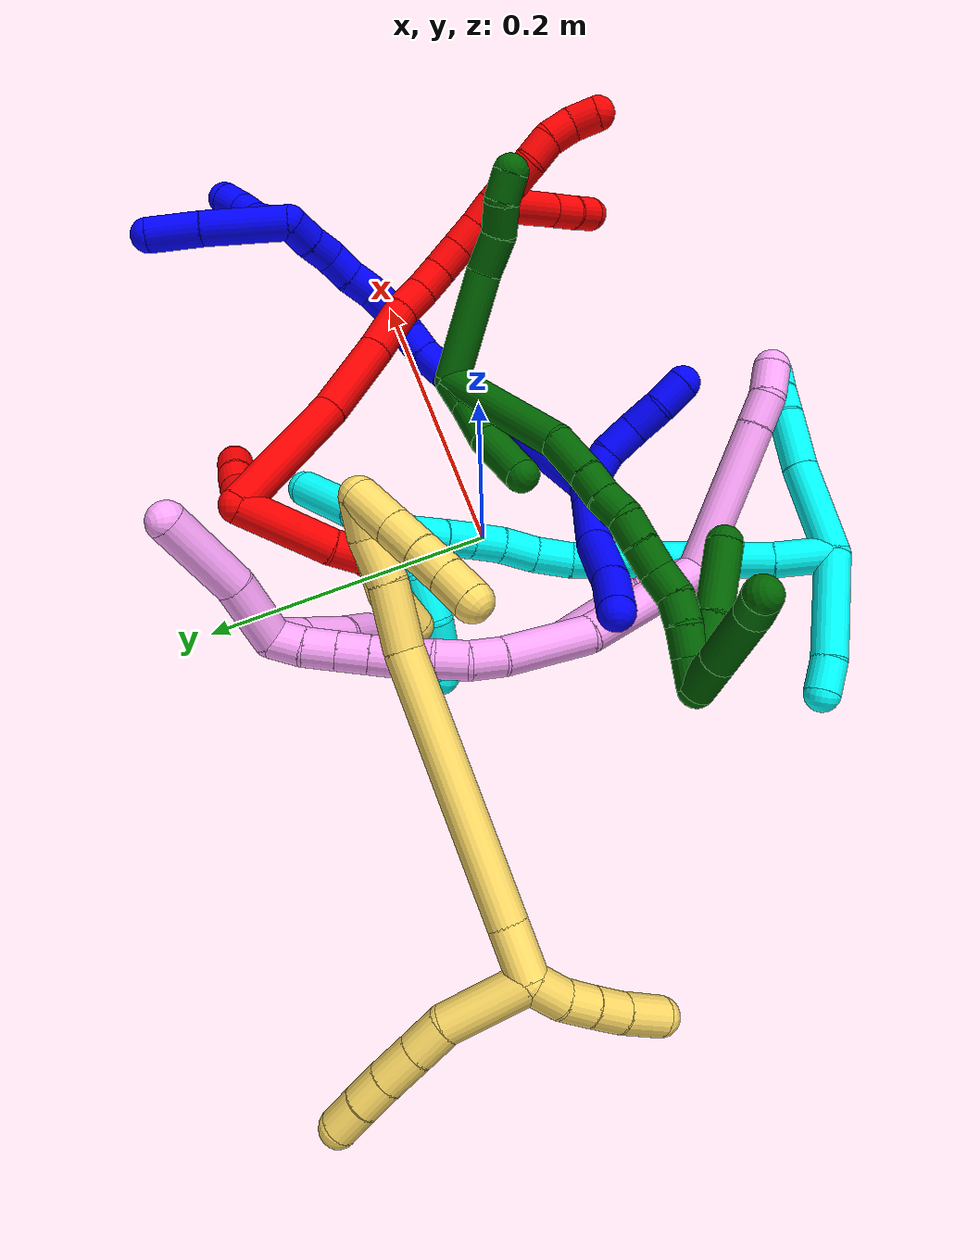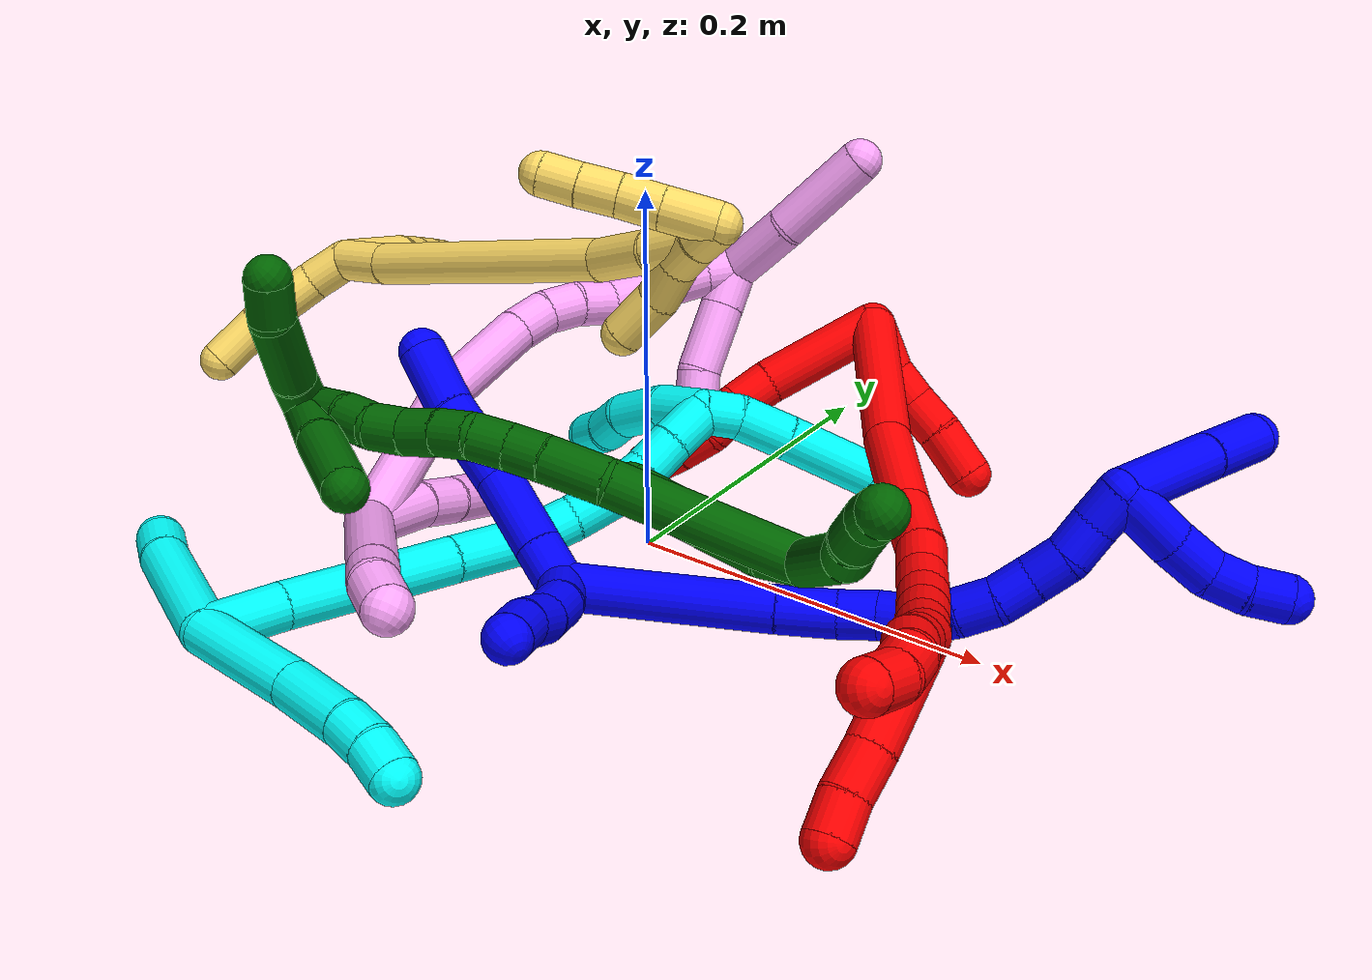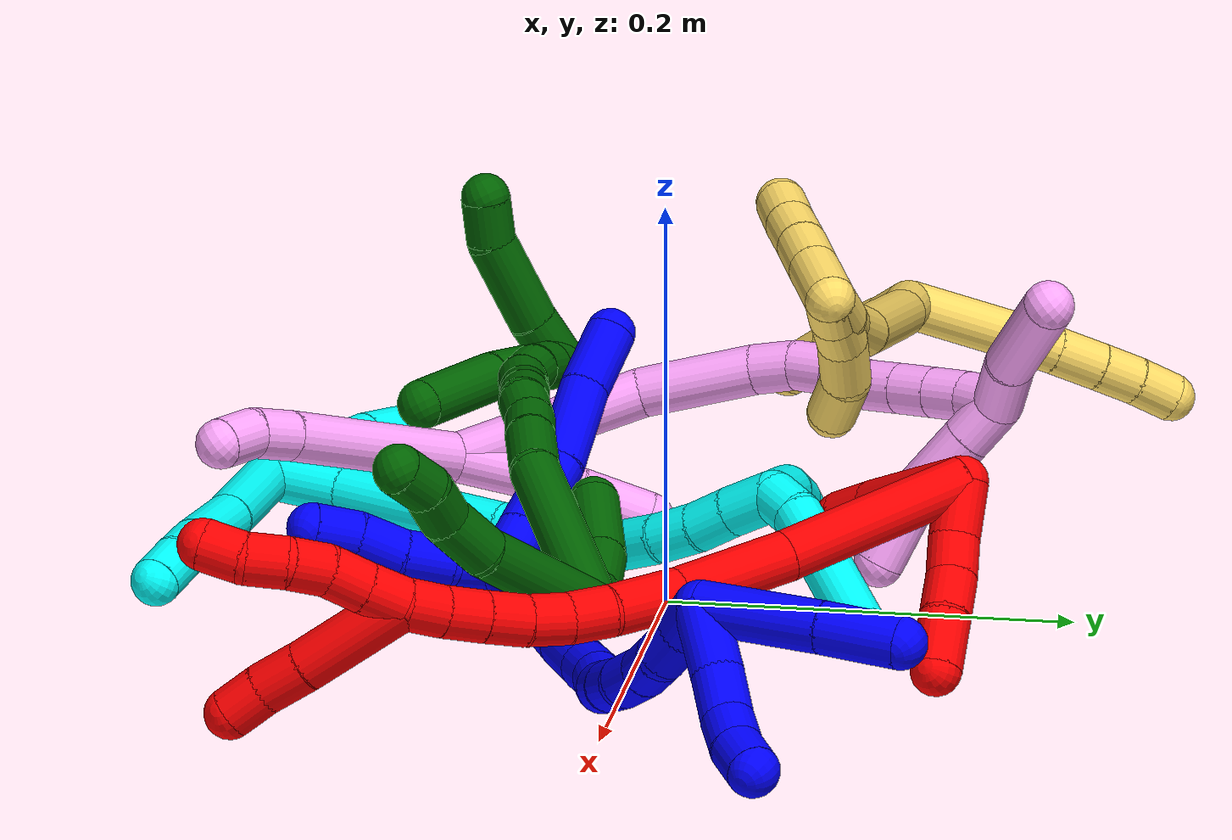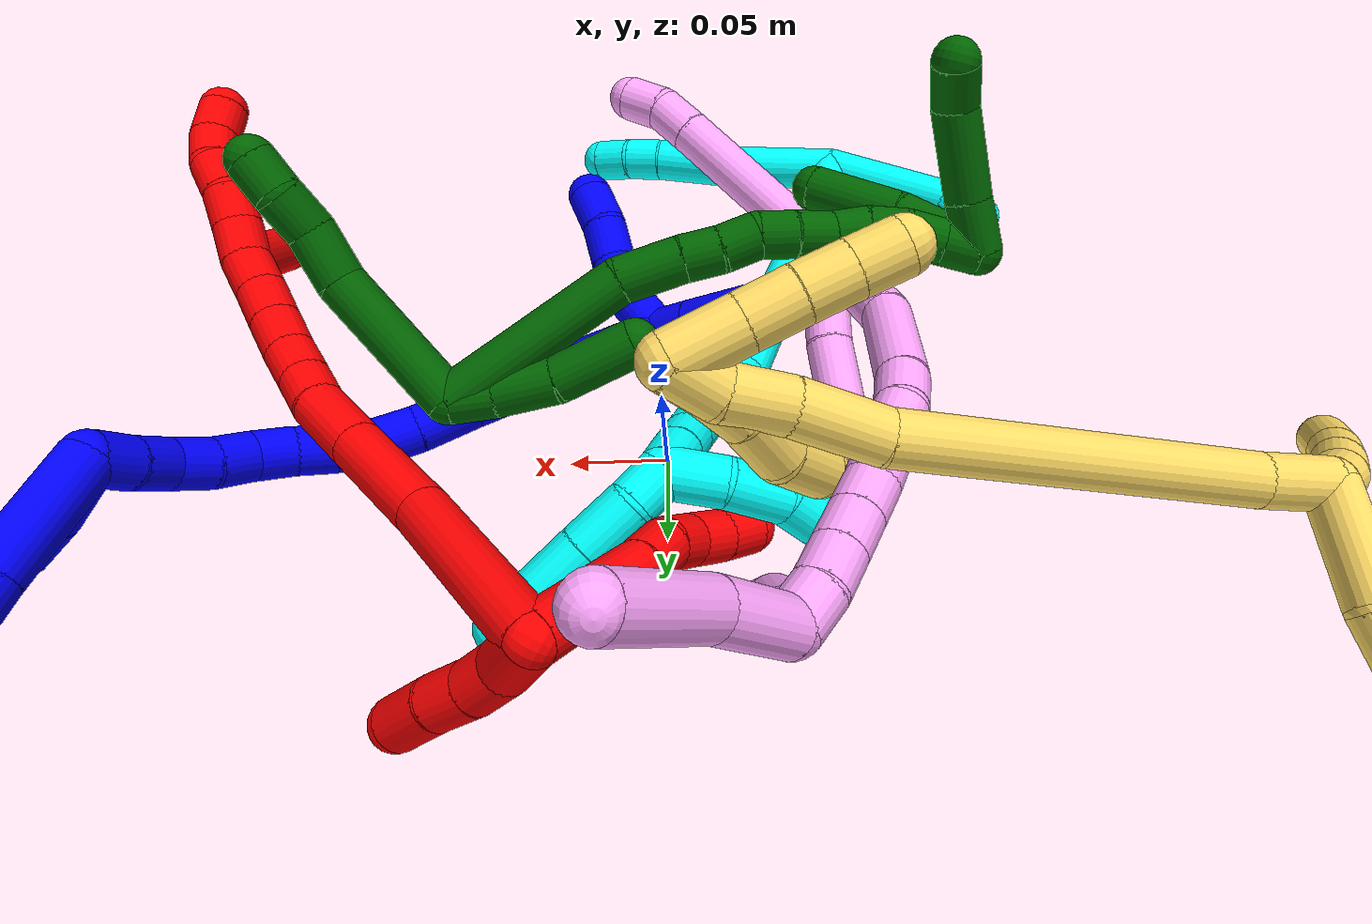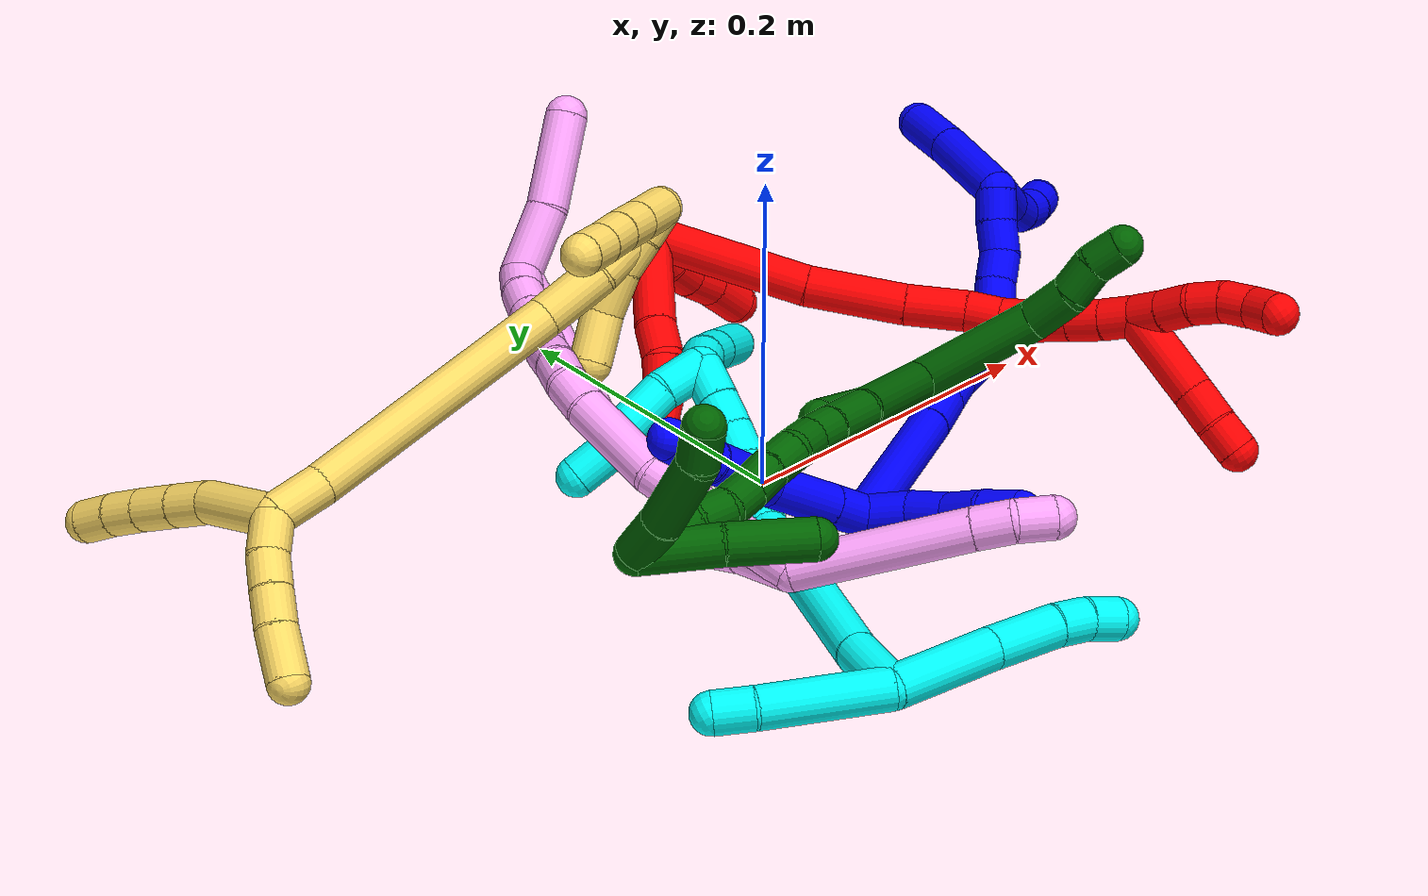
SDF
<sdf version="1.7">
 <world name="default">
  <plugin name="TubeGeneratorPlugin" filename="libtube_generator_plugin.so"/>
  <model name="photoneo_s_sensor">
   <static>1</static>
   <pose>0 0 2 1.57079 1.57079 3.14159</pose>
   <link name="link">
    <inertial><mass>0.1</mass></inertial>
    <sensor name="sensor" type="depth">
     <update_rate>30</update_rate>
     <camera>
      <horizontal_fov>1.22</horizontal_fov>
      <image><width>1920</width><height>1200</height><format>B8G8R8</format></image>
      <clip><near>0.1</near><far>4</far></clip>
      <depth_camera><output>points</output></depth_camera>
     </camera>
     <plugin name="camera_plugin" filename="libgazebo_ros_depth_camera.so">
      <baseline>0.2</baseline>
      <alwaysOn>1</alwaysOn>
      <updateRate>0.0</updateRate>
      <cameraName>camera_ir</cameraName>
      <imageTopicName>/camera/color/image_raw</imageTopicName>
      <cameraInfoTopicName>/camera/color/camera_info</cameraInfoTopicName>
      <depthImageTopicName>/camera/depth/image_raw</depthImageTopicName>
      <depthImageCameraInfoTopicName>/camera/depth/camera_info</depthImageCameraInfoTopicName>
      <pointCloudTopicName>/camera/depth/points</pointCloudTopicName>
      <frameName>fr_optical</frameName>
      <pointCloudCutoff>0.1</pointCloudCutoff>
      <pointCloudCutoffMax>2.0</pointCloudCutoffMax>
      <distortionK1>0</distortionK1>
      <distortionK2>0</distortionK2>
      <distortionK3>0</distortionK3>
      <distortionT1>0</distortionT1>
      <distortionT2>0</distortionT2>
      <CxPrime>0</CxPrime>
      <Cx>0</Cx>
      <Cy>0</Cy>
      <focalLength>0</focalLength>
      <hackBaseline>0</hackBaseline>
     </plugin>
    </sensor>
   </link>
  </model>
  <gravity>0 0 -9.8</gravity>
  <magnetic_field>6e-06 2.3e-05 -4.2e-05</magnetic_field>
  <atmosphere type="adiabatic"/>
  <physics name="default_physics" default="0" type="ode">
   <max_step_size>0.003</max_step_size>
   <real_time_factor>1</real_time_factor>
   <real_time_update_rate>1000</real_time_update_rate>
   <max_contacts>10000</max_contacts>
   <ode>
    <solver>
     <type>quick</type>
     <iters>100</iters>
     <sor>1.3</sor>
     <use_dynamic_moi_rescaling>0</use_dynamic_moi_rescaling>
    </solver>
    <constraints>
     <contact_max_correcting_vel>0</contact_max_correcting_vel>
     <contact_surface_layer>0.001</contact_surface_layer>
     <cfm>0</cfm>
     <erp>0.2</erp>
    </constraints>
   </ode>
  </physics>
  <scene><ambient>0.4 0.4 0.4 1</ambient><background>0.7 0.7 0.7 1</background><shadows>0</shadows></scene>
  <audio><device>default</device></audio>
  <spherical_coordinates>
   <surface_model>EARTH_WGS84</surface_model>
   <latitude_deg>0</latitude_deg>
   <longitude_deg>0</longitude_deg>
   <elevation>0</elevation>
   <heading_deg>0</heading_deg>
  </spherical_coordinates>
  <model name="bin">
   <static>1</static>
   <link name="bottom">
    <collision name="collision-bottom">
     <pose>0 0 -0.01 0 -0 0</pose>
     <geometry><box><size>0.8 0.6 0.02</size></box></geometry>
     <surface>
      <friction><ode><mu>100</mu><mu2>100</mu2></ode></friction>
      <contact><collide_bitmask>65535</collide_bitmask></contact>
     </surface>
    </collision>
   </link>
   <link name="west_wall">
    <collision name="collision-west_wall">
     <pose>-0.41 0 0.1 0 -0 0</pose>
     <geometry><box><size>0.02 0.6 0.2</size></box></geometry>
     <surface>
      <friction><ode><mu>100</mu><mu2>100</mu2></ode></friction>
      <contact><collide_bitmask>65535</collide_bitmask></contact>
     </surface>
    </collision>
   </link>
   <link name="east_wall">
    <collision name="collision-east_wall">
     <pose>0.41 0 0.1 0 -0 0</pose>
     <geometry><box><size>0.02 0.6 0.2</size></box></geometry>
     <surface>
      <friction><ode><mu>100</mu><mu2>100</mu2></ode></friction>
      <contact><collide_bitmask>65535</collide_bitmask></contact>
     </surface>
    </collision>
   </link>
   <link name="south_wall">
    <collision name="collision-south_wall">
     <pose>0 -0.31 0.1 0 -0 0</pose>
     <geometry><box><size>0.8 0.02 0.2</size></box></geometry>
     <surface>
      <friction><ode><mu>100</mu><mu2>100</mu2></ode></friction>
      <contact><collide_bitmask>65535</collide_bitmask></contact>
     </surface>
    </collision>
   </link>
   <link name="north_wall">
    <collision name="collision-north_wall">
     <pose>0 0.31 0.1 0 -0 0</pose>
     <geometry><box><size>0.8 0.02 0.2</size></box></geometry>
     <surface>
      <friction><ode><mu>100</mu><mu2>100</mu2></ode></friction>
      <contact><collide_bitmask>65535</collide_bitmask></contact>
     </surface>
    </collision>
   </link>
  </model>
  <model name="1">
   <static>0</static>
   <link name="1">
    <collision name="collision-cylinder-e_1_2_8">
     <pose>0.002393 -0.002239 0.012039 0.183877 0.192963 0.017846</pose>
     <geometry><cylinder><radius>0.0125</radius><length>0.024954</length></cylinder></geometry>
     <surface>
      <friction><ode><mu>1.16</mu><mu2>1.16</mu2><slip1>0</slip1><slip2>0</slip2></ode></friction>
      <contact><ode><kp>1e+06</kp><kd>1</kd><max_vel>0</max_vel><min_depth>0.001</min_depth></ode></contact>
     </surface>
    </collision>
    <visual name="visual-cylinder-e_1_2_8">
     <pose>0.002393 -0.002239 0.012039 0.183877 0.192963 0.017846</pose>
     <geometry><cylinder><radius>0.0125</radius><length>0.024954</length></cylinder></geometry>
     <material><ambient>0 0 1 1</ambient></material>
    </visual>
    <collision name="collision-cylinder-e_2_8_9">
     <pose>0.008993 -0.008092 0.045346 0.168337 0.192609 0.0163</pose>
     <geometry><cylinder><radius>0.0125</radius><length>0.043958</length></cylinder></geometry>
     <surface>
      <friction><ode><mu>1.16</mu><mu2>1.16</mu2><slip1>0</slip1><slip2>0</slip2></ode></friction>
      <contact><ode><kp>1e+06</kp><kd>1</kd><max_vel>0</max_vel><min_depth>0.001</min_depth></ode></contact>
     </surface>
    </collision>
    <visual name="visual-cylinder-e_2_8_9">
     <pose>0.008993 -0.008092 0.045346 0.168337 0.192609 0.0163</pose>
     <geometry><cylinder><radius>0.0125</radius><length>0.043958</length></cylinder></geometry>
     <material><ambient>0 0 1 1</ambient></material>
    </visual>
    <collision name="collision-cylinder-e_3_9_10">
     <pose>0.018222 -0.019362 0.087768 0.347217 0.21964 0.03867</pose>
     <geometry><cylinder><radius>0.0125</radius><length>0.046103</length></cylinder></geometry>
     <surface>
      <friction><ode><mu>1.16</mu><mu2>1.16</mu2><slip1>0</slip1><slip2>0</slip2></ode></friction>
      <contact><ode><kp>1e+06</kp><kd>1</kd><max_vel>0</max_vel><min_depth>0.001</min_depth></ode></contact>
     </surface>
    </collision>
    <visual name="visual-cylinder-e_3_9_10">
     <pose>0.018222 -0.019362 0.087768 0.347217 0.21964 0.03867</pose>
     <geometry><cylinder><radius>0.0125</radius><length>0.046103</length></cylinder></geometry>
     <material><ambient>0 0 1 1</ambient></material>
    </visual>
    <collision name="collision-cylinder-e_4_10_6">
     <pose>0.028421 -0.031039 0.125141 0.243076 0.300428 0.036969</pose>
     <geometry><cylinder><radius>0.0125</radius><length>0.034985</length></cylinder></geometry>
     <surface>
      <friction><ode><mu>1.16</mu><mu2>1.16</mu2><slip1>0</slip1><slip2>0</slip2></ode></friction>
      <contact><ode><kp>1e+06</kp><kd>1</kd><max_vel>0</max_vel><min_depth>0.001</min_depth></ode></contact>
     </surface>
    </collision>
    <visual name="visual-cylinder-e_4_10_6">
     <pose>0.028421 -0.031039 0.125141 0.243076 0.300428 0.036969</pose>
     <geometry><cylinder><radius>0.0125</radius><length>0.034985</length></cylinder></geometry>
     <material><ambient>0 0 1 1</ambient></material>
    </visual>
    <collision name="collision-cylinder-e_1_2_11">
     <pose>0.001552 -0.009533 -0.010181 2.38904 0.110821 0.278952</pose>
     <geometry><cylinder><radius>0.0125</radius><length>0.028067</length></cylinder></geometry>
     <surface>
      <friction><ode><mu>1.16</mu><mu2>1.16</mu2><slip1>0</slip1><slip2>0</slip2></ode></friction>
      <contact><ode><kp>1e+06</kp><kd>1</kd><max_vel>0</max_vel><min_depth>0.001</min_depth></ode></contact>
     </surface>
    </collision>
    <visual name="visual-cylinder-e_1_2_11">
     <pose>0.001552 -0.009533 -0.010181 2.38904 0.110821 0.278952</pose>
     <geometry><cylinder><radius>0.0125</radius><length>0.028067</length></cylinder></geometry>
     <material><ambient>0 0 1 1</ambient></material>
    </visual>
    <collision name="collision-cylinder-e_2_11_12">
     <pose>0.002665 -0.029394 -0.027194 2.15525 -0.035434 -0.065911</pose>
     <geometry><cylinder><radius>0.0125</radius><length>0.024782</length></cylinder></geometry>
     <surface>
      <friction><ode><mu>1.16</mu><mu2>1.16</mu2><slip1>0</slip1><slip2>0</slip2></ode></friction>
      <contact><ode><kp>1e+06</kp><kd>1</kd><max_vel>0</max_vel><min_depth>0.001</min_depth></ode></contact>
     </surface>
    </collision>
    <visual name="visual-cylinder-e_2_11_12">
     <pose>0.002665 -0.029394 -0.027194 2.15525 -0.035434 -0.065911</pose>
     <geometry><cylinder><radius>0.0125</radius><length>0.024782</length></cylinder></geometry>
     <material><ambient>0 0 1 1</ambient></material>
    </visual>
    <collision name="collision-cylinder-e_3_12_13">
     <pose>0.003148 -0.050674 -0.038799 1.98173 0.077041 0.11753</pose>
     <geometry><cylinder><radius>0.0125</radius><length>0.023964</length></cylinder></geometry>
     <surface>
      <friction><ode><mu>1.16</mu><mu2>1.16</mu2><slip1>0</slip1><slip2>0</slip2></ode></friction>
      <contact><ode><kp>1e+06</kp><kd>1</kd><max_vel>0</max_vel><min_depth>0.001</min_depth></ode></contact>
     </surface>
    </collision>
    <visual name="visual-cylinder-e_3_12_13">
     <pose>0.003148 -0.050674 -0.038799 1.98173 0.077041 0.11753</pose>
     <geometry><cylinder><radius>0.0125</radius><length>0.023964</length></cylinder></geometry>
     <material><ambient>0 0 1 1</ambient></material>
    </visual>
    <collision name="collision-cylinder-e_4_13_5">
     <pose>0.004073 -0.071176 -0.050144 2.1736 0.000196 0.000372</pose>
     <geometry><cylinder><radius>0.0125</radius><length>0.023187</length></cylinder></geometry>
     <surface>
      <friction><ode><mu>1.16</mu><mu2>1.16</mu2><slip1>0</slip1><slip2>0</slip2></ode></friction>
      <contact><ode><kp>1e+06</kp><kd>1</kd><max_vel>0</max_vel><min_depth>0.001</min_depth></ode></contact>
     </surface>
    </collision>
    <visual name="visual-cylinder-e_4_13_5">
     <pose>0.004073 -0.071176 -0.050144 2.1736 0.000196 0.000372</pose>
     <geometry><cylinder><radius>0.0125</radius><length>0.023187</length></cylinder></geometry>
     <material><ambient>0 0 1 1</ambient></material>
    </visual>
    <collision name="collision-cylinder-e_1_2_14">
     <pose>0.028962 0.029206 -0.035216 -2.44923 0.564358 -1.35403</pose>
     <geometry><cylinder><radius>0.0125</radius><length>0.108295</length></cylinder></geometry>
     <surface>
      <friction><ode><mu>1.16</mu><mu2>1.16</mu2><slip1>0</slip1><slip2>0</slip2></ode></friction>
      <contact><ode><kp>1e+06</kp><kd>1</kd><max_vel>0</max_vel><min_depth>0.001</min_depth></ode></contact>
     </surface>
    </collision>
    <visual name="visual-cylinder-e_1_2_14">
     <pose>0.028962 0.029206 -0.035216 -2.44923 0.564358 -1.35403</pose>
     <geometry><cylinder><radius>0.0125</radius><length>0.108295</length></cylinder></geometry>
     <material><ambient>0 0 1 1</ambient></material>
    </visual>
    <collision name="collision-cylinder-e_2_14_15">
     <pose>0.066271 0.067177 -0.079889 -2.39405 0.574489 -1.2911</pose>
     <geometry><cylinder><radius>0.0125</radius><length>0.03072</length></cylinder></geometry>
     <surface>
      <friction><ode><mu>1.16</mu><mu2>1.16</mu2><slip1>0</slip1><slip2>0</slip2></ode></friction>
      <contact><ode><kp>1e+06</kp><kd>1</kd><max_vel>0</max_vel><min_depth>0.001</min_depth></ode></contact>
     </surface>
    </collision>
    <visual name="visual-cylinder-e_2_14_15">
     <pose>0.066271 0.067177 -0.079889 -2.39405 0.574489 -1.2911</pose>
     <geometry><cylinder><radius>0.0125</radius><length>0.03072</length></cylinder></geometry>
     <material><ambient>0 0 1 1</ambient></material>
    </visual>
    <collision name="collision-cylinder-e_3_15_16">
     <pose>0.080979 0.080981 -0.095769 -2.47662 0.661911 -1.56583</pose>
     <geometry><cylinder><radius>0.0125</radius><length>0.020699</length></cylinder></geometry>
     <surface>
      <friction><ode><mu>1.16</mu><mu2>1.16</mu2><slip1>0</slip1><slip2>0</slip2></ode></friction>
      <contact><ode><kp>1e+06</kp><kd>1</kd><max_vel>0</max_vel><min_depth>0.001</min_depth></ode></contact>
     </surface>
    </collision>
    <visual name="visual-cylinder-e_3_15_16">
     <pose>0.080979 0.080981 -0.095769 -2.47662 0.661911 -1.56583</pose>
     <geometry><cylinder><radius>0.0125</radius><length>0.020699</length></cylinder></geometry>
     <material><ambient>0 0 1 1</ambient></material>
    </visual>
    <collision name="collision-cylinder-e_4_16_17">
     <pose>0.093168 0.089349 -0.109672 -2.72264 0.618725 -1.9677</pose>
     <geometry><cylinder><radius>0.0125</radius><length>0.020099</length></cylinder></geometry>
     <surface>
      <friction><ode><mu>1.16</mu><mu2>1.16</mu2><slip1>0</slip1><slip2>0</slip2></ode></friction>
      <contact><ode><kp>1e+06</kp><kd>1</kd><max_vel>0</max_vel><min_depth>0.001</min_depth></ode></contact>
     </surface>
    </collision>
    <visual name="visual-cylinder-e_4_16_17">
     <pose>0.093168 0.089349 -0.109672 -2.72264 0.618725 -1.9677</pose>
     <geometry><cylinder><radius>0.0125</radius><length>0.020099</length></cylinder></geometry>
     <material><ambient>0 0 1 1</ambient></material>
    </visual>
    <collision name="collision-cylinder-e_5_17_18">
     <pose>0.106926 0.095116 -0.12277 -2.73233 0.913033 -2.34195</pose>
     <geometry><cylinder><radius>0.0125</radius><length>0.02004</length></cylinder></geometry>
     <surface>
      <friction><ode><mu>1.16</mu><mu2>1.16</mu2><slip1>0</slip1><slip2>0</slip2></ode></friction>
      <contact><ode><kp>1e+06</kp><kd>1</kd><max_vel>0</max_vel><min_depth>0.001</min_depth></ode></contact>
     </surface>
    </collision>
    <visual name="visual-cylinder-e_5_17_18">
     <pose>0.106926 0.095116 -0.12277 -2.73233 0.913033 -2.34195</pose>
     <geometry><cylinder><radius>0.0125</radius><length>0.02004</length></cylinder></geometry>
     <material><ambient>0 0 1 1</ambient></material>
    </visual>
    <collision name="collision-cylinder-e_6_18_19">
     <pose>0.12331 0.100727 -0.132803 -2.51832 0.999457 -2.07546</pose>
     <geometry><cylinder><radius>0.0125</radius><length>0.020102</length></cylinder></geometry>
     <surface>
      <friction><ode><mu>1.16</mu><mu2>1.16</mu2><slip1>0</slip1><slip2>0</slip2></ode></friction>
      <contact><ode><kp>1e+06</kp><kd>1</kd><max_vel>0</max_vel><min_depth>0.001</min_depth></ode></contact>
     </surface>
    </collision>
    <visual name="visual-cylinder-e_6_18_19">
     <pose>0.12331 0.100727 -0.132803 -2.51832 0.999457 -2.07546</pose>
     <geometry><cylinder><radius>0.0125</radius><length>0.020102</length></cylinder></geometry>
     <material><ambient>0 0 1 1</ambient></material>
    </visual>
    <collision name="collision-cylinder-e_7_19_20">
     <pose>0.141004 0.107376 -0.1389 -2.02176 1.17477 -1.63104</pose>
     <geometry><cylinder><radius>0.0125</radius><length>0.020028</length></cylinder></geometry>
     <surface>
      <friction><ode><mu>1.16</mu><mu2>1.16</mu2><slip1>0</slip1><slip2>0</slip2></ode></friction>
      <contact><ode><kp>1e+06</kp><kd>1</kd><max_vel>0</max_vel><min_depth>0.001</min_depth></ode></contact>
     </surface>
    </collision>
    <visual name="visual-cylinder-e_7_19_20">
     <pose>0.141004 0.107376 -0.1389 -2.02176 1.17477 -1.63104</pose>
     <geometry><cylinder><radius>0.0125</radius><length>0.020028</length></cylinder></geometry>
     <material><ambient>0 0 1 1</ambient></material>
    </visual>
    <collision name="collision-cylinder-e_8_20_21">
     <pose>0.15979 0.112821 -0.142852 -2.42686 1.266 -2.20008</pose>
     <geometry><cylinder><radius>0.0125</radius><length>0.020017</length></cylinder></geometry>
     <surface>
      <friction><ode><mu>1.16</mu><mu2>1.16</mu2><slip1>0</slip1><slip2>0</slip2></ode></friction>
      <contact><ode><kp>1e+06</kp><kd>1</kd><max_vel>0</max_vel><min_depth>0.001</min_depth></ode></contact>
     </surface>
    </collision>
    <visual name="visual-cylinder-e_8_20_21">
     <pose>0.15979 0.112821 -0.142852 -2.42686 1.266 -2.20008</pose>
     <geometry><cylinder><radius>0.0125</radius><length>0.020017</length></cylinder></geometry>
     <material><ambient>0 0 1 1</ambient></material>
    </visual>
    <collision name="collision-cylinder-e_9_21_22">
     <pose>0.179177 0.11631 -0.144185 -1.01926 1.39135 -0.873174</pose>
     <geometry><cylinder><radius>0.0125</radius><length>0.02</length></cylinder></geometry>
     <surface>
      <friction><ode><mu>1.16</mu><mu2>1.16</mu2><slip1>0</slip1><slip2>0</slip2></ode></friction>
      <contact><ode><kp>1e+06</kp><kd>1</kd><max_vel>0</max_vel><min_depth>0.001</min_depth></ode></contact>
     </surface>
    </collision>
    <visual name="visual-cylinder-e_9_21_22">
     <pose>0.179177 0.11631 -0.144185 -1.01926 1.39135 -0.873174</pose>
     <geometry><cylinder><radius>0.0125</radius><length>0.02</length></cylinder></geometry>
     <material><ambient>0 0 1 1</ambient></material>
    </visual>
    <collision name="collision-cylinder-e_10_22_1">
     <pose>0.198996 0.118434 -0.143022 -1.20898 1.50619 -1.14924</pose>
     <geometry><cylinder><radius>0.0125</radius><length>0.02</length></cylinder></geometry>
     <surface>
      <friction><ode><mu>1.16</mu><mu2>1.16</mu2><slip1>0</slip1><slip2>0</slip2></ode></friction>
      <contact><ode><kp>1e+06</kp><kd>1</kd><max_vel>0</max_vel><min_depth>0.001</min_depth></ode></contact>
     </surface>
    </collision>
    <visual name="visual-cylinder-e_10_22_1">
     <pose>0.198996 0.118434 -0.143022 -1.20898 1.50619 -1.14924</pose>
     <geometry><cylinder><radius>0.0125</radius><length>0.02</length></cylinder></geometry>
     <material><ambient>0 0 1 1</ambient></material>
    </visual>
    <collision name="collision-cylinder-e_1_1_23">
     <pose>0.206218 0.132118 -0.154312 -2.2928 -0.156874 0.344444</pose>
     <geometry><cylinder><radius>0.0125</radius><length>0.035291</length></cylinder></geometry>
     <surface>
      <friction><ode><mu>1.16</mu><mu2>1.16</mu2><slip1>0</slip1><slip2>0</slip2></ode></friction>
      <contact><ode><kp>1e+06</kp><kd>1</kd><max_vel>0</max_vel><min_depth>0.001</min_depth></ode></contact>
     </surface>
    </collision>
    <visual name="visual-cylinder-e_1_1_23">
     <pose>0.206218 0.132118 -0.154312 -2.2928 -0.156874 0.344444</pose>
     <geometry><cylinder><radius>0.0125</radius><length>0.035291</length></cylinder></geometry>
     <material><ambient>0 0 1 1</ambient></material>
    </visual>
    <collision name="collision-cylinder-e_2_23_24">
     <pose>0.20258 0.153708 -0.174658 -2.37451 -0.071714 0.177328</pose>
     <geometry><cylinder><radius>0.0125</radius><length>0.024587</length></cylinder></geometry>
     <surface>
      <friction><ode><mu>1.16</mu><mu2>1.16</mu2><slip1>0</slip1><slip2>0</slip2></ode></friction>
      <contact><ode><kp>1e+06</kp><kd>1</kd><max_vel>0</max_vel><min_depth>0.001</min_depth></ode></contact>
     </surface>
    </collision>
    <visual name="visual-cylinder-e_2_23_24">
     <pose>0.20258 0.153708 -0.174658 -2.37451 -0.071714 0.177328</pose>
     <geometry><cylinder><radius>0.0125</radius><length>0.024587</length></cylinder></geometry>
     <material><ambient>0 0 1 1</ambient></material>
    </visual>
    <collision name="collision-cylinder-e_3_24_25">
     <pose>0.204075 0.168326 -0.191043 -2.46186 0.239844 -0.656901</pose>
     <geometry><cylinder><radius>0.0125</radius><length>0.020005</length></cylinder></geometry>
     <surface>
      <friction><ode><mu>1.16</mu><mu2>1.16</mu2><slip1>0</slip1><slip2>0</slip2></ode></friction>
      <contact><ode><kp>1e+06</kp><kd>1</kd><max_vel>0</max_vel><min_depth>0.001</min_depth></ode></contact>
     </surface>
    </collision>
    <visual name="visual-cylinder-e_3_24_25">
     <pose>0.204075 0.168326 -0.191043 -2.46186 0.239844 -0.656901</pose>
     <geometry><cylinder><radius>0.0125</radius><length>0.020005</length></cylinder></geometry>
     <material><ambient>0 0 1 1</ambient></material>
    </visual>
    <collision name="collision-cylinder-e_4_25_4">
     <pose>0.210403 0.181124 -0.204986 -2.333 0.403716 -0.892266</pose>
     <geometry><cylinder><radius>0.0125</radius><length>0.020117</length></cylinder></geometry>
     <surface>
      <friction><ode><mu>1.16</mu><mu2>1.16</mu2><slip1>0</slip1><slip2>0</slip2></ode></friction>
      <contact><ode><kp>1e+06</kp><kd>1</kd><max_vel>0</max_vel><min_depth>0.001</min_depth></ode></contact>
     </surface>
    </collision>
    <visual name="visual-cylinder-e_4_25_4">
     <pose>0.210403 0.181124 -0.204986 -2.333 0.403716 -0.892266</pose>
     <geometry><cylinder><radius>0.0125</radius><length>0.020117</length></cylinder></geometry>
     <material><ambient>0 0 1 1</ambient></material>
    </visual>
    <collision name="collision-cylinder-e_1_1_26">
     <pose>0.22437 0.145581 -0.140236 -1.47477 0.523578 -0.477457</pose>
     <geometry><cylinder><radius>0.0125</radius><length>0.061582</length></cylinder></geometry>
     <surface>
      <friction><ode><mu>1.16</mu><mu2>1.16</mu2><slip1>0</slip1><slip2>0</slip2></ode></friction>
      <contact><ode><kp>1e+06</kp><kd>1</kd><max_vel>0</max_vel><min_depth>0.001</min_depth></ode></contact>
     </surface>
    </collision>
    <visual name="visual-cylinder-e_1_1_26">
     <pose>0.22437 0.145581 -0.140236 -1.47477 0.523578 -0.477457</pose>
     <geometry><cylinder><radius>0.0125</radius><length>0.061582</length></cylinder></geometry>
     <material><ambient>0 0 1 1</ambient></material>
    </visual>
    <collision name="collision-cylinder-e_2_26_3">
     <pose>0.248575 0.189081 -0.135724 -1.45598 0.476473 -0.426327</pose>
     <geometry><cylinder><radius>0.0125</radius><length>0.038418</length></cylinder></geometry>
     <surface>
      <friction><ode><mu>1.16</mu><mu2>1.16</mu2><slip1>0</slip1><slip2>0</slip2></ode></friction>
      <contact><ode><kp>1e+06</kp><kd>1</kd><max_vel>0</max_vel><min_depth>0.001</min_depth></ode></contact>
     </surface>
    </collision>
    <visual name="visual-cylinder-e_2_26_3">
     <pose>0.248575 0.189081 -0.135724 -1.45598 0.476473 -0.426327</pose>
     <geometry><cylinder><radius>0.0125</radius><length>0.038418</length></cylinder></geometry>
     <material><ambient>0 0 1 1</ambient></material>
    </visual>
    <collision name="collision-sphere-3">
     <pose>0.257385 0.206038 -0.133769 0 -0 0</pose>
     <geometry><sphere><radius>0.0125</radius></sphere></geometry>
     <surface>
      <friction><ode><mu>1.16</mu><mu2>1.16</mu2><slip1>0</slip1><slip2>0</slip2></ode></friction>
      <contact><ode><kp>1e+06</kp><kd>1</kd><max_vel>0</max_vel><min_depth>0.001</min_depth></ode></contact>
     </surface>
    </collision>
    <visual name="visual-sphere-3">
     <pose>0.257385 0.206038 -0.133769 0 -0 0</pose>
     <geometry><sphere><radius>0.0125</radius></sphere></geometry>
     <material><ambient>0 0 1 1</ambient></material>
    </visual>
    <collision name="collision-sphere-26">
     <pose>0.239765 0.172125 -0.13768 0 -0 0</pose>
     <geometry><sphere><radius>0.0125</radius></sphere></geometry>
     <surface>
      <friction><ode><mu>1.16</mu><mu2>1.16</mu2><slip1>0</slip1><slip2>0</slip2></ode></friction>
      <contact><ode><kp>1e+06</kp><kd>1</kd><max_vel>0</max_vel><min_depth>0.001</min_depth></ode></contact>
     </surface>
    </collision>
    <visual name="visual-sphere-26">
     <pose>0.239765 0.172125 -0.13768 0 -0 0</pose>
     <geometry><sphere><radius>0.0125</radius></sphere></geometry>
     <material><ambient>0 0 1 1</ambient></material>
    </visual>
    <collision name="collision-sphere-4">
     <pose>0.214354 0.187814 -0.211374 0 -0 0</pose>
     <geometry><sphere><radius>0.0125</radius></sphere></geometry>
     <surface>
      <friction><ode><mu>1.16</mu><mu2>1.16</mu2><slip1>0</slip1><slip2>0</slip2></ode></friction>
      <contact><ode><kp>1e+06</kp><kd>1</kd><max_vel>0</max_vel><min_depth>0.001</min_depth></ode></contact>
     </surface>
    </collision>
    <visual name="visual-sphere-4">
     <pose>0.214354 0.187814 -0.211374 0 -0 0</pose>
     <geometry><sphere><radius>0.0125</radius></sphere></geometry>
     <material><ambient>0 0 1 1</ambient></material>
    </visual>
    <collision name="collision-sphere-25">
     <pose>0.206452 0.174433 -0.198599 0 -0 0</pose>
     <geometry><sphere><radius>0.0125</radius></sphere></geometry>
     <surface>
      <friction><ode><mu>1.16</mu><mu2>1.16</mu2><slip1>0</slip1><slip2>0</slip2></ode></friction>
      <contact><ode><kp>1e+06</kp><kd>1</kd><max_vel>0</max_vel><min_depth>0.001</min_depth></ode></contact>
     </surface>
    </collision>
    <visual name="visual-sphere-25">
     <pose>0.206452 0.174433 -0.198599 0 -0 0</pose>
     <geometry><sphere><radius>0.0125</radius></sphere></geometry>
     <material><ambient>0 0 1 1</ambient></material>
    </visual>
    <collision name="collision-sphere-24">
     <pose>0.201699 0.162219 -0.183486 0 -0 0</pose>
     <geometry><sphere><radius>0.0125</radius></sphere></geometry>
     <surface>
      <friction><ode><mu>1.16</mu><mu2>1.16</mu2><slip1>0</slip1><slip2>0</slip2></ode></friction>
      <contact><ode><kp>1e+06</kp><kd>1</kd><max_vel>0</max_vel><min_depth>0.001</min_depth></ode></contact>
     </surface>
    </collision>
    <visual name="visual-sphere-24">
     <pose>0.201699 0.162219 -0.183486 0 -0 0</pose>
     <geometry><sphere><radius>0.0125</radius></sphere></geometry>
     <material><ambient>0 0 1 1</ambient></material>
    </visual>
    <collision name="collision-sphere-23">
     <pose>0.203461 0.145198 -0.16583 0 -0 0</pose>
     <geometry><sphere><radius>0.0125</radius></sphere></geometry>
     <surface>
      <friction><ode><mu>1.16</mu><mu2>1.16</mu2><slip1>0</slip1><slip2>0</slip2></ode></friction>
      <contact><ode><kp>1e+06</kp><kd>1</kd><max_vel>0</max_vel><min_depth>0.001</min_depth></ode></contact>
     </surface>
    </collision>
    <visual name="visual-sphere-23">
     <pose>0.203461 0.145198 -0.16583 0 -0 0</pose>
     <geometry><sphere><radius>0.0125</radius></sphere></geometry>
     <material><ambient>0 0 1 1</ambient></material>
    </visual>
    <collision name="collision-sphere-1">
     <pose>0.208975 0.119038 -0.142793 0 -0 0</pose>
     <geometry><sphere><radius>0.0125</radius></sphere></geometry>
     <surface>
      <friction><ode><mu>1.16</mu><mu2>1.16</mu2><slip1>0</slip1><slip2>0</slip2></ode></friction>
      <contact><ode><kp>1e+06</kp><kd>1</kd><max_vel>0</max_vel><min_depth>0.001</min_depth></ode></contact>
     </surface>
    </collision>
    <visual name="visual-sphere-1">
     <pose>0.208975 0.119038 -0.142793 0 -0 0</pose>
     <geometry><sphere><radius>0.0125</radius></sphere></geometry>
     <material><ambient>0 0 1 1</ambient></material>
    </visual>
    <collision name="collision-sphere-22">
     <pose>0.189016 0.11783 -0.14325 0 -0 0</pose>
     <geometry><sphere><radius>0.0125</radius></sphere></geometry>
     <surface>
      <friction><ode><mu>1.16</mu><mu2>1.16</mu2><slip1>0</slip1><slip2>0</slip2></ode></friction>
      <contact><ode><kp>1e+06</kp><kd>1</kd><max_vel>0</max_vel><min_depth>0.001</min_depth></ode></contact>
     </surface>
    </collision>
    <visual name="visual-sphere-22">
     <pose>0.189016 0.11783 -0.14325 0 -0 0</pose>
     <geometry><sphere><radius>0.0125</radius></sphere></geometry>
     <material><ambient>0 0 1 1</ambient></material>
    </visual>
    <collision name="collision-sphere-21">
     <pose>0.169337 0.11479 -0.145121 0 -0 0</pose>
     <geometry><sphere><radius>0.0125</radius></sphere></geometry>
     <surface>
      <friction><ode><mu>1.16</mu><mu2>1.16</mu2><slip1>0</slip1><slip2>0</slip2></ode></friction>
      <contact><ode><kp>1e+06</kp><kd>1</kd><max_vel>0</max_vel><min_depth>0.001</min_depth></ode></contact>
     </surface>
    </collision>
    <visual name="visual-sphere-21">
     <pose>0.169337 0.11479 -0.145121 0 -0 0</pose>
     <geometry><sphere><radius>0.0125</radius></sphere></geometry>
     <material><ambient>0 0 1 1</ambient></material>
    </visual>
    <collision name="collision-sphere-11">
     <pose>0.003104 -0.019066 -0.020362 0 -0 0</pose>
     <geometry><sphere><radius>0.0125</radius></sphere></geometry>
     <surface>
      <friction><ode><mu>1.16</mu><mu2>1.16</mu2><slip1>0</slip1><slip2>0</slip2></ode></friction>
      <contact><ode><kp>1e+06</kp><kd>1</kd><max_vel>0</max_vel><min_depth>0.001</min_depth></ode></contact>
     </surface>
    </collision>
    <visual name="visual-sphere-11">
     <pose>0.003104 -0.019066 -0.020362 0 -0 0</pose>
     <geometry><sphere><radius>0.0125</radius></sphere></geometry>
     <material><ambient>0 0 1 1</ambient></material>
    </visual>
    <collision name="collision-sphere-6">
     <pose>0.033598 -0.035061 0.141359 0 -0 0</pose>
     <geometry><sphere><radius>0.0125</radius></sphere></geometry>
     <surface>
      <friction><ode><mu>1.16</mu><mu2>1.16</mu2><slip1>0</slip1><slip2>0</slip2></ode></friction>
      <contact><ode><kp>1e+06</kp><kd>1</kd><max_vel>0</max_vel><min_depth>0.001</min_depth></ode></contact>
     </surface>
    </collision>
    <visual name="visual-sphere-6">
     <pose>0.033598 -0.035061 0.141359 0 -0 0</pose>
     <geometry><sphere><radius>0.0125</radius></sphere></geometry>
     <material><ambient>0 0 1 1</ambient></material>
    </visual>
    <collision name="collision-sphere-10">
     <pose>0.023245 -0.027018 0.108923 0 -0 0</pose>
     <geometry><sphere><radius>0.0125</radius></sphere></geometry>
     <surface>
      <friction><ode><mu>1.16</mu><mu2>1.16</mu2><slip1>0</slip1><slip2>0</slip2></ode></friction>
      <contact><ode><kp>1e+06</kp><kd>1</kd><max_vel>0</max_vel><min_depth>0.001</min_depth></ode></contact>
     </surface>
    </collision>
    <visual name="visual-sphere-10">
     <pose>0.023245 -0.027018 0.108923 0 -0 0</pose>
     <geometry><sphere><radius>0.0125</radius></sphere></geometry>
     <material><ambient>0 0 1 1</ambient></material>
    </visual>
    <collision name="collision-sphere-9">
     <pose>0.0132 -0.011707 0.066613 0 -0 0</pose>
     <geometry><sphere><radius>0.0125</radius></sphere></geometry>
     <surface>
      <friction><ode><mu>1.16</mu><mu2>1.16</mu2><slip1>0</slip1><slip2>0</slip2></ode></friction>
      <contact><ode><kp>1e+06</kp><kd>1</kd><max_vel>0</max_vel><min_depth>0.001</min_depth></ode></contact>
     </surface>
    </collision>
    <visual name="visual-sphere-9">
     <pose>0.0132 -0.011707 0.066613 0 -0 0</pose>
     <geometry><sphere><radius>0.0125</radius></sphere></geometry>
     <material><ambient>0 0 1 1</ambient></material>
    </visual>
    <collision name="collision-sphere-2">
     <geometry><sphere><radius>0.0125</radius></sphere></geometry>
     <surface>
      <friction><ode><mu>1.16</mu><mu2>1.16</mu2><slip1>0</slip1><slip2>0</slip2></ode></friction>
      <contact><ode><kp>1e+06</kp><kd>1</kd><max_vel>0</max_vel><min_depth>0.001</min_depth></ode></contact>
     </surface>
    </collision>
    <visual name="visual-sphere-2">
     <geometry><sphere><radius>0.0125</radius></sphere></geometry>
     <material><ambient>0 0 1 1</ambient></material>
    </visual>
    <collision name="collision-sphere-19">
     <pose>0.131765 0.103899 -0.137216 0 -0 0</pose>
     <geometry><sphere><radius>0.0125</radius></sphere></geometry>
     <surface>
      <friction><ode><mu>1.16</mu><mu2>1.16</mu2><slip1>0</slip1><slip2>0</slip2></ode></friction>
      <contact><ode><kp>1e+06</kp><kd>1</kd><max_vel>0</max_vel><min_depth>0.001</min_depth></ode></contact>
     </surface>
    </collision>
    <visual name="visual-sphere-19">
     <pose>0.131765 0.103899 -0.137216 0 -0 0</pose>
     <geometry><sphere><radius>0.0125</radius></sphere></geometry>
     <material><ambient>0 0 1 1</ambient></material>
    </visual>
    <collision name="collision-sphere-8">
     <pose>0.004785 -0.004478 0.024078 0 -0 0</pose>
     <geometry><sphere><radius>0.0125</radius></sphere></geometry>
     <surface>
      <friction><ode><mu>1.16</mu><mu2>1.16</mu2><slip1>0</slip1><slip2>0</slip2></ode></friction>
      <contact><ode><kp>1e+06</kp><kd>1</kd><max_vel>0</max_vel><min_depth>0.001</min_depth></ode></contact>
     </surface>
    </collision>
    <visual name="visual-sphere-8">
     <pose>0.004785 -0.004478 0.024078 0 -0 0</pose>
     <geometry><sphere><radius>0.0125</radius></sphere></geometry>
     <material><ambient>0 0 1 1</ambient></material>
    </visual>
    <collision name="collision-sphere-12">
     <pose>0.002226 -0.039722 -0.034027 0 -0 0</pose>
     <geometry><sphere><radius>0.0125</radius></sphere></geometry>
     <surface>
      <friction><ode><mu>1.16</mu><mu2>1.16</mu2><slip1>0</slip1><slip2>0</slip2></ode></friction>
      <contact><ode><kp>1e+06</kp><kd>1</kd><max_vel>0</max_vel><min_depth>0.001</min_depth></ode></contact>
     </surface>
    </collision>
    <visual name="visual-sphere-12">
     <pose>0.002226 -0.039722 -0.034027 0 -0 0</pose>
     <geometry><sphere><radius>0.0125</radius></sphere></geometry>
     <material><ambient>0 0 1 1</ambient></material>
    </visual>
    <collision name="collision-sphere-13">
     <pose>0.00407 -0.061626 -0.043571 0 -0 0</pose>
     <geometry><sphere><radius>0.0125</radius></sphere></geometry>
     <surface>
      <friction><ode><mu>1.16</mu><mu2>1.16</mu2><slip1>0</slip1><slip2>0</slip2></ode></friction>
      <contact><ode><kp>1e+06</kp><kd>1</kd><max_vel>0</max_vel><min_depth>0.001</min_depth></ode></contact>
     </surface>
    </collision>
    <visual name="visual-sphere-13">
     <pose>0.00407 -0.061626 -0.043571 0 -0 0</pose>
     <geometry><sphere><radius>0.0125</radius></sphere></geometry>
     <material><ambient>0 0 1 1</ambient></material>
    </visual>
    <collision name="collision-sphere-5">
     <pose>0.004075 -0.080726 -0.056717 0 -0 0</pose>
     <geometry><sphere><radius>0.0125</radius></sphere></geometry>
     <surface>
      <friction><ode><mu>1.16</mu><mu2>1.16</mu2><slip1>0</slip1><slip2>0</slip2></ode></friction>
      <contact><ode><kp>1e+06</kp><kd>1</kd><max_vel>0</max_vel><min_depth>0.001</min_depth></ode></contact>
     </surface>
    </collision>
    <visual name="visual-sphere-5">
     <pose>0.004075 -0.080726 -0.056717 0 -0 0</pose>
     <geometry><sphere><radius>0.0125</radius></sphere></geometry>
     <material><ambient>0 0 1 1</ambient></material>
    </visual>
    <collision name="collision-sphere-14">
     <pose>0.057924 0.058411 -0.070432 0 -0 0</pose>
     <geometry><sphere><radius>0.0125</radius></sphere></geometry>
     <surface>
      <friction><ode><mu>1.16</mu><mu2>1.16</mu2><slip1>0</slip1><slip2>0</slip2></ode></friction>
      <contact><ode><kp>1e+06</kp><kd>1</kd><max_vel>0</max_vel><min_depth>0.001</min_depth></ode></contact>
     </surface>
    </collision>
    <visual name="visual-sphere-14">
     <pose>0.057924 0.058411 -0.070432 0 -0 0</pose>
     <geometry><sphere><radius>0.0125</radius></sphere></geometry>
     <material><ambient>0 0 1 1</ambient></material>
    </visual>
    <collision name="collision-sphere-15">
     <pose>0.074618 0.075943 -0.089345 0 -0 0</pose>
     <geometry><sphere><radius>0.0125</radius></sphere></geometry>
     <surface>
      <friction><ode><mu>1.16</mu><mu2>1.16</mu2><slip1>0</slip1><slip2>0</slip2></ode></friction>
      <contact><ode><kp>1e+06</kp><kd>1</kd><max_vel>0</max_vel><min_depth>0.001</min_depth></ode></contact>
     </surface>
    </collision>
    <visual name="visual-sphere-15">
     <pose>0.074618 0.075943 -0.089345 0 -0 0</pose>
     <geometry><sphere><radius>0.0125</radius></sphere></geometry>
     <material><ambient>0 0 1 1</ambient></material>
    </visual>
    <collision name="collision-sphere-16">
     <pose>0.08734 0.086018 -0.102194 0 -0 0</pose>
     <geometry><sphere><radius>0.0125</radius></sphere></geometry>
     <surface>
      <friction><ode><mu>1.16</mu><mu2>1.16</mu2><slip1>0</slip1><slip2>0</slip2></ode></friction>
      <contact><ode><kp>1e+06</kp><kd>1</kd><max_vel>0</max_vel><min_depth>0.001</min_depth></ode></contact>
     </surface>
    </collision>
    <visual name="visual-sphere-16">
     <pose>0.08734 0.086018 -0.102194 0 -0 0</pose>
     <geometry><sphere><radius>0.0125</radius></sphere></geometry>
     <material><ambient>0 0 1 1</ambient></material>
    </visual>
    <collision name="collision-sphere-17">
     <pose>0.098997 0.092679 -0.117151 0 -0 0</pose>
     <geometry><sphere><radius>0.0125</radius></sphere></geometry>
     <surface>
      <friction><ode><mu>1.16</mu><mu2>1.16</mu2><slip1>0</slip1><slip2>0</slip2></ode></friction>
      <contact><ode><kp>1e+06</kp><kd>1</kd><max_vel>0</max_vel><min_depth>0.001</min_depth></ode></contact>
     </surface>
    </collision>
    <visual name="visual-sphere-17">
     <pose>0.098997 0.092679 -0.117151 0 -0 0</pose>
     <geometry><sphere><radius>0.0125</radius></sphere></geometry>
     <material><ambient>0 0 1 1</ambient></material>
    </visual>
    <collision name="collision-sphere-18">
     <pose>0.114856 0.097554 -0.12839 0 -0 0</pose>
     <geometry><sphere><radius>0.0125</radius></sphere></geometry>
     <surface>
      <friction><ode><mu>1.16</mu><mu2>1.16</mu2><slip1>0</slip1><slip2>0</slip2></ode></friction>
      <contact><ode><kp>1e+06</kp><kd>1</kd><max_vel>0</max_vel><min_depth>0.001</min_depth></ode></contact>
     </surface>
    </collision>
    <visual name="visual-sphere-18">
     <pose>0.114856 0.097554 -0.12839 0 -0 0</pose>
     <geometry><sphere><radius>0.0125</radius></sphere></geometry>
     <material><ambient>0 0 1 1</ambient></material>
    </visual>
    <collision name="collision-sphere-20">
     <pose>0.150243 0.110853 -0.140584 0 -0 0</pose>
     <geometry><sphere><radius>0.0125</radius></sphere></geometry>
     <surface>
      <friction><ode><mu>1.16</mu><mu2>1.16</mu2><slip1>0</slip1><slip2>0</slip2></ode></friction>
      <contact><ode><kp>1e+06</kp><kd>1</kd><max_vel>0</max_vel><min_depth>0.001</min_depth></ode></contact>
     </surface>
    </collision>
    <visual name="visual-sphere-20">
     <pose>0.150243 0.110853 -0.140584 0 -0 0</pose>
     <geometry><sphere><radius>0.0125</radius></sphere></geometry>
     <material><ambient>0 0 1 1</ambient></material>
    </visual>
    <inertial>
     <pose>0.097918 0.062886 -0.067786 0 -0 0</pose>
     <mass>0.75</mass>
     <inertia><ixx>-0</ixx><ixy>0</ixy><ixz>0</ixz><iyy>-4.4e-05</iyy><iyz>0</iyz><izz>-0.000182</izz></inertia>
    </inertial>
   </link>
   <pose>0.005093 -0.080332 0.01508 -1.06759 -0.946864 0.77001</pose>
  </model>
  <model name="2">
   <static>0</static>
   <link name="2">
    <collision name="collision-cylinder-e_1_2_8">
     <pose>-0.007364 -0.029194 -0.014034 2.01891 -0.223541 -0.353261</pose>
     <geometry><cylinder><radius>0.0125</radius><length>0.066437</length></cylinder></geometry>
     <surface>
      <friction><ode><mu>1.16</mu><mu2>1.16</mu2><slip1>0</slip1><slip2>0</slip2></ode></friction>
      <contact><ode><kp>1e+06</kp><kd>1</kd><max_vel>0</max_vel><min_depth>0.001</min_depth></ode></contact>
     </surface>
    </collision>
    <visual name="visual-cylinder-e_1_2_8">
     <pose>-0.007364 -0.029194 -0.014034 2.01891 -0.223541 -0.353261</pose>
     <geometry><cylinder><radius>0.0125</radius><length>0.066437</length></cylinder></geometry>
     <material><ambient>1 0 0 1</ambient></material>
    </visual>
    <collision name="collision-cylinder-e_2_8_9">
     <pose>-0.016316 -0.068767 -0.031329 1.87513 -0.144906 -0.197106</pose>
     <geometry><cylinder><radius>0.0125</radius><length>0.021989</length></cylinder></geometry>
     <surface>
      <friction><ode><mu>1.16</mu><mu2>1.16</mu2><slip1>0</slip1><slip2>0</slip2></ode></friction>
      <contact><ode><kp>1e+06</kp><kd>1</kd><max_vel>0</max_vel><min_depth>0.001</min_depth></ode></contact>
     </surface>
    </collision>
    <visual name="visual-cylinder-e_2_8_9">
     <pose>-0.016316 -0.068767 -0.031329 1.87513 -0.144906 -0.197106</pose>
     <geometry><cylinder><radius>0.0125</radius><length>0.021989</length></cylinder></geometry>
     <material><ambient>1 0 0 1</ambient></material>
    </visual>
    <collision name="collision-cylinder-e_3_9_10">
     <pose>-0.016791 -0.088171 -0.039972 2.1086 0.105474 0.185359</pose>
     <geometry><cylinder><radius>0.0125</radius><length>0.021133</length></cylinder></geometry>
     <surface>
      <friction><ode><mu>1.16</mu><mu2>1.16</mu2><slip1>0</slip1><slip2>0</slip2></ode></friction>
      <contact><ode><kp>1e+06</kp><kd>1</kd><max_vel>0</max_vel><min_depth>0.001</min_depth></ode></contact>
     </surface>
    </collision>
    <visual name="visual-cylinder-e_3_9_10">
     <pose>-0.016791 -0.088171 -0.039972 2.1086 0.105474 0.185359</pose>
     <geometry><cylinder><radius>0.0125</radius><length>0.021133</length></cylinder></geometry>
     <material><ambient>1 0 0 1</ambient></material>
    </visual>
    <collision name="collision-cylinder-e_4_10_11">
     <pose>-0.016672 -0.10476 -0.05214 2.30199 -0.097495 -0.217744</pose>
     <geometry><cylinder><radius>0.0125</radius><length>0.02042</length></cylinder></geometry>
     <surface>
      <friction><ode><mu>1.16</mu><mu2>1.16</mu2><slip1>0</slip1><slip2>0</slip2></ode></friction>
      <contact><ode><kp>1e+06</kp><kd>1</kd><max_vel>0</max_vel><min_depth>0.001</min_depth></ode></contact>
     </surface>
    </collision>
    <visual name="visual-cylinder-e_4_10_11">
     <pose>-0.016672 -0.10476 -0.05214 2.30199 -0.097495 -0.217744</pose>
     <geometry><cylinder><radius>0.0125</radius><length>0.02042</length></cylinder></geometry>
     <material><ambient>1 0 0 1</ambient></material>
    </visual>
    <collision name="collision-cylinder-e_5_11_6">
     <pose>-0.019588 -0.119787 -0.065314 2.27879 -0.19323 -0.415024</pose>
     <geometry><cylinder><radius>0.0125</radius><length>0.02002</length></cylinder></geometry>
     <surface>
      <friction><ode><mu>1.16</mu><mu2>1.16</mu2><slip1>0</slip1><slip2>0</slip2></ode></friction>
      <contact><ode><kp>1e+06</kp><kd>1</kd><max_vel>0</max_vel><min_depth>0.001</min_depth></ode></contact>
     </surface>
    </collision>
    <visual name="visual-cylinder-e_5_11_6">
     <pose>-0.019588 -0.119787 -0.065314 2.27879 -0.19323 -0.415024</pose>
     <geometry><cylinder><radius>0.0125</radius><length>0.02002</length></cylinder></geometry>
     <material><ambient>1 0 0 1</ambient></material>
    </visual>
    <collision name="collision-cylinder-e_1_2_12">
     <pose>0.012885 -0.005692 0.000826 1.42664 1.15093 1.02302</pose>
     <geometry><cylinder><radius>0.0125</radius><length>0.028221</length></cylinder></geometry>
     <surface>
      <friction><ode><mu>1.16</mu><mu2>1.16</mu2><slip1>0</slip1><slip2>0</slip2></ode></friction>
      <contact><ode><kp>1e+06</kp><kd>1</kd><max_vel>0</max_vel><min_depth>0.001</min_depth></ode></contact>
     </surface>
    </collision>
    <visual name="visual-cylinder-e_1_2_12">
     <pose>0.012885 -0.005692 0.000826 1.42664 1.15093 1.02302</pose>
     <geometry><cylinder><radius>0.0125</radius><length>0.028221</length></cylinder></geometry>
     <material><ambient>1 0 0 1</ambient></material>
    </visual>
    <collision name="collision-cylinder-e_2_12_13">
     <pose>0.035568 -0.013512 0.004527 0.637129 1.22084 0.453482</pose>
     <geometry><cylinder><radius>0.0125</radius><length>0.020862</length></cylinder></geometry>
     <surface>
      <friction><ode><mu>1.16</mu><mu2>1.16</mu2><slip1>0</slip1><slip2>0</slip2></ode></friction>
      <contact><ode><kp>1e+06</kp><kd>1</kd><max_vel>0</max_vel><min_depth>0.001</min_depth></ode></contact>
     </surface>
    </collision>
    <visual name="visual-cylinder-e_2_12_13">
     <pose>0.035568 -0.013512 0.004527 0.637129 1.22084 0.453482</pose>
     <geometry><cylinder><radius>0.0125</radius><length>0.020862</length></cylinder></geometry>
     <material><ambient>1 0 0 1</ambient></material>
    </visual>
    <collision name="collision-cylinder-e_3_13_14">
     <pose>0.05521 -0.017964 0.012055 0.463327 1.08468 0.282419</pose>
     <geometry><cylinder><radius>0.0125</radius><length>0.022266</length></cylinder></geometry>
     <surface>
      <friction><ode><mu>1.16</mu><mu2>1.16</mu2><slip1>0</slip1><slip2>0</slip2></ode></friction>
      <contact><ode><kp>1e+06</kp><kd>1</kd><max_vel>0</max_vel><min_depth>0.001</min_depth></ode></contact>
     </surface>
    </collision>
    <visual name="visual-cylinder-e_3_13_14">
     <pose>0.05521 -0.017964 0.012055 0.463327 1.08468 0.282419</pose>
     <geometry><cylinder><radius>0.0125</radius><length>0.022266</length></cylinder></geometry>
     <material><ambient>1 0 0 1</ambient></material>
    </visual>
    <collision name="collision-cylinder-e_4_14_5">
     <pose>0.078057 -0.024341 0.021148 0.739761 1.13773 0.486002</pose>
     <geometry><cylinder><radius>0.0125</radius><length>0.028651</length></cylinder></geometry>
     <surface>
      <friction><ode><mu>1.16</mu><mu2>1.16</mu2><slip1>0</slip1><slip2>0</slip2></ode></friction>
      <contact><ode><kp>1e+06</kp><kd>1</kd><max_vel>0</max_vel><min_depth>0.001</min_depth></ode></contact>
     </surface>
    </collision>
    <visual name="visual-cylinder-e_4_14_5">
     <pose>0.078057 -0.024341 0.021148 0.739761 1.13773 0.486002</pose>
     <geometry><cylinder><radius>0.0125</radius><length>0.028651</length></cylinder></geometry>
     <material><ambient>1 0 0 1</ambient></material>
    </visual>
    <collision name="collision-cylinder-e_1_2_15">
     <pose>0.011339 -0.036468 0.031037 0.865673 0.23251 0.107815</pose>
     <geometry><cylinder><radius>0.0125</radius><length>0.098423</length></cylinder></geometry>
     <surface>
      <friction><ode><mu>1.16</mu><mu2>1.16</mu2><slip1>0</slip1><slip2>0</slip2></ode></friction>
      <contact><ode><kp>1e+06</kp><kd>1</kd><max_vel>0</max_vel><min_depth>0.001</min_depth></ode></contact>
     </surface>
    </collision>
    <visual name="visual-cylinder-e_1_2_15">
     <pose>0.011339 -0.036468 0.031037 0.865673 0.23251 0.107815</pose>
     <geometry><cylinder><radius>0.0125</radius><length>0.098423</length></cylinder></geometry>
     <material><ambient>1 0 0 1</ambient></material>
    </visual>
    <collision name="collision-cylinder-e_2_15_16">
     <pose>0.028599 -0.092847 0.083639 0.745549 0.19902 0.078047</pose>
     <geometry><cylinder><radius>0.0125</radius><length>0.059887</length></cylinder></geometry>
     <surface>
      <friction><ode><mu>1.16</mu><mu2>1.16</mu2><slip1>0</slip1><slip2>0</slip2></ode></friction>
      <contact><ode><kp>1e+06</kp><kd>1</kd><max_vel>0</max_vel><min_depth>0.001</min_depth></ode></contact>
     </surface>
    </collision>
    <visual name="visual-cylinder-e_2_15_16">
     <pose>0.028599 -0.092847 0.083639 0.745549 0.19902 0.078047</pose>
     <geometry><cylinder><radius>0.0125</radius><length>0.059887</length></cylinder></geometry>
     <material><ambient>1 0 0 1</ambient></material>
    </visual>
    <collision name="collision-cylinder-e_3_16_17">
     <pose>0.037159 -0.124322 0.119567 0.677856 0.142206 0.050206</pose>
     <geometry><cylinder><radius>0.0125</radius><length>0.037253</length></cylinder></geometry>
     <surface>
      <friction><ode><mu>1.16</mu><mu2>1.16</mu2><slip1>0</slip1><slip2>0</slip2></ode></friction>
      <contact><ode><kp>1e+06</kp><kd>1</kd><max_vel>0</max_vel><min_depth>0.001</min_depth></ode></contact>
     </surface>
    </collision>
    <visual name="visual-cylinder-e_3_16_17">
     <pose>0.037159 -0.124322 0.119567 0.677856 0.142206 0.050206</pose>
     <geometry><cylinder><radius>0.0125</radius><length>0.037253</length></cylinder></geometry>
     <material><ambient>1 0 0 1</ambient></material>
    </visual>
    <collision name="collision-cylinder-e_4_17_18">
     <pose>0.040118 -0.143812 0.141217 0.827374 0.029666 0.013025</pose>
     <geometry><cylinder><radius>0.0125</radius><length>0.021545</length></cylinder></geometry>
     <surface>
      <friction><ode><mu>1.16</mu><mu2>1.16</mu2><slip1>0</slip1><slip2>0</slip2></ode></friction>
      <contact><ode><kp>1e+06</kp><kd>1</kd><max_vel>0</max_vel><min_depth>0.001</min_depth></ode></contact>
     </surface>
    </collision>
    <visual name="visual-cylinder-e_4_17_18">
     <pose>0.040118 -0.143812 0.141217 0.827374 0.029666 0.013025</pose>
     <geometry><cylinder><radius>0.0125</radius><length>0.021545</length></cylinder></geometry>
     <material><ambient>1 0 0 1</ambient></material>
    </visual>
    <collision name="collision-cylinder-e_5_18_19">
     <pose>0.039734 -0.158612 0.156272 0.724367 -0.067732 -0.025672</pose>
     <geometry><cylinder><radius>0.0125</radius><length>0.02079</length></cylinder></geometry>
     <surface>
      <friction><ode><mu>1.16</mu><mu2>1.16</mu2><slip1>0</slip1><slip2>0</slip2></ode></friction>
      <contact><ode><kp>1e+06</kp><kd>1</kd><max_vel>0</max_vel><min_depth>0.001</min_depth></ode></contact>
     </surface>
    </collision>
    <visual name="visual-cylinder-e_5_18_19">
     <pose>0.039734 -0.158612 0.156272 0.724367 -0.067732 -0.025672</pose>
     <geometry><cylinder><radius>0.0125</radius><length>0.02079</length></cylinder></geometry>
     <material><ambient>1 0 0 1</ambient></material>
    </visual>
    <collision name="collision-cylinder-e_6_19_20">
     <pose>0.037016 -0.172029 0.172153 0.678742 -0.190895 -0.067571</pose>
     <geometry><cylinder><radius>0.0125</radius><length>0.021235</length></cylinder></geometry>
     <surface>
      <friction><ode><mu>1.16</mu><mu2>1.16</mu2><slip1>0</slip1><slip2>0</slip2></ode></friction>
      <contact><ode><kp>1e+06</kp><kd>1</kd><max_vel>0</max_vel><min_depth>0.001</min_depth></ode></contact>
     </surface>
    </collision>
    <visual name="visual-cylinder-e_6_19_20">
     <pose>0.037016 -0.172029 0.172153 0.678742 -0.190895 -0.067571</pose>
     <geometry><cylinder><radius>0.0125</radius><length>0.021235</length></cylinder></geometry>
     <material><ambient>1 0 0 1</ambient></material>
    </visual>
    <collision name="collision-cylinder-e_7_20_21">
     <pose>0.03273 -0.184905 0.188189 0.674264 -0.220384 -0.077523</pose>
     <geometry><cylinder><radius>0.0125</radius><length>0.020784</length></cylinder></geometry>
     <surface>
      <friction><ode><mu>1.16</mu><mu2>1.16</mu2><slip1>0</slip1><slip2>0</slip2></ode></friction>
      <contact><ode><kp>1e+06</kp><kd>1</kd><max_vel>0</max_vel><min_depth>0.001</min_depth></ode></contact>
     </surface>
    </collision>
    <visual name="visual-cylinder-e_7_20_21">
     <pose>0.03273 -0.184905 0.188189 0.674264 -0.220384 -0.077523</pose>
     <geometry><cylinder><radius>0.0125</radius><length>0.020784</length></cylinder></geometry>
     <material><ambient>1 0 0 1</ambient></material>
    </visual>
    <collision name="collision-cylinder-e_8_21_1">
     <pose>0.027861 -0.196681 0.204138 0.596064 -0.261586 -0.080772</pose>
     <geometry><cylinder><radius>0.0125</radius><length>0.020084</length></cylinder></geometry>
     <surface>
      <friction><ode><mu>1.16</mu><mu2>1.16</mu2><slip1>0</slip1><slip2>0</slip2></ode></friction>
      <contact><ode><kp>1e+06</kp><kd>1</kd><max_vel>0</max_vel><min_depth>0.001</min_depth></ode></contact>
     </surface>
    </collision>
    <visual name="visual-cylinder-e_8_21_1">
     <pose>0.027861 -0.196681 0.204138 0.596064 -0.261586 -0.080772</pose>
     <geometry><cylinder><radius>0.0125</radius><length>0.020084</length></cylinder></geometry>
     <material><ambient>1 0 0 1</ambient></material>
    </visual>
    <collision name="collision-cylinder-e_1_1_22">
     <pose>0.030864 -0.229743 0.213624 1.51803 0.199793 0.189582</pose>
     <geometry><cylinder><radius>0.0125</radius><length>0.056431</length></cylinder></geometry>
     <surface>
      <friction><ode><mu>1.16</mu><mu2>1.16</mu2><slip1>0</slip1><slip2>0</slip2></ode></friction>
      <contact><ode><kp>1e+06</kp><kd>1</kd><max_vel>0</max_vel><min_depth>0.001</min_depth></ode></contact>
     </surface>
    </collision>
    <visual name="visual-cylinder-e_1_1_22">
     <pose>0.030864 -0.229743 0.213624 1.51803 0.199793 0.189582</pose>
     <geometry><cylinder><radius>0.0125</radius><length>0.056431</length></cylinder></geometry>
     <material><ambient>1 0 0 1</ambient></material>
    </visual>
    <collision name="collision-cylinder-e_2_22_23">
     <pose>0.038096 -0.269012 0.215424 1.54148 0.139088 0.135081</pose>
     <geometry><cylinder><radius>0.0125</radius><length>0.023545</length></cylinder></geometry>
     <surface>
      <friction><ode><mu>1.16</mu><mu2>1.16</mu2><slip1>0</slip1><slip2>0</slip2></ode></friction>
      <contact><ode><kp>1e+06</kp><kd>1</kd><max_vel>0</max_vel><min_depth>0.001</min_depth></ode></contact>
     </surface>
    </collision>
    <visual name="visual-cylinder-e_2_22_23">
     <pose>0.038096 -0.269012 0.215424 1.54148 0.139088 0.135081</pose>
     <geometry><cylinder><radius>0.0125</radius><length>0.023545</length></cylinder></geometry>
     <material><ambient>1 0 0 1</ambient></material>
    </visual>
    <collision name="collision-cylinder-e_3_23_4">
     <pose>0.042452 -0.29027 0.216528 1.49156 0.275542 0.254766</pose>
     <geometry><cylinder><radius>0.0125</radius><length>0.020023</length></cylinder></geometry>
     <surface>
      <friction><ode><mu>1.16</mu><mu2>1.16</mu2><slip1>0</slip1><slip2>0</slip2></ode></friction>
      <contact><ode><kp>1e+06</kp><kd>1</kd><max_vel>0</max_vel><min_depth>0.001</min_depth></ode></contact>
     </surface>
    </collision>
    <visual name="visual-cylinder-e_3_23_4">
     <pose>0.042452 -0.29027 0.216528 1.49156 0.275542 0.254766</pose>
     <geometry><cylinder><radius>0.0125</radius><length>0.020023</length></cylinder></geometry>
     <material><ambient>1 0 0 1</ambient></material>
    </visual>
    <collision name="collision-cylinder-e_1_1_24">
     <pose>0.020592 -0.207416 0.21925 0.641273 -0.486111 -0.164321</pose>
     <geometry><cylinder><radius>0.0125</radius><length>0.02</length></cylinder></geometry>
     <surface>
      <friction><ode><mu>1.16</mu><mu2>1.16</mu2><slip1>0</slip1><slip2>0</slip2></ode></friction>
      <contact><ode><kp>1e+06</kp><kd>1</kd><max_vel>0</max_vel><min_depth>0.001</min_depth></ode></contact>
     </surface>
    </collision>
    <visual name="visual-cylinder-e_1_1_24">
     <pose>0.020592 -0.207416 0.21925 0.641273 -0.486111 -0.164321</pose>
     <geometry><cylinder><radius>0.0125</radius><length>0.02</length></cylinder></geometry>
     <material><ambient>1 0 0 1</ambient></material>
    </visual>
    <collision name="collision-cylinder-e_2_24_25">
     <pose>0.011099 -0.217539 0.233642 0.584545 -0.503119 -0.154352</pose>
     <geometry><cylinder><radius>0.0125</radius><length>0.02</length></cylinder></geometry>
     <surface>
      <friction><ode><mu>1.16</mu><mu2>1.16</mu2><slip1>0</slip1><slip2>0</slip2></ode></friction>
      <contact><ode><kp>1e+06</kp><kd>1</kd><max_vel>0</max_vel><min_depth>0.001</min_depth></ode></contact>
     </surface>
    </collision>
    <visual name="visual-cylinder-e_2_24_25">
     <pose>0.011099 -0.217539 0.233642 0.584545 -0.503119 -0.154352</pose>
     <geometry><cylinder><radius>0.0125</radius><length>0.02</length></cylinder></geometry>
     <material><ambient>1 0 0 1</ambient></material>
    </visual>
    <collision name="collision-cylinder-e_3_25_26">
     <pose>0.003684 -0.228112 0.248716 0.636213 -0.262301 -0.086817</pose>
     <geometry><cylinder><radius>0.0125</radius><length>0.02</length></cylinder></geometry>
     <surface>
      <friction><ode><mu>1.16</mu><mu2>1.16</mu2><slip1>0</slip1><slip2>0</slip2></ode></friction>
      <contact><ode><kp>1e+06</kp><kd>1</kd><max_vel>0</max_vel><min_depth>0.001</min_depth></ode></contact>
     </surface>
    </collision>
    <visual name="visual-cylinder-e_3_25_26">
     <pose>0.003684 -0.228112 0.248716 0.636213 -0.262301 -0.086817</pose>
     <geometry><cylinder><radius>0.0125</radius><length>0.02</length></cylinder></geometry>
     <material><ambient>1 0 0 1</ambient></material>
    </visual>
    <collision name="collision-cylinder-e_4_26_27">
     <pose>-0.001914 -0.241603 0.262041 0.948915 -0.305265 -0.157682</pose>
     <geometry><cylinder><radius>0.0125</radius><length>0.02</length></cylinder></geometry>
     <surface>
      <friction><ode><mu>1.16</mu><mu2>1.16</mu2><slip1>0</slip1><slip2>0</slip2></ode></friction>
      <contact><ode><kp>1e+06</kp><kd>1</kd><max_vel>0</max_vel><min_depth>0.001</min_depth></ode></contact>
     </surface>
    </collision>
    <visual name="visual-cylinder-e_4_26_27">
     <pose>-0.001914 -0.241603 0.262041 0.948915 -0.305265 -0.157682</pose>
     <geometry><cylinder><radius>0.0125</radius><length>0.02</length></cylinder></geometry>
     <material><ambient>1 0 0 1</ambient></material>
    </visual>
    <collision name="collision-cylinder-e_5_27_3">
     <pose>-0.01052 -0.256854 0.271118 1.13182 -0.594434 -0.384318</pose>
     <geometry><cylinder><radius>0.0125</radius><length>0.02</length></cylinder></geometry>
     <surface>
      <friction><ode><mu>1.16</mu><mu2>1.16</mu2><slip1>0</slip1><slip2>0</slip2></ode></friction>
      <contact><ode><kp>1e+06</kp><kd>1</kd><max_vel>0</max_vel><min_depth>0.001</min_depth></ode></contact>
     </surface>
    </collision>
    <visual name="visual-cylinder-e_5_27_3">
     <pose>-0.01052 -0.256854 0.271118 1.13182 -0.594434 -0.384318</pose>
     <geometry><cylinder><radius>0.0125</radius><length>0.02</length></cylinder></geometry>
     <material><ambient>1 0 0 1</ambient></material>
    </visual>
    <collision name="collision-sphere-3">
     <pose>-0.016121 -0.264353 0.274639 0 -0 0</pose>
     <geometry><sphere><radius>0.0125</radius></sphere></geometry>
     <surface>
      <friction><ode><mu>1.16</mu><mu2>1.16</mu2><slip1>0</slip1><slip2>0</slip2></ode></friction>
      <contact><ode><kp>1e+06</kp><kd>1</kd><max_vel>0</max_vel><min_depth>0.001</min_depth></ode></contact>
     </surface>
    </collision>
    <visual name="visual-sphere-3">
     <pose>-0.016121 -0.264353 0.274639 0 -0 0</pose>
     <geometry><sphere><radius>0.0125</radius></sphere></geometry>
     <material><ambient>1 0 0 1</ambient></material>
    </visual>
    <collision name="collision-sphere-27">
     <pose>-0.00492 -0.249355 0.267597 0 -0 0</pose>
     <geometry><sphere><radius>0.0125</radius></sphere></geometry>
     <surface>
      <friction><ode><mu>1.16</mu><mu2>1.16</mu2><slip1>0</slip1><slip2>0</slip2></ode></friction>
      <contact><ode><kp>1e+06</kp><kd>1</kd><max_vel>0</max_vel><min_depth>0.001</min_depth></ode></contact>
     </surface>
    </collision>
    <visual name="visual-sphere-27">
     <pose>-0.00492 -0.249355 0.267597 0 -0 0</pose>
     <geometry><sphere><radius>0.0125</radius></sphere></geometry>
     <material><ambient>1 0 0 1</ambient></material>
    </visual>
    <collision name="collision-sphere-26">
     <pose>0.001091 -0.23385 0.256485 0 -0 0</pose>
     <geometry><sphere><radius>0.0125</radius></sphere></geometry>
     <surface>
      <friction><ode><mu>1.16</mu><mu2>1.16</mu2><slip1>0</slip1><slip2>0</slip2></ode></friction>
      <contact><ode><kp>1e+06</kp><kd>1</kd><max_vel>0</max_vel><min_depth>0.001</min_depth></ode></contact>
     </surface>
    </collision>
    <visual name="visual-sphere-26">
     <pose>0.001091 -0.23385 0.256485 0 -0 0</pose>
     <geometry><sphere><radius>0.0125</radius></sphere></geometry>
     <material><ambient>1 0 0 1</ambient></material>
    </visual>
    <collision name="collision-sphere-25">
     <pose>0.006277 -0.222374 0.240948 0 -0 0</pose>
     <geometry><sphere><radius>0.0125</radius></sphere></geometry>
     <surface>
      <friction><ode><mu>1.16</mu><mu2>1.16</mu2><slip1>0</slip1><slip2>0</slip2></ode></friction>
      <contact><ode><kp>1e+06</kp><kd>1</kd><max_vel>0</max_vel><min_depth>0.001</min_depth></ode></contact>
     </surface>
    </collision>
    <visual name="visual-sphere-25">
     <pose>0.006277 -0.222374 0.240948 0 -0 0</pose>
     <geometry><sphere><radius>0.0125</radius></sphere></geometry>
     <material><ambient>1 0 0 1</ambient></material>
    </visual>
    <collision name="collision-sphere-24">
     <pose>0.01592 -0.212705 0.226335 0 -0 0</pose>
     <geometry><sphere><radius>0.0125</radius></sphere></geometry>
     <surface>
      <friction><ode><mu>1.16</mu><mu2>1.16</mu2><slip1>0</slip1><slip2>0</slip2></ode></friction>
      <contact><ode><kp>1e+06</kp><kd>1</kd><max_vel>0</max_vel><min_depth>0.001</min_depth></ode></contact>
     </surface>
    </collision>
    <visual name="visual-sphere-24">
     <pose>0.01592 -0.212705 0.226335 0 -0 0</pose>
     <geometry><sphere><radius>0.0125</radius></sphere></geometry>
     <material><ambient>1 0 0 1</ambient></material>
    </visual>
    <collision name="collision-sphere-4">
     <pose>0.045176 -0.299874 0.217291 0 -0 0</pose>
     <geometry><sphere><radius>0.0125</radius></sphere></geometry>
     <surface>
      <friction><ode><mu>1.16</mu><mu2>1.16</mu2><slip1>0</slip1><slip2>0</slip2></ode></friction>
      <contact><ode><kp>1e+06</kp><kd>1</kd><max_vel>0</max_vel><min_depth>0.001</min_depth></ode></contact>
     </surface>
    </collision>
    <visual name="visual-sphere-4">
     <pose>0.045176 -0.299874 0.217291 0 -0 0</pose>
     <geometry><sphere><radius>0.0125</radius></sphere></geometry>
     <material><ambient>1 0 0 1</ambient></material>
    </visual>
    <collision name="collision-sphere-23">
     <pose>0.039728 -0.280666 0.215766 0 -0 0</pose>
     <geometry><sphere><radius>0.0125</radius></sphere></geometry>
     <surface>
      <friction><ode><mu>1.16</mu><mu2>1.16</mu2><slip1>0</slip1><slip2>0</slip2></ode></friction>
      <contact><ode><kp>1e+06</kp><kd>1</kd><max_vel>0</max_vel><min_depth>0.001</min_depth></ode></contact>
     </surface>
    </collision>
    <visual name="visual-sphere-23">
     <pose>0.039728 -0.280666 0.215766 0 -0 0</pose>
     <geometry><sphere><radius>0.0125</radius></sphere></geometry>
     <material><ambient>1 0 0 1</ambient></material>
    </visual>
    <collision name="collision-sphere-22">
     <pose>0.036464 -0.257358 0.215082 0 -0 0</pose>
     <geometry><sphere><radius>0.0125</radius></sphere></geometry>
     <surface>
      <friction><ode><mu>1.16</mu><mu2>1.16</mu2><slip1>0</slip1><slip2>0</slip2></ode></friction>
      <contact><ode><kp>1e+06</kp><kd>1</kd><max_vel>0</max_vel><min_depth>0.001</min_depth></ode></contact>
     </surface>
    </collision>
    <visual name="visual-sphere-22">
     <pose>0.036464 -0.257358 0.215082 0 -0 0</pose>
     <geometry><sphere><radius>0.0125</radius></sphere></geometry>
     <material><ambient>1 0 0 1</ambient></material>
    </visual>
    <collision name="collision-sphere-1">
     <pose>0.025264 -0.202127 0.212165 0 -0 0</pose>
     <geometry><sphere><radius>0.0125</radius></sphere></geometry>
     <surface>
      <friction><ode><mu>1.16</mu><mu2>1.16</mu2><slip1>0</slip1><slip2>0</slip2></ode></friction>
      <contact><ode><kp>1e+06</kp><kd>1</kd><max_vel>0</max_vel><min_depth>0.001</min_depth></ode></contact>
     </surface>
    </collision>
    <visual name="visual-sphere-1">
     <pose>0.025264 -0.202127 0.212165 0 -0 0</pose>
     <geometry><sphere><radius>0.0125</radius></sphere></geometry>
     <material><ambient>1 0 0 1</ambient></material>
    </visual>
    <collision name="collision-sphere-21">
     <pose>0.030458 -0.191236 0.19611 0 -0 0</pose>
     <geometry><sphere><radius>0.0125</radius></sphere></geometry>
     <surface>
      <friction><ode><mu>1.16</mu><mu2>1.16</mu2><slip1>0</slip1><slip2>0</slip2></ode></friction>
      <contact><ode><kp>1e+06</kp><kd>1</kd><max_vel>0</max_vel><min_depth>0.001</min_depth></ode></contact>
     </surface>
    </collision>
    <visual name="visual-sphere-21">
     <pose>0.030458 -0.191236 0.19611 0 -0 0</pose>
     <geometry><sphere><radius>0.0125</radius></sphere></geometry>
     <material><ambient>1 0 0 1</ambient></material>
    </visual>
    <collision name="collision-sphere-6">
     <pose>-0.021511 -0.12725 -0.071702 0 -0 0</pose>
     <geometry><sphere><radius>0.0125</radius></sphere></geometry>
     <surface>
      <friction><ode><mu>1.16</mu><mu2>1.16</mu2><slip1>0</slip1><slip2>0</slip2></ode></friction>
      <contact><ode><kp>1e+06</kp><kd>1</kd><max_vel>0</max_vel><min_depth>0.001</min_depth></ode></contact>
     </surface>
    </collision>
    <visual name="visual-sphere-6">
     <pose>-0.021511 -0.12725 -0.071702 0 -0 0</pose>
     <geometry><sphere><radius>0.0125</radius></sphere></geometry>
     <material><ambient>1 0 0 1</ambient></material>
    </visual>
    <collision name="collision-sphere-11">
     <pose>-0.017666 -0.112324 -0.058925 0 -0 0</pose>
     <geometry><sphere><radius>0.0125</radius></sphere></geometry>
     <surface>
      <friction><ode><mu>1.16</mu><mu2>1.16</mu2><slip1>0</slip1><slip2>0</slip2></ode></friction>
      <contact><ode><kp>1e+06</kp><kd>1</kd><max_vel>0</max_vel><min_depth>0.001</min_depth></ode></contact>
     </surface>
    </collision>
    <visual name="visual-sphere-11">
     <pose>-0.017666 -0.112324 -0.058925 0 -0 0</pose>
     <geometry><sphere><radius>0.0125</radius></sphere></geometry>
     <material><ambient>1 0 0 1</ambient></material>
    </visual>
    <collision name="collision-sphere-10">
     <pose>-0.015679 -0.097196 -0.045354 0 -0 0</pose>
     <geometry><sphere><radius>0.0125</radius></sphere></geometry>
     <surface>
      <friction><ode><mu>1.16</mu><mu2>1.16</mu2><slip1>0</slip1><slip2>0</slip2></ode></friction>
      <contact><ode><kp>1e+06</kp><kd>1</kd><max_vel>0</max_vel><min_depth>0.001</min_depth></ode></contact>
     </surface>
    </collision>
    <visual name="visual-sphere-10">
     <pose>-0.015679 -0.097196 -0.045354 0 -0 0</pose>
     <geometry><sphere><radius>0.0125</radius></sphere></geometry>
     <material><ambient>1 0 0 1</ambient></material>
    </visual>
    <collision name="collision-sphere-9">
     <pose>-0.017903 -0.079147 -0.034589 0 -0 0</pose>
     <geometry><sphere><radius>0.0125</radius></sphere></geometry>
     <surface>
      <friction><ode><mu>1.16</mu><mu2>1.16</mu2><slip1>0</slip1><slip2>0</slip2></ode></friction>
      <contact><ode><kp>1e+06</kp><kd>1</kd><max_vel>0</max_vel><min_depth>0.001</min_depth></ode></contact>
     </surface>
    </collision>
    <visual name="visual-sphere-9">
     <pose>-0.017903 -0.079147 -0.034589 0 -0 0</pose>
     <geometry><sphere><radius>0.0125</radius></sphere></geometry>
     <material><ambient>1 0 0 1</ambient></material>
    </visual>
    <collision name="collision-sphere-2">
     <geometry><sphere><radius>0.0125</radius></sphere></geometry>
     <surface>
      <friction><ode><mu>1.16</mu><mu2>1.16</mu2><slip1>0</slip1><slip2>0</slip2></ode></friction>
      <contact><ode><kp>1e+06</kp><kd>1</kd><max_vel>0</max_vel><min_depth>0.001</min_depth></ode></contact>
     </surface>
    </collision>
    <visual name="visual-sphere-2">
     <geometry><sphere><radius>0.0125</radius></sphere></geometry>
     <material><ambient>1 0 0 1</ambient></material>
    </visual>
    <collision name="collision-sphere-19">
     <pose>0.039031 -0.165484 0.164039 0 -0 0</pose>
     <geometry><sphere><radius>0.0125</radius></sphere></geometry>
     <surface>
      <friction><ode><mu>1.16</mu><mu2>1.16</mu2><slip1>0</slip1><slip2>0</slip2></ode></friction>
      <contact><ode><kp>1e+06</kp><kd>1</kd><max_vel>0</max_vel><min_depth>0.001</min_depth></ode></contact>
     </surface>
    </collision>
    <visual name="visual-sphere-19">
     <pose>0.039031 -0.165484 0.164039 0 -0 0</pose>
     <geometry><sphere><radius>0.0125</radius></sphere></geometry>
     <material><ambient>1 0 0 1</ambient></material>
    </visual>
    <collision name="collision-sphere-8">
     <pose>-0.014728 -0.058388 -0.028069 0 -0 0</pose>
     <geometry><sphere><radius>0.0125</radius></sphere></geometry>
     <surface>
      <friction><ode><mu>1.16</mu><mu2>1.16</mu2><slip1>0</slip1><slip2>0</slip2></ode></friction>
      <contact><ode><kp>1e+06</kp><kd>1</kd><max_vel>0</max_vel><min_depth>0.001</min_depth></ode></contact>
     </surface>
    </collision>
    <visual name="visual-sphere-8">
     <pose>-0.014728 -0.058388 -0.028069 0 -0 0</pose>
     <geometry><sphere><radius>0.0125</radius></sphere></geometry>
     <material><ambient>1 0 0 1</ambient></material>
    </visual>
    <collision name="collision-sphere-12">
     <pose>0.02577 -0.011384 0.001653 0 -0 0</pose>
     <geometry><sphere><radius>0.0125</radius></sphere></geometry>
     <surface>
      <friction><ode><mu>1.16</mu><mu2>1.16</mu2><slip1>0</slip1><slip2>0</slip2></ode></friction>
      <contact><ode><kp>1e+06</kp><kd>1</kd><max_vel>0</max_vel><min_depth>0.001</min_depth></ode></contact>
     </surface>
    </collision>
    <visual name="visual-sphere-12">
     <pose>0.02577 -0.011384 0.001653 0 -0 0</pose>
     <geometry><sphere><radius>0.0125</radius></sphere></geometry>
     <material><ambient>1 0 0 1</ambient></material>
    </visual>
    <collision name="collision-sphere-13">
     <pose>0.045367 -0.015639 0.007402 0 -0 0</pose>
     <geometry><sphere><radius>0.0125</radius></sphere></geometry>
     <surface>
      <friction><ode><mu>1.16</mu><mu2>1.16</mu2><slip1>0</slip1><slip2>0</slip2></ode></friction>
      <contact><ode><kp>1e+06</kp><kd>1</kd><max_vel>0</max_vel><min_depth>0.001</min_depth></ode></contact>
     </surface>
    </collision>
    <visual name="visual-sphere-13">
     <pose>0.045367 -0.015639 0.007402 0 -0 0</pose>
     <geometry><sphere><radius>0.0125</radius></sphere></geometry>
     <material><ambient>1 0 0 1</ambient></material>
    </visual>
    <collision name="collision-sphere-14">
     <pose>0.065054 -0.020289 0.016708 0 -0 0</pose>
     <geometry><sphere><radius>0.0125</radius></sphere></geometry>
     <surface>
      <friction><ode><mu>1.16</mu><mu2>1.16</mu2><slip1>0</slip1><slip2>0</slip2></ode></friction>
      <contact><ode><kp>1e+06</kp><kd>1</kd><max_vel>0</max_vel><min_depth>0.001</min_depth></ode></contact>
     </surface>
    </collision>
    <visual name="visual-sphere-14">
     <pose>0.065054 -0.020289 0.016708 0 -0 0</pose>
     <geometry><sphere><radius>0.0125</radius></sphere></geometry>
     <material><ambient>1 0 0 1</ambient></material>
    </visual>
    <collision name="collision-sphere-5">
     <pose>0.09106 -0.028394 0.025589 0 -0 0</pose>
     <geometry><sphere><radius>0.0125</radius></sphere></geometry>
     <surface>
      <friction><ode><mu>1.16</mu><mu2>1.16</mu2><slip1>0</slip1><slip2>0</slip2></ode></friction>
      <contact><ode><kp>1e+06</kp><kd>1</kd><max_vel>0</max_vel><min_depth>0.001</min_depth></ode></contact>
     </surface>
    </collision>
    <visual name="visual-sphere-5">
     <pose>0.09106 -0.028394 0.025589 0 -0 0</pose>
     <geometry><sphere><radius>0.0125</radius></sphere></geometry>
     <material><ambient>1 0 0 1</ambient></material>
    </visual>
    <collision name="collision-sphere-15">
     <pose>0.022679 -0.072935 0.062074 0 -0 0</pose>
     <geometry><sphere><radius>0.0125</radius></sphere></geometry>
     <surface>
      <friction><ode><mu>1.16</mu><mu2>1.16</mu2><slip1>0</slip1><slip2>0</slip2></ode></friction>
      <contact><ode><kp>1e+06</kp><kd>1</kd><max_vel>0</max_vel><min_depth>0.001</min_depth></ode></contact>
     </surface>
    </collision>
    <visual name="visual-sphere-15">
     <pose>0.022679 -0.072935 0.062074 0 -0 0</pose>
     <geometry><sphere><radius>0.0125</radius></sphere></geometry>
     <material><ambient>1 0 0 1</ambient></material>
    </visual>
    <collision name="collision-sphere-16">
     <pose>0.034519 -0.112759 0.105205 0 -0 0</pose>
     <geometry><sphere><radius>0.0125</radius></sphere></geometry>
     <surface>
      <friction><ode><mu>1.16</mu><mu2>1.16</mu2><slip1>0</slip1><slip2>0</slip2></ode></friction>
      <contact><ode><kp>1e+06</kp><kd>1</kd><max_vel>0</max_vel><min_depth>0.001</min_depth></ode></contact>
     </surface>
    </collision>
    <visual name="visual-sphere-16">
     <pose>0.034519 -0.112759 0.105205 0 -0 0</pose>
     <geometry><sphere><radius>0.0125</radius></sphere></geometry>
     <material><ambient>1 0 0 1</ambient></material>
    </visual>
    <collision name="collision-sphere-17">
     <pose>0.039799 -0.135885 0.133929 0 -0 0</pose>
     <geometry><sphere><radius>0.0125</radius></sphere></geometry>
     <surface>
      <friction><ode><mu>1.16</mu><mu2>1.16</mu2><slip1>0</slip1><slip2>0</slip2></ode></friction>
      <contact><ode><kp>1e+06</kp><kd>1</kd><max_vel>0</max_vel><min_depth>0.001</min_depth></ode></contact>
     </surface>
    </collision>
    <visual name="visual-sphere-17">
     <pose>0.039799 -0.135885 0.133929 0 -0 0</pose>
     <geometry><sphere><radius>0.0125</radius></sphere></geometry>
     <material><ambient>1 0 0 1</ambient></material>
    </visual>
    <collision name="collision-sphere-18">
     <pose>0.040438 -0.151739 0.148505 0 -0 0</pose>
     <geometry><sphere><radius>0.0125</radius></sphere></geometry>
     <surface>
      <friction><ode><mu>1.16</mu><mu2>1.16</mu2><slip1>0</slip1><slip2>0</slip2></ode></friction>
      <contact><ode><kp>1e+06</kp><kd>1</kd><max_vel>0</max_vel><min_depth>0.001</min_depth></ode></contact>
     </surface>
    </collision>
    <visual name="visual-sphere-18">
     <pose>0.040438 -0.151739 0.148505 0 -0 0</pose>
     <geometry><sphere><radius>0.0125</radius></sphere></geometry>
     <material><ambient>1 0 0 1</ambient></material>
    </visual>
    <collision name="collision-sphere-20">
     <pose>0.035001 -0.178574 0.180268 0 -0 0</pose>
     <geometry><sphere><radius>0.0125</radius></sphere></geometry>
     <surface>
      <friction><ode><mu>1.16</mu><mu2>1.16</mu2><slip1>0</slip1><slip2>0</slip2></ode></friction>
      <contact><ode><kp>1e+06</kp><kd>1</kd><max_vel>0</max_vel><min_depth>0.001</min_depth></ode></contact>
     </surface>
    </collision>
    <visual name="visual-sphere-20">
     <pose>0.035001 -0.178574 0.180268 0 -0 0</pose>
     <geometry><sphere><radius>0.0125</radius></sphere></geometry>
     <material><ambient>1 0 0 1</ambient></material>
    </visual>
    <inertial>
     <pose>0.01935 -0.121542 0.097051 0 -0 0</pose>
     <mass>0.75</mass>
     <inertia>
      <ixx>0.000184</ixx>
      <ixy>0</ixy>
      <ixz>0</ixz>
      <iyy>4.9e-05</iyy>
      <iyz>0</iyz>
      <izz>0.000132</izz>
     </inertia>
    </inertial>
   </link>
   <pose>0.045249 0.150625 0.084528 0.790534 0.889213 0.546613</pose>
  </model>
  <model name="3">
   <static>0</static>
   <link name="3">
    <collision name="collision-cylinder-e_1_2_8">
     <pose>0.019525 0.006474 0.02667 -0.238147 0.618355 -0.076394</pose>
     <geometry><cylinder><radius>0.0125</radius><length>0.067362</length></cylinder></geometry>
     <surface>
      <friction><ode><mu>1.16</mu><mu2>1.16</mu2><slip1>0</slip1><slip2>0</slip2></ode></friction>
      <contact><ode><kp>1e+06</kp><kd>1</kd><max_vel>0</max_vel><min_depth>0.001</min_depth></ode></contact>
     </surface>
    </collision>
    <visual name="visual-cylinder-e_1_2_8">
     <pose>0.019525 0.006474 0.02667 -0.238147 0.618355 -0.076394</pose>
     <geometry><cylinder><radius>0.0125</radius><length>0.067362</length></cylinder></geometry>
     <material><ambient>0.003922 1 0.996078 1</ambient></material>
    </visual>
    <collision name="collision-cylinder-e_2_8_9">
     <pose>0.050387 0.01563 0.070954 -0.151058 0.566722 -0.044064</pose>
     <geometry><cylinder><radius>0.0125</radius><length>0.042236</length></cylinder></geometry>
     <surface>
      <friction><ode><mu>1.16</mu><mu2>1.16</mu2><slip1>0</slip1><slip2>0</slip2></ode></friction>
      <contact><ode><kp>1e+06</kp><kd>1</kd><max_vel>0</max_vel><min_depth>0.001</min_depth></ode></contact>
     </surface>
    </collision>
    <visual name="visual-cylinder-e_2_8_9">
     <pose>0.050387 0.01563 0.070954 -0.151058 0.566722 -0.044064</pose>
     <geometry><cylinder><radius>0.0125</radius><length>0.042236</length></cylinder></geometry>
     <material><ambient>0.003922 1 0.996078 1</ambient></material>
    </visual>
    <collision name="collision-cylinder-e_3_9_10">
     <pose>0.068022 0.018844 0.096493 -0.067198 0.670247 -0.02341</pose>
     <geometry><cylinder><radius>0.0125</radius><length>0.020273</length></cylinder></geometry>
     <surface>
      <friction><ode><mu>1.16</mu><mu2>1.16</mu2><slip1>0</slip1><slip2>0</slip2></ode></friction>
      <contact><ode><kp>1e+06</kp><kd>1</kd><max_vel>0</max_vel><min_depth>0.001</min_depth></ode></contact>
     </surface>
    </collision>
    <visual name="visual-cylinder-e_3_9_10">
     <pose>0.068022 0.018844 0.096493 -0.067198 0.670247 -0.02341</pose>
     <geometry><cylinder><radius>0.0125</radius><length>0.020273</length></cylinder></geometry>
     <material><ambient>0.003922 1 0.996078 1</ambient></material>
    </visual>
    <collision name="collision-cylinder-e_4_10_6">
     <pose>0.081337 0.018405 0.111565 0.135315 0.771813 0.055046</pose>
     <geometry><cylinder><radius>0.0125</radius><length>0.020128</length></cylinder></geometry>
     <surface>
      <friction><ode><mu>1.16</mu><mu2>1.16</mu2><slip1>0</slip1><slip2>0</slip2></ode></friction>
      <contact><ode><kp>1e+06</kp><kd>1</kd><max_vel>0</max_vel><min_depth>0.001</min_depth></ode></contact>
     </surface>
    </collision>
    <visual name="visual-cylinder-e_4_10_6">
     <pose>0.081337 0.018405 0.111565 0.135315 0.771813 0.055046</pose>
     <geometry><cylinder><radius>0.0125</radius><length>0.020128</length></cylinder></geometry>
     <material><ambient>0.003922 1 0.996078 1</ambient></material>
    </visual>
    <collision name="collision-cylinder-e_1_2_11">
     <pose>-0.017328 0.005443 -0.033568 -2.98084 -0.471258 2.49419</pose>
     <geometry><cylinder><radius>0.0125</radius><length>0.076334</length></cylinder></geometry>
     <surface>
      <friction><ode><mu>1.16</mu><mu2>1.16</mu2><slip1>0</slip1><slip2>0</slip2></ode></friction>
      <contact><ode><kp>1e+06</kp><kd>1</kd><max_vel>0</max_vel><min_depth>0.001</min_depth></ode></contact>
     </surface>
    </collision>
    <visual name="visual-cylinder-e_1_2_11">
     <pose>-0.017328 0.005443 -0.033568 -2.98084 -0.471258 2.49419</pose>
     <geometry><cylinder><radius>0.0125</radius><length>0.076334</length></cylinder></geometry>
     <material><ambient>0.003922 1 0.996078 1</ambient></material>
    </visual>
    <collision name="collision-cylinder-e_2_11_5">
     <pose>-0.038553 0.013898 -0.077896 -2.86865 -0.335632 1.77923</pose>
     <geometry><cylinder><radius>0.0125</radius><length>0.023666</length></cylinder></geometry>
     <surface>
      <friction><ode><mu>1.16</mu><mu2>1.16</mu2><slip1>0</slip1><slip2>0</slip2></ode></friction>
      <contact><ode><kp>1e+06</kp><kd>1</kd><max_vel>0</max_vel><min_depth>0.001</min_depth></ode></contact>
     </surface>
    </collision>
    <visual name="visual-cylinder-e_2_11_5">
     <pose>-0.038553 0.013898 -0.077896 -2.86865 -0.335632 1.77923</pose>
     <geometry><cylinder><radius>0.0125</radius><length>0.023666</length></cylinder></geometry>
     <material><ambient>0.003922 1 0.996078 1</ambient></material>
    </visual>
    <collision name="collision-cylinder-e_1_2_12">
     <pose>0.006999 0.018866 -0.005395 -1.84931 0.342613 -0.451005</pose>
     <geometry><cylinder><radius>0.0125</radius><length>0.041666</length></cylinder></geometry>
     <surface>
      <friction><ode><mu>1.16</mu><mu2>1.16</mu2><slip1>0</slip1><slip2>0</slip2></ode></friction>
      <contact><ode><kp>1e+06</kp><kd>1</kd><max_vel>0</max_vel><min_depth>0.001</min_depth></ode></contact>
     </surface>
    </collision>
    <visual name="visual-cylinder-e_1_2_12">
     <pose>0.006999 0.018866 -0.005395 -1.84931 0.342613 -0.451005</pose>
     <geometry><cylinder><radius>0.0125</radius><length>0.041666</length></cylinder></geometry>
     <material><ambient>0.003922 1 0.996078 1</ambient></material>
    </visual>
    <collision name="collision-cylinder-e_2_12_13">
     <pose>0.031389 0.080462 -0.01804 -1.73888 0.381605 -0.449643</pose>
     <geometry><cylinder><radius>0.0125</radius><length>0.093398</length></cylinder></geometry>
     <surface>
      <friction><ode><mu>1.16</mu><mu2>1.16</mu2><slip1>0</slip1><slip2>0</slip2></ode></friction>
      <contact><ode><kp>1e+06</kp><kd>1</kd><max_vel>0</max_vel><min_depth>0.001</min_depth></ode></contact>
     </surface>
    </collision>
    <visual name="visual-cylinder-e_2_12_13">
     <pose>0.031389 0.080462 -0.01804 -1.73888 0.381605 -0.449643</pose>
     <geometry><cylinder><radius>0.0125</radius><length>0.093398</length></cylinder></geometry>
     <material><ambient>0.003922 1 0.996078 1</ambient></material>
    </visual>
    <collision name="collision-cylinder-e_3_13_14">
     <pose>0.057206 0.143475 -0.029355 -1.76858 0.386789 -0.469166</pose>
     <geometry><cylinder><radius>0.0125</radius><length>0.044675</length></cylinder></geometry>
     <surface>
      <friction><ode><mu>1.16</mu><mu2>1.16</mu2><slip1>0</slip1><slip2>0</slip2></ode></friction>
      <contact><ode><kp>1e+06</kp><kd>1</kd><max_vel>0</max_vel><min_depth>0.001</min_depth></ode></contact>
     </surface>
    </collision>
    <visual name="visual-cylinder-e_3_13_14">
     <pose>0.057206 0.143475 -0.029355 -1.76858 0.386789 -0.469166</pose>
     <geometry><cylinder><radius>0.0125</radius><length>0.044675</length></cylinder></geometry>
     <material><ambient>0.003922 1 0.996078 1</ambient></material>
    </visual>
    <collision name="collision-cylinder-e_4_14_15">
     <pose>0.068278 0.176902 -0.03316 -1.55099 0.198564 -0.194695</pose>
     <geometry><cylinder><radius>0.0125</radius><length>0.026817</length></cylinder></geometry>
     <surface>
      <friction><ode><mu>1.16</mu><mu2>1.16</mu2><slip1>0</slip1><slip2>0</slip2></ode></friction>
      <contact><ode><kp>1e+06</kp><kd>1</kd><max_vel>0</max_vel><min_depth>0.001</min_depth></ode></contact>
     </surface>
    </collision>
    <visual name="visual-cylinder-e_4_14_15">
     <pose>0.068278 0.176902 -0.03316 -1.55099 0.198564 -0.194695</pose>
     <geometry><cylinder><radius>0.0125</radius><length>0.026817</length></cylinder></geometry>
     <material><ambient>0.003922 1 0.996078 1</ambient></material>
    </visual>
    <collision name="collision-cylinder-e_5_15_16">
     <pose>0.072242 0.202286 -0.031123 -1.42671 0.106253 -0.091971</pose>
     <geometry><cylinder><radius>0.0125</radius><length>0.02488</length></cylinder></geometry>
     <surface>
      <friction><ode><mu>1.16</mu><mu2>1.16</mu2><slip1>0</slip1><slip2>0</slip2></ode></friction>
      <contact><ode><kp>1e+06</kp><kd>1</kd><max_vel>0</max_vel><min_depth>0.001</min_depth></ode></contact>
     </surface>
    </collision>
    <visual name="visual-cylinder-e_5_15_16">
     <pose>0.072242 0.202286 -0.031123 -1.42671 0.106253 -0.091971</pose>
     <geometry><cylinder><radius>0.0125</radius><length>0.02488</length></cylinder></geometry>
     <material><ambient>0.003922 1 0.996078 1</ambient></material>
    </visual>
    <collision name="collision-cylinder-e_6_16_17">
     <pose>0.073351 0.22593 -0.02903 -1.54303 -0.018403 0.017899</pose>
     <geometry><cylinder><radius>0.0125</radius><length>0.022818</length></cylinder></geometry>
     <surface>
      <friction><ode><mu>1.16</mu><mu2>1.16</mu2><slip1>0</slip1><slip2>0</slip2></ode></friction>
      <contact><ode><kp>1e+06</kp><kd>1</kd><max_vel>0</max_vel><min_depth>0.001</min_depth></ode></contact>
     </surface>
    </collision>
    <visual name="visual-cylinder-e_6_16_17">
     <pose>0.073351 0.22593 -0.02903 -1.54303 -0.018403 0.017899</pose>
     <geometry><cylinder><radius>0.0125</radius><length>0.022818</length></cylinder></geometry>
     <material><ambient>0.003922 1 0.996078 1</ambient></material>
    </visual>
    <collision name="collision-cylinder-e_7_17_18">
     <pose>0.071481 0.247725 -0.0285 -1.55023 -0.158375 0.155165</pose>
     <geometry><cylinder><radius>0.0125</radius><length>0.021053</length></cylinder></geometry>
     <surface>
      <friction><ode><mu>1.16</mu><mu2>1.16</mu2><slip1>0</slip1><slip2>0</slip2></ode></friction>
      <contact><ode><kp>1e+06</kp><kd>1</kd><max_vel>0</max_vel><min_depth>0.001</min_depth></ode></contact>
     </surface>
    </collision>
    <visual name="visual-cylinder-e_7_17_18">
     <pose>0.071481 0.247725 -0.0285 -1.55023 -0.158375 0.155165</pose>
     <geometry><cylinder><radius>0.0125</radius><length>0.021053</length></cylinder></geometry>
     <material><ambient>0.003922 1 0.996078 1</ambient></material>
    </visual>
    <collision name="collision-cylinder-e_8_18_1">
     <pose>0.068388 0.27038 -0.028299 -1.57181 -0.116345 0.116462</pose>
     <geometry><cylinder><radius>0.0125</radius><length>0.024692</length></cylinder></geometry>
     <surface>
      <friction><ode><mu>1.16</mu><mu2>1.16</mu2><slip1>0</slip1><slip2>0</slip2></ode></friction>
      <contact><ode><kp>1e+06</kp><kd>1</kd><max_vel>0</max_vel><min_depth>0.001</min_depth></ode></contact>
     </surface>
    </collision>
    <visual name="visual-cylinder-e_8_18_1">
     <pose>0.068388 0.27038 -0.028299 -1.57181 -0.116345 0.116462</pose>
     <geometry><cylinder><radius>0.0125</radius><length>0.024692</length></cylinder></geometry>
     <material><ambient>0.003922 1 0.996078 1</ambient></material>
    </visual>
    <collision name="collision-cylinder-e_1_1_19">
     <pose>0.073789 0.289863 -0.027191 -1.41693 0.752051 -0.652426</pose>
     <geometry><cylinder><radius>0.0125</radius><length>0.020009</length></cylinder></geometry>
     <surface>
      <friction><ode><mu>1.16</mu><mu2>1.16</mu2><slip1>0</slip1><slip2>0</slip2></ode></friction>
      <contact><ode><kp>1e+06</kp><kd>1</kd><max_vel>0</max_vel><min_depth>0.001</min_depth></ode></contact>
     </surface>
    </collision>
    <visual name="visual-cylinder-e_1_1_19">
     <pose>0.073789 0.289863 -0.027191 -1.41693 0.752051 -0.652426</pose>
     <geometry><cylinder><radius>0.0125</radius><length>0.020009</length></cylinder></geometry>
     <material><ambient>0.003922 1 0.996078 1</ambient></material>
    </visual>
    <collision name="collision-cylinder-e_2_19_20">
     <pose>0.092975 0.304639 -0.023951 -1.29722 1.00474 -0.7892</pose>
     <geometry><cylinder><radius>0.0125</radius><length>0.029269</length></cylinder></geometry>
     <surface>
      <friction><ode><mu>1.16</mu><mu2>1.16</mu2><slip1>0</slip1><slip2>0</slip2></ode></friction>
      <contact><ode><kp>1e+06</kp><kd>1</kd><max_vel>0</max_vel><min_depth>0.001</min_depth></ode></contact>
     </surface>
    </collision>
    <visual name="visual-cylinder-e_2_19_20">
     <pose>0.092975 0.304639 -0.023951 -1.29722 1.00474 -0.7892</pose>
     <geometry><cylinder><radius>0.0125</radius><length>0.029269</length></cylinder></geometry>
     <material><ambient>0.003922 1 0.996078 1</ambient></material>
    </visual>
    <collision name="collision-cylinder-e_3_20_4">
     <pose>0.12707 0.324834 -0.018558 -1.31743 1.0301 -0.825852</pose>
     <geometry><cylinder><radius>0.0125</radius><length>0.050722</length></cylinder></geometry>
     <surface>
      <friction><ode><mu>1.16</mu><mu2>1.16</mu2><slip1>0</slip1><slip2>0</slip2></ode></friction>
      <contact><ode><kp>1e+06</kp><kd>1</kd><max_vel>0</max_vel><min_depth>0.001</min_depth></ode></contact>
     </surface>
    </collision>
    <visual name="visual-cylinder-e_3_20_4">
     <pose>0.12707 0.324834 -0.018558 -1.31743 1.0301 -0.825852</pose>
     <geometry><cylinder><radius>0.0125</radius><length>0.050722</length></cylinder></geometry>
     <material><ambient>0.003922 1 0.996078 1</ambient></material>
    </visual>
    <collision name="collision-cylinder-e_1_1_21">
     <pose>0.061394 0.278269 -0.041004 2.80974 -0.39267 -1.74195</pose>
     <geometry><cylinder><radius>0.0125</radius><length>0.029064</length></cylinder></geometry>
     <surface>
      <friction><ode><mu>1.16</mu><mu2>1.16</mu2><slip1>0</slip1><slip2>0</slip2></ode></friction>
      <contact><ode><kp>1e+06</kp><kd>1</kd><max_vel>0</max_vel><min_depth>0.001</min_depth></ode></contact>
     </surface>
    </collision>
    <visual name="visual-cylinder-e_1_1_21">
     <pose>0.061394 0.278269 -0.041004 2.80974 -0.39267 -1.74195</pose>
     <geometry><cylinder><radius>0.0125</radius><length>0.029064</length></cylinder></geometry>
     <material><ambient>0.003922 1 0.996078 1</ambient></material>
    </visual>
    <collision name="collision-cylinder-e_2_21_22">
     <pose>0.053241 0.267567 -0.067245 2.70466 -0.171665 -0.739484</pose>
     <geometry><cylinder><radius>0.0125</radius><length>0.030351</length></cylinder></geometry>
     <surface>
      <friction><ode><mu>1.16</mu><mu2>1.16</mu2><slip1>0</slip1><slip2>0</slip2></ode></friction>
      <contact><ode><kp>1e+06</kp><kd>1</kd><max_vel>0</max_vel><min_depth>0.001</min_depth></ode></contact>
     </surface>
    </collision>
    <visual name="visual-cylinder-e_2_21_22">
     <pose>0.053241 0.267567 -0.067245 2.70466 -0.171665 -0.739484</pose>
     <geometry><cylinder><radius>0.0125</radius><length>0.030351</length></cylinder></geometry>
     <material><ambient>0.003922 1 0.996078 1</ambient></material>
    </visual>
    <collision name="collision-cylinder-e_3_22_23">
     <pose>0.052219 0.257539 -0.09014 2.76454 0.154928 0.772756</pose>
     <geometry><cylinder><radius>0.0125</radius><length>0.02035</length></cylinder></geometry>
     <surface>
      <friction><ode><mu>1.16</mu><mu2>1.16</mu2><slip1>0</slip1><slip2>0</slip2></ode></friction>
      <contact><ode><kp>1e+06</kp><kd>1</kd><max_vel>0</max_vel><min_depth>0.001</min_depth></ode></contact>
     </surface>
    </collision>
    <visual name="visual-cylinder-e_3_22_23">
     <pose>0.052219 0.257539 -0.09014 2.76454 0.154928 0.772756</pose>
     <geometry><cylinder><radius>0.0125</radius><length>0.02035</length></cylinder></geometry>
     <material><ambient>0.003922 1 0.996078 1</ambient></material>
    </visual>
    <collision name="collision-cylinder-e_4_23_3">
     <pose>0.053419 0.2517 -0.109369 2.92863 -0.036587 -0.339054</pose>
     <geometry><cylinder><radius>0.0125</radius><length>0.020235</length></cylinder></geometry>
     <surface>
      <friction><ode><mu>1.16</mu><mu2>1.16</mu2><slip1>0</slip1><slip2>0</slip2></ode></friction>
      <contact><ode><kp>1e+06</kp><kd>1</kd><max_vel>0</max_vel><min_depth>0.001</min_depth></ode></contact>
     </surface>
    </collision>
    <visual name="visual-cylinder-e_4_23_3">
     <pose>0.053419 0.2517 -0.109369 2.92863 -0.036587 -0.339054</pose>
     <geometry><cylinder><radius>0.0125</radius><length>0.020235</length></cylinder></geometry>
     <material><ambient>0.003922 1 0.996078 1</ambient></material>
    </visual>
    <collision name="collision-sphere-3">
     <pose>0.053048 0.249563 -0.119252 0 -0 0</pose>
     <geometry><sphere><radius>0.0125</radius></sphere></geometry>
     <surface>
      <friction><ode><mu>1.16</mu><mu2>1.16</mu2><slip1>0</slip1><slip2>0</slip2></ode></friction>
      <contact><ode><kp>1e+06</kp><kd>1</kd><max_vel>0</max_vel><min_depth>0.001</min_depth></ode></contact>
     </surface>
    </collision>
    <visual name="visual-sphere-3">
     <pose>0.053048 0.249563 -0.119252 0 -0 0</pose>
     <geometry><sphere><radius>0.0125</radius></sphere></geometry>
     <material><ambient>0.003922 1 0.996078 1</ambient></material>
    </visual>
    <collision name="collision-sphere-23">
     <pose>0.053789 0.253837 -0.099487 0 -0 0</pose>
     <geometry><sphere><radius>0.0125</radius></sphere></geometry>
     <surface>
      <friction><ode><mu>1.16</mu><mu2>1.16</mu2><slip1>0</slip1><slip2>0</slip2></ode></friction>
      <contact><ode><kp>1e+06</kp><kd>1</kd><max_vel>0</max_vel><min_depth>0.001</min_depth></ode></contact>
     </surface>
    </collision>
    <visual name="visual-sphere-23">
     <pose>0.053789 0.253837 -0.099487 0 -0 0</pose>
     <geometry><sphere><radius>0.0125</radius></sphere></geometry>
     <material><ambient>0.003922 1 0.996078 1</ambient></material>
    </visual>
    <collision name="collision-sphere-22">
     <pose>0.050648 0.26124 -0.080793 0 -0 0</pose>
     <geometry><sphere><radius>0.0125</radius></sphere></geometry>
     <surface>
      <friction><ode><mu>1.16</mu><mu2>1.16</mu2><slip1>0</slip1><slip2>0</slip2></ode></friction>
      <contact><ode><kp>1e+06</kp><kd>1</kd><max_vel>0</max_vel><min_depth>0.001</min_depth></ode></contact>
     </surface>
    </collision>
    <visual name="visual-sphere-22">
     <pose>0.050648 0.26124 -0.080793 0 -0 0</pose>
     <geometry><sphere><radius>0.0125</radius></sphere></geometry>
     <material><ambient>0.003922 1 0.996078 1</ambient></material>
    </visual>
    <collision name="collision-sphere-21">
     <pose>0.055833 0.273895 -0.053698 0 -0 0</pose>
     <geometry><sphere><radius>0.0125</radius></sphere></geometry>
     <surface>
      <friction><ode><mu>1.16</mu><mu2>1.16</mu2><slip1>0</slip1><slip2>0</slip2></ode></friction>
      <contact><ode><kp>1e+06</kp><kd>1</kd><max_vel>0</max_vel><min_depth>0.001</min_depth></ode></contact>
     </surface>
    </collision>
    <visual name="visual-sphere-21">
     <pose>0.055833 0.273895 -0.053698 0 -0 0</pose>
     <geometry><sphere><radius>0.0125</radius></sphere></geometry>
     <material><ambient>0.003922 1 0.996078 1</ambient></material>
    </visual>
    <collision name="collision-sphere-4">
     <pose>0.148814 0.337471 -0.015286 0 -0 0</pose>
     <geometry><sphere><radius>0.0125</radius></sphere></geometry>
     <surface>
      <friction><ode><mu>1.16</mu><mu2>1.16</mu2><slip1>0</slip1><slip2>0</slip2></ode></friction>
      <contact><ode><kp>1e+06</kp><kd>1</kd><max_vel>0</max_vel><min_depth>0.001</min_depth></ode></contact>
     </surface>
    </collision>
    <visual name="visual-sphere-4">
     <pose>0.148814 0.337471 -0.015286 0 -0 0</pose>
     <geometry><sphere><radius>0.0125</radius></sphere></geometry>
     <material><ambient>0.003922 1 0.996078 1</ambient></material>
    </visual>
    <collision name="collision-sphere-20">
     <pose>0.105327 0.312196 -0.021831 0 -0 0</pose>
     <geometry><sphere><radius>0.0125</radius></sphere></geometry>
     <surface>
      <friction><ode><mu>1.16</mu><mu2>1.16</mu2><slip1>0</slip1><slip2>0</slip2></ode></friction>
      <contact><ode><kp>1e+06</kp><kd>1</kd><max_vel>0</max_vel><min_depth>0.001</min_depth></ode></contact>
     </surface>
    </collision>
    <visual name="visual-sphere-20">
     <pose>0.105327 0.312196 -0.021831 0 -0 0</pose>
     <geometry><sphere><radius>0.0125</radius></sphere></geometry>
     <material><ambient>0.003922 1 0.996078 1</ambient></material>
    </visual>
    <collision name="collision-sphere-11">
     <pose>-0.034656 0.010886 -0.067136 0 -0 0</pose>
     <geometry><sphere><radius>0.0125</radius></sphere></geometry>
     <surface>
      <friction><ode><mu>1.16</mu><mu2>1.16</mu2><slip1>0</slip1><slip2>0</slip2></ode></friction>
      <contact><ode><kp>1e+06</kp><kd>1</kd><max_vel>0</max_vel><min_depth>0.001</min_depth></ode></contact>
     </surface>
    </collision>
    <visual name="visual-sphere-11">
     <pose>-0.034656 0.010886 -0.067136 0 -0 0</pose>
     <geometry><sphere><radius>0.0125</radius></sphere></geometry>
     <material><ambient>0.003922 1 0.996078 1</ambient></material>
    </visual>
    <collision name="collision-sphere-6">
     <pose>0.088356 0.017432 0.118712 0 -0 0</pose>
     <geometry><sphere><radius>0.0125</radius></sphere></geometry>
     <surface>
      <friction><ode><mu>1.16</mu><mu2>1.16</mu2><slip1>0</slip1><slip2>0</slip2></ode></friction>
      <contact><ode><kp>1e+06</kp><kd>1</kd><max_vel>0</max_vel><min_depth>0.001</min_depth></ode></contact>
     </surface>
    </collision>
    <visual name="visual-sphere-6">
     <pose>0.088356 0.017432 0.118712 0 -0 0</pose>
     <geometry><sphere><radius>0.0125</radius></sphere></geometry>
     <material><ambient>0.003922 1 0.996078 1</ambient></material>
    </visual>
    <collision name="collision-sphere-10">
     <pose>0.074318 0.019377 0.104419 0 -0 0</pose>
     <geometry><sphere><radius>0.0125</radius></sphere></geometry>
     <surface>
      <friction><ode><mu>1.16</mu><mu2>1.16</mu2><slip1>0</slip1><slip2>0</slip2></ode></friction>
      <contact><ode><kp>1e+06</kp><kd>1</kd><max_vel>0</max_vel><min_depth>0.001</min_depth></ode></contact>
     </surface>
    </collision>
    <visual name="visual-sphere-10">
     <pose>0.074318 0.019377 0.104419 0 -0 0</pose>
     <geometry><sphere><radius>0.0125</radius></sphere></geometry>
     <material><ambient>0.003922 1 0.996078 1</ambient></material>
    </visual>
    <collision name="collision-sphere-9">
     <pose>0.061725 0.018311 0.088567 0 -0 0</pose>
     <geometry><sphere><radius>0.0125</radius></sphere></geometry>
     <surface>
      <friction><ode><mu>1.16</mu><mu2>1.16</mu2><slip1>0</slip1><slip2>0</slip2></ode></friction>
      <contact><ode><kp>1e+06</kp><kd>1</kd><max_vel>0</max_vel><min_depth>0.001</min_depth></ode></contact>
     </surface>
    </collision>
    <visual name="visual-sphere-9">
     <pose>0.061725 0.018311 0.088567 0 -0 0</pose>
     <geometry><sphere><radius>0.0125</radius></sphere></geometry>
     <material><ambient>0.003922 1 0.996078 1</ambient></material>
    </visual>
    <collision name="collision-sphere-2">
     <geometry><sphere><radius>0.0125</radius></sphere></geometry>
     <surface>
      <friction><ode><mu>1.16</mu><mu2>1.16</mu2><slip1>0</slip1><slip2>0</slip2></ode></friction>
      <contact><ode><kp>1e+06</kp><kd>1</kd><max_vel>0</max_vel><min_depth>0.001</min_depth></ode></contact>
     </surface>
    </collision>
    <visual name="visual-sphere-2">
     <geometry><sphere><radius>0.0125</radius></sphere></geometry>
     <material><ambient>0.003922 1 0.996078 1</ambient></material>
    </visual>
    <collision name="collision-sphere-19">
     <pose>0.080624 0.297083 -0.026071 0 -0 0</pose>
     <geometry><sphere><radius>0.0125</radius></sphere></geometry>
     <surface>
      <friction><ode><mu>1.16</mu><mu2>1.16</mu2><slip1>0</slip1><slip2>0</slip2></ode></friction>
      <contact><ode><kp>1e+06</kp><kd>1</kd><max_vel>0</max_vel><min_depth>0.001</min_depth></ode></contact>
     </surface>
    </collision>
    <visual name="visual-sphere-19">
     <pose>0.080624 0.297083 -0.026071 0 -0 0</pose>
     <geometry><sphere><radius>0.0125</radius></sphere></geometry>
     <material><ambient>0.003922 1 0.996078 1</ambient></material>
    </visual>
    <collision name="collision-sphere-8">
     <pose>0.03905 0.012948 0.05334 0 -0 0</pose>
     <geometry><sphere><radius>0.0125</radius></sphere></geometry>
     <surface>
      <friction><ode><mu>1.16</mu><mu2>1.16</mu2><slip1>0</slip1><slip2>0</slip2></ode></friction>
      <contact><ode><kp>1e+06</kp><kd>1</kd><max_vel>0</max_vel><min_depth>0.001</min_depth></ode></contact>
     </surface>
    </collision>
    <visual name="visual-sphere-8">
     <pose>0.03905 0.012948 0.05334 0 -0 0</pose>
     <geometry><sphere><radius>0.0125</radius></sphere></geometry>
     <material><ambient>0.003922 1 0.996078 1</ambient></material>
    </visual>
    <collision name="collision-sphere-5">
     <pose>-0.042451 0.01691 -0.088655 0 -0 0</pose>
     <geometry><sphere><radius>0.0125</radius></sphere></geometry>
     <surface>
      <friction><ode><mu>1.16</mu><mu2>1.16</mu2><slip1>0</slip1><slip2>0</slip2></ode></friction>
      <contact><ode><kp>1e+06</kp><kd>1</kd><max_vel>0</max_vel><min_depth>0.001</min_depth></ode></contact>
     </surface>
    </collision>
    <visual name="visual-sphere-5">
     <pose>-0.042451 0.01691 -0.088655 0 -0 0</pose>
     <geometry><sphere><radius>0.0125</radius></sphere></geometry>
     <material><ambient>0.003922 1 0.996078 1</ambient></material>
    </visual>
    <collision name="collision-sphere-12">
     <pose>0.013998 0.037732 -0.010789 0 -0 0</pose>
     <geometry><sphere><radius>0.0125</radius></sphere></geometry>
     <surface>
      <friction><ode><mu>1.16</mu><mu2>1.16</mu2><slip1>0</slip1><slip2>0</slip2></ode></friction>
      <contact><ode><kp>1e+06</kp><kd>1</kd><max_vel>0</max_vel><min_depth>0.001</min_depth></ode></contact>
     </surface>
    </collision>
    <visual name="visual-sphere-12">
     <pose>0.013998 0.037732 -0.010789 0 -0 0</pose>
     <geometry><sphere><radius>0.0125</radius></sphere></geometry>
     <material><ambient>0.003922 1 0.996078 1</ambient></material>
    </visual>
    <collision name="collision-sphere-13">
     <pose>0.04878 0.123191 -0.02529 0 -0 0</pose>
     <geometry><sphere><radius>0.0125</radius></sphere></geometry>
     <surface>
      <friction><ode><mu>1.16</mu><mu2>1.16</mu2><slip1>0</slip1><slip2>0</slip2></ode></friction>
      <contact><ode><kp>1e+06</kp><kd>1</kd><max_vel>0</max_vel><min_depth>0.001</min_depth></ode></contact>
     </surface>
    </collision>
    <visual name="visual-sphere-13">
     <pose>0.04878 0.123191 -0.02529 0 -0 0</pose>
     <geometry><sphere><radius>0.0125</radius></sphere></geometry>
     <material><ambient>0.003922 1 0.996078 1</ambient></material>
    </visual>
    <collision name="collision-sphere-14">
     <pose>0.065633 0.163759 -0.03342 0 -0 0</pose>
     <geometry><sphere><radius>0.0125</radius></sphere></geometry>
     <surface>
      <friction><ode><mu>1.16</mu><mu2>1.16</mu2><slip1>0</slip1><slip2>0</slip2></ode></friction>
      <contact><ode><kp>1e+06</kp><kd>1</kd><max_vel>0</max_vel><min_depth>0.001</min_depth></ode></contact>
     </surface>
    </collision>
    <visual name="visual-sphere-14">
     <pose>0.065633 0.163759 -0.03342 0 -0 0</pose>
     <geometry><sphere><radius>0.0125</radius></sphere></geometry>
     <material><ambient>0.003922 1 0.996078 1</ambient></material>
    </visual>
    <collision name="collision-sphere-15">
     <pose>0.070923 0.190044 -0.032899 0 -0 0</pose>
     <geometry><sphere><radius>0.0125</radius></sphere></geometry>
     <surface>
      <friction><ode><mu>1.16</mu><mu2>1.16</mu2><slip1>0</slip1><slip2>0</slip2></ode></friction>
      <contact><ode><kp>1e+06</kp><kd>1</kd><max_vel>0</max_vel><min_depth>0.001</min_depth></ode></contact>
     </surface>
    </collision>
    <visual name="visual-sphere-15">
     <pose>0.070923 0.190044 -0.032899 0 -0 0</pose>
     <geometry><sphere><radius>0.0125</radius></sphere></geometry>
     <material><ambient>0.003922 1 0.996078 1</ambient></material>
    </visual>
    <collision name="collision-sphere-16">
     <pose>0.073561 0.214528 -0.029347 0 -0 0</pose>
     <geometry><sphere><radius>0.0125</radius></sphere></geometry>
     <surface>
      <friction><ode><mu>1.16</mu><mu2>1.16</mu2><slip1>0</slip1><slip2>0</slip2></ode></friction>
      <contact><ode><kp>1e+06</kp><kd>1</kd><max_vel>0</max_vel><min_depth>0.001</min_depth></ode></contact>
     </surface>
    </collision>
    <visual name="visual-sphere-16">
     <pose>0.073561 0.214528 -0.029347 0 -0 0</pose>
     <geometry><sphere><radius>0.0125</radius></sphere></geometry>
     <material><ambient>0.003922 1 0.996078 1</ambient></material>
    </visual>
    <collision name="collision-sphere-17">
     <pose>0.073141 0.237333 -0.028714 0 -0 0</pose>
     <geometry><sphere><radius>0.0125</radius></sphere></geometry>
     <surface>
      <friction><ode><mu>1.16</mu><mu2>1.16</mu2><slip1>0</slip1><slip2>0</slip2></ode></friction>
      <contact><ode><kp>1e+06</kp><kd>1</kd><max_vel>0</max_vel><min_depth>0.001</min_depth></ode></contact>
     </surface>
    </collision>
    <visual name="visual-sphere-17">
     <pose>0.073141 0.237333 -0.028714 0 -0 0</pose>
     <geometry><sphere><radius>0.0125</radius></sphere></geometry>
     <material><ambient>0.003922 1 0.996078 1</ambient></material>
    </visual>
    <collision name="collision-sphere-18">
     <pose>0.069821 0.258118 -0.028286 0 -0 0</pose>
     <geometry><sphere><radius>0.0125</radius></sphere></geometry>
     <surface>
      <friction><ode><mu>1.16</mu><mu2>1.16</mu2><slip1>0</slip1><slip2>0</slip2></ode></friction>
      <contact><ode><kp>1e+06</kp><kd>1</kd><max_vel>0</max_vel><min_depth>0.001</min_depth></ode></contact>
     </surface>
    </collision>
    <visual name="visual-sphere-18">
     <pose>0.069821 0.258118 -0.028286 0 -0 0</pose>
     <geometry><sphere><radius>0.0125</radius></sphere></geometry>
     <material><ambient>0.003922 1 0.996078 1</ambient></material>
    </visual>
    <collision name="collision-sphere-1">
     <pose>0.066955 0.282643 -0.028311 0 -0 0</pose>
     <geometry><sphere><radius>0.0125</radius></sphere></geometry>
     <surface>
      <friction><ode><mu>1.16</mu><mu2>1.16</mu2><slip1>0</slip1><slip2>0</slip2></ode></friction>
      <contact><ode><kp>1e+06</kp><kd>1</kd><max_vel>0</max_vel><min_depth>0.001</min_depth></ode></contact>
     </surface>
    </collision>
    <visual name="visual-sphere-1">
     <pose>0.066955 0.282643 -0.028311 0 -0 0</pose>
     <geometry><sphere><radius>0.0125</radius></sphere></geometry>
     <material><ambient>0.003922 1 0.996078 1</ambient></material>
    </visual>
    <inertial>
     <pose>0.046248 0.135817 -0.015631 0 -0 0</pose>
     <mass>0.75</mass>
     <inertia>
      <ixx>8.6e-05</ixx>
      <ixy>0</ixy>
      <ixz>0</ixz>
      <iyy>8.3e-05</iyy>
      <iyz>0</iyz>
      <izz>-0.000165</izz>
     </inertia>
    </inertial>
   </link>
   <pose>-0.104537 -0.217939 0.019849 0.659493 0.926601 0.225165</pose>
  </model>
  <model name="4">
   <static>0</static>
   <link name="4">
    <collision name="collision-cylinder-e_1_2_8">
     <pose>0.041677 -0.024176 -0.020626 2.27712 0.919343 1.64126</pose>
     <geometry><cylinder><radius>0.0125</radius><length>0.104822</length></cylinder></geometry>
     <surface>
      <friction><ode><mu>1.16</mu><mu2>1.16</mu2><slip1>0</slip1><slip2>0</slip2></ode></friction>
      <contact><ode><kp>1e+06</kp><kd>1</kd><max_vel>0</max_vel><min_depth>0.001</min_depth></ode></contact>
     </surface>
    </collision>
    <visual name="visual-cylinder-e_1_2_8">
     <pose>0.041677 -0.024176 -0.020626 2.27712 0.919343 1.64126</pose>
     <geometry><cylinder><radius>0.0125</radius><length>0.104822</length></cylinder></geometry>
     <material><ambient>1 0.65098 0.996078 1</ambient></material>
    </visual>
    <collision name="collision-cylinder-e_2_8_9">
     <pose>0.092373 -0.053303 -0.046092 2.34492 0.916015 1.72835</pose>
     <geometry><cylinder><radius>0.0125</radius><length>0.022738</length></cylinder></geometry>
     <surface>
      <friction><ode><mu>1.16</mu><mu2>1.16</mu2><slip1>0</slip1><slip2>0</slip2></ode></friction>
      <contact><ode><kp>1e+06</kp><kd>1</kd><max_vel>0</max_vel><min_depth>0.001</min_depth></ode></contact>
     </surface>
    </collision>
    <visual name="visual-cylinder-e_2_8_9">
     <pose>0.092373 -0.053303 -0.046092 2.34492 0.916015 1.72835</pose>
     <geometry><cylinder><radius>0.0125</radius><length>0.022738</length></cylinder></geometry>
     <material><ambient>1 0.65098 0.996078 1</ambient></material>
    </visual>
    <collision name="collision-cylinder-e_3_9_6">
     <pose>0.11108 -0.059585 -0.05643 2.90394 1.04238 2.73156</pose>
     <geometry><cylinder><radius>0.0125</radius><length>0.02244</length></cylinder></geometry>
     <surface>
      <friction><ode><mu>1.16</mu><mu2>1.16</mu2><slip1>0</slip1><slip2>0</slip2></ode></friction>
      <contact><ode><kp>1e+06</kp><kd>1</kd><max_vel>0</max_vel><min_depth>0.001</min_depth></ode></contact>
     </surface>
    </collision>
    <visual name="visual-cylinder-e_3_9_6">
     <pose>0.11108 -0.059585 -0.05643 2.90394 1.04238 2.73156</pose>
     <geometry><cylinder><radius>0.0125</radius><length>0.02244</length></cylinder></geometry>
     <material><ambient>1 0.65098 0.996078 1</ambient></material>
    </visual>
    <collision name="collision-cylinder-e_1_2_10">
     <pose>-0.002949 0.0147 0.012527 -0.865041 -0.151508 0.070053</pose>
     <geometry><cylinder><radius>0.0125</radius><length>0.039076</length></cylinder></geometry>
     <surface>
      <friction><ode><mu>1.16</mu><mu2>1.16</mu2><slip1>0</slip1><slip2>0</slip2></ode></friction>
      <contact><ode><kp>1e+06</kp><kd>1</kd><max_vel>0</max_vel><min_depth>0.001</min_depth></ode></contact>
     </surface>
    </collision>
    <visual name="visual-cylinder-e_1_2_10">
     <pose>-0.002949 0.0147 0.012527 -0.865041 -0.151508 0.070053</pose>
     <geometry><cylinder><radius>0.0125</radius><length>0.039076</length></cylinder></geometry>
     <material><ambient>1 0.65098 0.996078 1</ambient></material>
    </visual>
    <collision name="collision-cylinder-e_2_10_11">
     <pose>-0.008002 0.039706 0.031513 -1.01096 -0.171357 0.094997</pose>
     <geometry><cylinder><radius>0.0125</radius><length>0.024686</length></cylinder></geometry>
     <surface>
      <friction><ode><mu>1.16</mu><mu2>1.16</mu2><slip1>0</slip1><slip2>0</slip2></ode></friction>
      <contact><ode><kp>1e+06</kp><kd>1</kd><max_vel>0</max_vel><min_depth>0.001</min_depth></ode></contact>
     </surface>
    </collision>
    <visual name="visual-cylinder-e_2_10_11">
     <pose>-0.008002 0.039706 0.031513 -1.01096 -0.171357 0.094997</pose>
     <geometry><cylinder><radius>0.0125</radius><length>0.024686</length></cylinder></geometry>
     <material><ambient>1 0.65098 0.996078 1</ambient></material>
    </visual>
    <collision name="collision-cylinder-e_3_11_5">
     <pose>-0.015349 0.064636 0.047297 -1.00319 -0.293492 0.161755</pose>
     <geometry><cylinder><radius>0.0125</radius><length>0.036239</length></cylinder></geometry>
     <surface>
      <friction><ode><mu>1.16</mu><mu2>1.16</mu2><slip1>0</slip1><slip2>0</slip2></ode></friction>
      <contact><ode><kp>1e+06</kp><kd>1</kd><max_vel>0</max_vel><min_depth>0.001</min_depth></ode></contact>
     </surface>
    </collision>
    <visual name="visual-cylinder-e_3_11_5">
     <pose>-0.015349 0.064636 0.047297 -1.00319 -0.293492 0.161755</pose>
     <geometry><cylinder><radius>0.0125</radius><length>0.036239</length></cylinder></geometry>
     <material><ambient>1 0.65098 0.996078 1</ambient></material>
    </visual>
    <collision name="collision-cylinder-e_1_2_12">
     <pose>-0.011729 0.013612 0.045211 -0.292436 -0.243479 0.036031</pose>
     <geometry><cylinder><radius>0.0125</radius><length>0.097301</length></cylinder></geometry>
     <surface>
      <friction><ode><mu>1.16</mu><mu2>1.16</mu2><slip1>0</slip1><slip2>0</slip2></ode></friction>
      <contact><ode><kp>1e+06</kp><kd>1</kd><max_vel>0</max_vel><min_depth>0.001</min_depth></ode></contact>
     </surface>
    </collision>
    <visual name="visual-cylinder-e_1_2_12">
     <pose>-0.011729 0.013612 0.045211 -0.292436 -0.243479 0.036031</pose>
     <geometry><cylinder><radius>0.0125</radius><length>0.097301</length></cylinder></geometry>
     <material><ambient>1 0.65098 0.996078 1</ambient></material>
    </visual>
    <collision name="collision-cylinder-e_2_12_13">
     <pose>-0.023602 0.039777 0.11726 -0.437518 -0.00489 0.001087</pose>
     <geometry><cylinder><radius>0.0125</radius><length>0.059258</length></cylinder></geometry>
     <surface>
      <friction><ode><mu>1.16</mu><mu2>1.16</mu2><slip1>0</slip1><slip2>0</slip2></ode></friction>
      <contact><ode><kp>1e+06</kp><kd>1</kd><max_vel>0</max_vel><min_depth>0.001</min_depth></ode></contact>
     </surface>
    </collision>
    <visual name="visual-cylinder-e_2_12_13">
     <pose>-0.023602 0.039777 0.11726 -0.437518 -0.00489 0.001087</pose>
     <geometry><cylinder><radius>0.0125</radius><length>0.059258</length></cylinder></geometry>
     <material><ambient>1 0.65098 0.996078 1</ambient></material>
    </visual>
    <collision name="collision-cylinder-e_3_13_14">
     <pose>-0.022357 0.057775 0.153414 -0.528881 0.128115 -0.034735</pose>
     <geometry><cylinder><radius>0.0125</radius><length>0.02176</length></cylinder></geometry>
     <surface>
      <friction><ode><mu>1.16</mu><mu2>1.16</mu2><slip1>0</slip1><slip2>0</slip2></ode></friction>
      <contact><ode><kp>1e+06</kp><kd>1</kd><max_vel>0</max_vel><min_depth>0.001</min_depth></ode></contact>
     </surface>
    </collision>
    <visual name="visual-cylinder-e_3_13_14">
     <pose>-0.022357 0.057775 0.153414 -0.528881 0.128115 -0.034735</pose>
     <geometry><cylinder><radius>0.0125</radius><length>0.02176</length></cylinder></geometry>
     <material><ambient>1 0.65098 0.996078 1</ambient></material>
    </visual>
    <collision name="collision-cylinder-e_4_14_15">
     <pose>-0.017918 0.069907 0.169832 -0.755364 0.302908 -0.120952</pose>
     <geometry><cylinder><radius>0.0125</radius><length>0.020441</length></cylinder></geometry>
     <surface>
      <friction><ode><mu>1.16</mu><mu2>1.16</mu2><slip1>0</slip1><slip2>0</slip2></ode></friction>
      <contact><ode><kp>1e+06</kp><kd>1</kd><max_vel>0</max_vel><min_depth>0.001</min_depth></ode></contact>
     </surface>
    </collision>
    <visual name="visual-cylinder-e_4_14_15">
     <pose>-0.017918 0.069907 0.169832 -0.755364 0.302908 -0.120952</pose>
     <geometry><cylinder><radius>0.0125</radius><length>0.020441</length></cylinder></geometry>
     <material><ambient>1 0.65098 0.996078 1</ambient></material>
    </visual>
    <collision name="collision-cylinder-e_5_15_16">
     <pose>-0.012043 0.084993 0.182596 -0.977602 0.272126 -0.145373</pose>
     <geometry><cylinder><radius>0.0125</radius><length>0.021031</length></cylinder></geometry>
     <surface>
      <friction><ode><mu>1.16</mu><mu2>1.16</mu2><slip1>0</slip1><slip2>0</slip2></ode></friction>
      <contact><ode><kp>1e+06</kp><kd>1</kd><max_vel>0</max_vel><min_depth>0.001</min_depth></ode></contact>
     </surface>
    </collision>
    <visual name="visual-cylinder-e_5_15_16">
     <pose>-0.012043 0.084993 0.182596 -0.977602 0.272126 -0.145373</pose>
     <geometry><cylinder><radius>0.0125</radius><length>0.021031</length></cylinder></geometry>
     <material><ambient>1 0.65098 0.996078 1</ambient></material>
    </visual>
    <collision name="collision-cylinder-e_6_16_17">
     <pose>-0.005568 0.099529 0.195372 -0.711899 0.370457 -0.139103</pose>
     <geometry><cylinder><radius>0.0125</radius><length>0.02016</length></cylinder></geometry>
     <surface>
      <friction><ode><mu>1.16</mu><mu2>1.16</mu2><slip1>0</slip1><slip2>0</slip2></ode></friction>
      <contact><ode><kp>1e+06</kp><kd>1</kd><max_vel>0</max_vel><min_depth>0.001</min_depth></ode></contact>
     </surface>
    </collision>
    <visual name="visual-cylinder-e_6_16_17">
     <pose>-0.005568 0.099529 0.195372 -0.711899 0.370457 -0.139103</pose>
     <geometry><cylinder><radius>0.0125</radius><length>0.02016</length></cylinder></geometry>
     <material><ambient>1 0.65098 0.996078 1</ambient></material>
    </visual>
    <collision name="collision-cylinder-e_7_17_18">
     <pose>0.001703 0.111823 0.209509 -0.719677 0.36991 -0.140544</pose>
     <geometry><cylinder><radius>0.0125</radius><length>0.020033</length></cylinder></geometry>
     <surface>
      <friction><ode><mu>1.16</mu><mu2>1.16</mu2><slip1>0</slip1><slip2>0</slip2></ode></friction>
      <contact><ode><kp>1e+06</kp><kd>1</kd><max_vel>0</max_vel><min_depth>0.001</min_depth></ode></contact>
     </surface>
    </collision>
    <visual name="visual-cylinder-e_7_17_18">
     <pose>0.001703 0.111823 0.209509 -0.719677 0.36991 -0.140544</pose>
     <geometry><cylinder><radius>0.0125</radius><length>0.020033</length></cylinder></geometry>
     <material><ambient>1 0.65098 0.996078 1</ambient></material>
    </visual>
    <collision name="collision-cylinder-e_8_18_19">
     <pose>0.00897 0.124152 0.223504 -0.724745 0.373162 -0.142892</pose>
     <geometry><cylinder><radius>0.0125</radius><length>0.020002</length></cylinder></geometry>
     <surface>
      <friction><ode><mu>1.16</mu><mu2>1.16</mu2><slip1>0</slip1><slip2>0</slip2></ode></friction>
      <contact><ode><kp>1e+06</kp><kd>1</kd><max_vel>0</max_vel><min_depth>0.001</min_depth></ode></contact>
     </surface>
    </collision>
    <visual name="visual-cylinder-e_8_18_19">
     <pose>0.00897 0.124152 0.223504 -0.724745 0.373162 -0.142892</pose>
     <geometry><cylinder><radius>0.0125</radius><length>0.020002</length></cylinder></geometry>
     <material><ambient>1 0.65098 0.996078 1</ambient></material>
    </visual>
    <collision name="collision-cylinder-e_9_19_1">
     <pose>0.017595 0.13669 0.236381 -0.822873 0.520689 -0.231435</pose>
     <geometry><cylinder><radius>0.0125</radius><length>0.020015</length></cylinder></geometry>
     <surface>
      <friction><ode><mu>1.16</mu><mu2>1.16</mu2><slip1>0</slip1><slip2>0</slip2></ode></friction>
      <contact><ode><kp>1e+06</kp><kd>1</kd><max_vel>0</max_vel><min_depth>0.001</min_depth></ode></contact>
     </surface>
    </collision>
    <visual name="visual-cylinder-e_9_19_1">
     <pose>0.017595 0.13669 0.236381 -0.822873 0.520689 -0.231435</pose>
     <geometry><cylinder><radius>0.0125</radius><length>0.020015</length></cylinder></geometry>
     <material><ambient>1 0.65098 0.996078 1</ambient></material>
    </visual>
    <collision name="collision-cylinder-e_1_1_20">
     <pose>0.039901 0.1385 0.25407 0.368807 0.940774 0.18911</pose>
     <geometry><cylinder><radius>0.0125</radius><length>0.04289</length></cylinder></geometry>
     <surface>
      <friction><ode><mu>1.16</mu><mu2>1.16</mu2><slip1>0</slip1><slip2>0</slip2></ode></friction>
      <contact><ode><kp>1e+06</kp><kd>1</kd><max_vel>0</max_vel><min_depth>0.001</min_depth></ode></contact>
     </surface>
    </collision>
    <visual name="visual-cylinder-e_1_1_20">
     <pose>0.039901 0.1385 0.25407 0.368807 0.940774 0.18911</pose>
     <geometry><cylinder><radius>0.0125</radius><length>0.04289</length></cylinder></geometry>
     <material><ambient>1 0.65098 0.996078 1</ambient></material>
    </visual>
    <collision name="collision-cylinder-e_2_20_4">
     <pose>0.077724 0.130502 0.285438 0.174033 0.800537 0.073788</pose>
     <geometry><cylinder><radius>0.0125</radius><length>0.05711</length></cylinder></geometry>
     <surface>
      <friction><ode><mu>1.16</mu><mu2>1.16</mu2><slip1>0</slip1><slip2>0</slip2></ode></friction>
      <contact><ode><kp>1e+06</kp><kd>1</kd><max_vel>0</max_vel><min_depth>0.001</min_depth></ode></contact>
     </surface>
    </collision>
    <visual name="visual-cylinder-e_2_20_4">
     <pose>0.077724 0.130502 0.285438 0.174033 0.800537 0.073788</pose>
     <geometry><cylinder><radius>0.0125</radius><length>0.05711</length></cylinder></geometry>
     <material><ambient>1 0.65098 0.996078 1</ambient></material>
    </visual>
    <collision name="collision-cylinder-e_1_1_21">
     <pose>0.021617 0.145118 0.230648 -2.96613 -0.080703 0.860668</pose>
     <geometry><cylinder><radius>0.0125</radius><length>0.023715</length></cylinder></geometry>
     <surface>
      <friction><ode><mu>1.16</mu><mu2>1.16</mu2><slip1>0</slip1><slip2>0</slip2></ode></friction>
      <contact><ode><kp>1e+06</kp><kd>1</kd><max_vel>0</max_vel><min_depth>0.001</min_depth></ode></contact>
     </surface>
    </collision>
    <visual name="visual-cylinder-e_1_1_21">
     <pose>0.021617 0.145118 0.230648 -2.96613 -0.080703 0.860668</pose>
     <geometry><cylinder><radius>0.0125</radius><length>0.023715</length></cylinder></geometry>
     <material><ambient>1 0.65098 0.996078 1</ambient></material>
    </visual>
    <collision name="collision-cylinder-e_2_21_22">
     <pose>0.01892 0.150574 0.199484 -2.96952 -0.08766 0.940845</pose>
     <geometry><cylinder><radius>0.0125</radius><length>0.03979</length></cylinder></geometry>
     <surface>
      <friction><ode><mu>1.16</mu><mu2>1.16</mu2><slip1>0</slip1><slip2>0</slip2></ode></friction>
      <contact><ode><kp>1e+06</kp><kd>1</kd><max_vel>0</max_vel><min_depth>0.001</min_depth></ode></contact>
     </surface>
    </collision>
    <visual name="visual-cylinder-e_2_21_22">
     <pose>0.01892 0.150574 0.199484 -2.96952 -0.08766 0.940845</pose>
     <geometry><cylinder><radius>0.0125</radius><length>0.03979</length></cylinder></geometry>
     <material><ambient>1 0.65098 0.996078 1</ambient></material>
    </visual>
    <collision name="collision-cylinder-e_3_22_3">
     <pose>0.017631 0.161768 0.163468 -2.69975 0.024806 -0.110344</pose>
     <geometry><cylinder><radius>0.0125</radius><length>0.036495</length></cylinder></geometry>
     <surface>
      <friction><ode><mu>1.16</mu><mu2>1.16</mu2><slip1>0</slip1><slip2>0</slip2></ode></friction>
      <contact><ode><kp>1e+06</kp><kd>1</kd><max_vel>0</max_vel><min_depth>0.001</min_depth></ode></contact>
     </surface>
    </collision>
    <visual name="visual-cylinder-e_3_22_3">
     <pose>0.017631 0.161768 0.163468 -2.69975 0.024806 -0.110344</pose>
     <geometry><cylinder><radius>0.0125</radius><length>0.036495</length></cylinder></geometry>
     <material><ambient>1 0.65098 0.996078 1</ambient></material>
    </visual>
    <collision name="collision-sphere-3">
     <pose>0.018083 0.169568 0.146978 0 -0 0</pose>
     <geometry><sphere><radius>0.0125</radius></sphere></geometry>
     <surface>
      <friction><ode><mu>1.16</mu><mu2>1.16</mu2><slip1>0</slip1><slip2>0</slip2></ode></friction>
      <contact><ode><kp>1e+06</kp><kd>1</kd><max_vel>0</max_vel><min_depth>0.001</min_depth></ode></contact>
     </surface>
    </collision>
    <visual name="visual-sphere-3">
     <pose>0.018083 0.169568 0.146978 0 -0 0</pose>
     <geometry><sphere><radius>0.0125</radius></sphere></geometry>
     <material><ambient>1 0.65098 0.996078 1</ambient></material>
    </visual>
    <collision name="collision-sphere-22">
     <pose>0.017178 0.153968 0.179958 0 -0 0</pose>
     <geometry><sphere><radius>0.0125</radius></sphere></geometry>
     <surface>
      <friction><ode><mu>1.16</mu><mu2>1.16</mu2><slip1>0</slip1><slip2>0</slip2></ode></friction>
      <contact><ode><kp>1e+06</kp><kd>1</kd><max_vel>0</max_vel><min_depth>0.001</min_depth></ode></contact>
     </surface>
    </collision>
    <visual name="visual-sphere-22">
     <pose>0.017178 0.153968 0.179958 0 -0 0</pose>
     <geometry><sphere><radius>0.0125</radius></sphere></geometry>
     <material><ambient>1 0.65098 0.996078 1</ambient></material>
    </visual>
    <collision name="collision-sphere-21">
     <pose>0.020661 0.147181 0.21901 0 -0 0</pose>
     <geometry><sphere><radius>0.0125</radius></sphere></geometry>
     <surface>
      <friction><ode><mu>1.16</mu><mu2>1.16</mu2><slip1>0</slip1><slip2>0</slip2></ode></friction>
      <contact><ode><kp>1e+06</kp><kd>1</kd><max_vel>0</max_vel><min_depth>0.001</min_depth></ode></contact>
     </surface>
    </collision>
    <visual name="visual-sphere-21">
     <pose>0.020661 0.147181 0.21901 0 -0 0</pose>
     <geometry><sphere><radius>0.0125</radius></sphere></geometry>
     <material><ambient>1 0.65098 0.996078 1</ambient></material>
    </visual>
    <collision name="collision-sphere-4">
     <pose>0.098219 0.127059 0.305021 0 -0 0</pose>
     <geometry><sphere><radius>0.0125</radius></sphere></geometry>
     <surface>
      <friction><ode><mu>1.16</mu><mu2>1.16</mu2><slip1>0</slip1><slip2>0</slip2></ode></friction>
      <contact><ode><kp>1e+06</kp><kd>1</kd><max_vel>0</max_vel><min_depth>0.001</min_depth></ode></contact>
     </surface>
    </collision>
    <visual name="visual-sphere-4">
     <pose>0.098219 0.127059 0.305021 0 -0 0</pose>
     <geometry><sphere><radius>0.0125</radius></sphere></geometry>
     <material><ambient>1 0.65098 0.996078 1</ambient></material>
    </visual>
    <collision name="collision-sphere-20">
     <pose>0.057229 0.133945 0.265855 0 -0 0</pose>
     <geometry><sphere><radius>0.0125</radius></sphere></geometry>
     <surface>
      <friction><ode><mu>1.16</mu><mu2>1.16</mu2><slip1>0</slip1><slip2>0</slip2></ode></friction>
      <contact><ode><kp>1e+06</kp><kd>1</kd><max_vel>0</max_vel><min_depth>0.001</min_depth></ode></contact>
     </surface>
    </collision>
    <visual name="visual-sphere-20">
     <pose>0.057229 0.133945 0.265855 0 -0 0</pose>
     <geometry><sphere><radius>0.0125</radius></sphere></geometry>
     <material><ambient>1 0.65098 0.996078 1</ambient></material>
    </visual>
    <collision name="collision-sphere-11">
     <pose>-0.010107 0.050012 0.037972 0 -0 0</pose>
     <geometry><sphere><radius>0.0125</radius></sphere></geometry>
     <surface>
      <friction><ode><mu>1.16</mu><mu2>1.16</mu2><slip1>0</slip1><slip2>0</slip2></ode></friction>
      <contact><ode><kp>1e+06</kp><kd>1</kd><max_vel>0</max_vel><min_depth>0.001</min_depth></ode></contact>
     </surface>
    </collision>
    <visual name="visual-sphere-11">
     <pose>-0.010107 0.050012 0.037972 0 -0 0</pose>
     <geometry><sphere><radius>0.0125</radius></sphere></geometry>
     <material><ambient>1 0.65098 0.996078 1</ambient></material>
    </visual>
    <collision name="collision-sphere-10">
     <pose>-0.005898 0.029401 0.025055 0 -0 0</pose>
     <geometry><sphere><radius>0.0125</radius></sphere></geometry>
     <surface>
      <friction><ode><mu>1.16</mu><mu2>1.16</mu2><slip1>0</slip1><slip2>0</slip2></ode></friction>
      <contact><ode><kp>1e+06</kp><kd>1</kd><max_vel>0</max_vel><min_depth>0.001</min_depth></ode></contact>
     </surface>
    </collision>
    <visual name="visual-sphere-10">
     <pose>-0.005898 0.029401 0.025055 0 -0 0</pose>
     <geometry><sphere><radius>0.0125</radius></sphere></geometry>
     <material><ambient>1 0.65098 0.996078 1</ambient></material>
    </visual>
    <collision name="collision-sphere-6">
     <pose>0.12077 -0.060917 -0.061928 0 -0 0</pose>
     <geometry><sphere><radius>0.0125</radius></sphere></geometry>
     <surface>
      <friction><ode><mu>1.16</mu><mu2>1.16</mu2><slip1>0</slip1><slip2>0</slip2></ode></friction>
      <contact><ode><kp>1e+06</kp><kd>1</kd><max_vel>0</max_vel><min_depth>0.001</min_depth></ode></contact>
     </surface>
    </collision>
    <visual name="visual-sphere-6">
     <pose>0.12077 -0.060917 -0.061928 0 -0 0</pose>
     <geometry><sphere><radius>0.0125</radius></sphere></geometry>
     <material><ambient>1 0.65098 0.996078 1</ambient></material>
    </visual>
    <collision name="collision-sphere-9">
     <pose>0.10139 -0.058253 -0.050932 0 -0 0</pose>
     <geometry><sphere><radius>0.0125</radius></sphere></geometry>
     <surface>
      <friction><ode><mu>1.16</mu><mu2>1.16</mu2><slip1>0</slip1><slip2>0</slip2></ode></friction>
      <contact><ode><kp>1e+06</kp><kd>1</kd><max_vel>0</max_vel><min_depth>0.001</min_depth></ode></contact>
     </surface>
    </collision>
    <visual name="visual-sphere-9">
     <pose>0.10139 -0.058253 -0.050932 0 -0 0</pose>
     <geometry><sphere><radius>0.0125</radius></sphere></geometry>
     <material><ambient>1 0.65098 0.996078 1</ambient></material>
    </visual>
    <collision name="collision-sphere-2">
     <geometry><sphere><radius>0.0125</radius></sphere></geometry>
     <surface>
      <friction><ode><mu>1.16</mu><mu2>1.16</mu2><slip1>0</slip1><slip2>0</slip2></ode></friction>
      <contact><ode><kp>1e+06</kp><kd>1</kd><max_vel>0</max_vel><min_depth>0.001</min_depth></ode></contact>
     </surface>
    </collision>
    <visual name="visual-sphere-2">
     <geometry><sphere><radius>0.0125</radius></sphere></geometry>
     <material><ambient>1 0.65098 0.996078 1</ambient></material>
    </visual>
    <collision name="collision-sphere-19">
     <pose>0.012616 0.130326 0.230477 0 -0 0</pose>
     <geometry><sphere><radius>0.0125</radius></sphere></geometry>
     <surface>
      <friction><ode><mu>1.16</mu><mu2>1.16</mu2><slip1>0</slip1><slip2>0</slip2></ode></friction>
      <contact><ode><kp>1e+06</kp><kd>1</kd><max_vel>0</max_vel><min_depth>0.001</min_depth></ode></contact>
     </surface>
    </collision>
    <visual name="visual-sphere-19">
     <pose>0.012616 0.130326 0.230477 0 -0 0</pose>
     <geometry><sphere><radius>0.0125</radius></sphere></geometry>
     <material><ambient>1 0.65098 0.996078 1</ambient></material>
    </visual>
    <collision name="collision-sphere-8">
     <pose>0.083355 -0.048352 -0.041252 0 -0 0</pose>
     <geometry><sphere><radius>0.0125</radius></sphere></geometry>
     <surface>
      <friction><ode><mu>1.16</mu><mu2>1.16</mu2><slip1>0</slip1><slip2>0</slip2></ode></friction>
      <contact><ode><kp>1e+06</kp><kd>1</kd><max_vel>0</max_vel><min_depth>0.001</min_depth></ode></contact>
     </surface>
    </collision>
    <visual name="visual-sphere-8">
     <pose>0.083355 -0.048352 -0.041252 0 -0 0</pose>
     <geometry><sphere><radius>0.0125</radius></sphere></geometry>
     <material><ambient>1 0.65098 0.996078 1</ambient></material>
    </visual>
    <collision name="collision-sphere-5">
     <pose>-0.020591 0.079261 0.056621 0 -0 0</pose>
     <geometry><sphere><radius>0.0125</radius></sphere></geometry>
     <surface>
      <friction><ode><mu>1.16</mu><mu2>1.16</mu2><slip1>0</slip1><slip2>0</slip2></ode></friction>
      <contact><ode><kp>1e+06</kp><kd>1</kd><max_vel>0</max_vel><min_depth>0.001</min_depth></ode></contact>
     </surface>
    </collision>
    <visual name="visual-sphere-5">
     <pose>-0.020591 0.079261 0.056621 0 -0 0</pose>
     <geometry><sphere><radius>0.0125</radius></sphere></geometry>
     <material><ambient>1 0.65098 0.996078 1</ambient></material>
    </visual>
    <collision name="collision-sphere-12">
     <pose>-0.023457 0.027223 0.090422 0 -0 0</pose>
     <geometry><sphere><radius>0.0125</radius></sphere></geometry>
     <surface>
      <friction><ode><mu>1.16</mu><mu2>1.16</mu2><slip1>0</slip1><slip2>0</slip2></ode></friction>
      <contact><ode><kp>1e+06</kp><kd>1</kd><max_vel>0</max_vel><min_depth>0.001</min_depth></ode></contact>
     </surface>
    </collision>
    <visual name="visual-sphere-12">
     <pose>-0.023457 0.027223 0.090422 0 -0 0</pose>
     <geometry><sphere><radius>0.0125</radius></sphere></geometry>
     <material><ambient>1 0.65098 0.996078 1</ambient></material>
    </visual>
    <collision name="collision-sphere-13">
     <pose>-0.023747 0.05233 0.144098 0 -0 0</pose>
     <geometry><sphere><radius>0.0125</radius></sphere></geometry>
     <surface>
      <friction><ode><mu>1.16</mu><mu2>1.16</mu2><slip1>0</slip1><slip2>0</slip2></ode></friction>
      <contact><ode><kp>1e+06</kp><kd>1</kd><max_vel>0</max_vel><min_depth>0.001</min_depth></ode></contact>
     </surface>
    </collision>
    <visual name="visual-sphere-13">
     <pose>-0.023747 0.05233 0.144098 0 -0 0</pose>
     <geometry><sphere><radius>0.0125</radius></sphere></geometry>
     <material><ambient>1 0.65098 0.996078 1</ambient></material>
    </visual>
    <collision name="collision-sphere-14">
     <pose>-0.020967 0.063219 0.162731 0 -0 0</pose>
     <geometry><sphere><radius>0.0125</radius></sphere></geometry>
     <surface>
      <friction><ode><mu>1.16</mu><mu2>1.16</mu2><slip1>0</slip1><slip2>0</slip2></ode></friction>
      <contact><ode><kp>1e+06</kp><kd>1</kd><max_vel>0</max_vel><min_depth>0.001</min_depth></ode></contact>
     </surface>
    </collision>
    <visual name="visual-sphere-14">
     <pose>-0.020967 0.063219 0.162731 0 -0 0</pose>
     <geometry><sphere><radius>0.0125</radius></sphere></geometry>
     <material><ambient>1 0.65098 0.996078 1</ambient></material>
    </visual>
    <collision name="collision-sphere-15">
     <pose>-0.01487 0.076595 0.176934 0 -0 0</pose>
     <geometry><sphere><radius>0.0125</radius></sphere></geometry>
     <surface>
      <friction><ode><mu>1.16</mu><mu2>1.16</mu2><slip1>0</slip1><slip2>0</slip2></ode></friction>
      <contact><ode><kp>1e+06</kp><kd>1</kd><max_vel>0</max_vel><min_depth>0.001</min_depth></ode></contact>
     </surface>
    </collision>
    <visual name="visual-sphere-15">
     <pose>-0.01487 0.076595 0.176934 0 -0 0</pose>
     <geometry><sphere><radius>0.0125</radius></sphere></geometry>
     <material><ambient>1 0.65098 0.996078 1</ambient></material>
    </visual>
    <collision name="collision-sphere-16">
     <pose>-0.009217 0.093391 0.188258 0 -0 0</pose>
     <geometry><sphere><radius>0.0125</radius></sphere></geometry>
     <surface>
      <friction><ode><mu>1.16</mu><mu2>1.16</mu2><slip1>0</slip1><slip2>0</slip2></ode></friction>
      <contact><ode><kp>1e+06</kp><kd>1</kd><max_vel>0</max_vel><min_depth>0.001</min_depth></ode></contact>
     </surface>
    </collision>
    <visual name="visual-sphere-16">
     <pose>-0.009217 0.093391 0.188258 0 -0 0</pose>
     <geometry><sphere><radius>0.0125</radius></sphere></geometry>
     <material><ambient>1 0.65098 0.996078 1</ambient></material>
    </visual>
    <collision name="collision-sphere-17">
     <pose>-0.001918 0.105667 0.202486 0 -0 0</pose>
     <geometry><sphere><radius>0.0125</radius></sphere></geometry>
     <surface>
      <friction><ode><mu>1.16</mu><mu2>1.16</mu2><slip1>0</slip1><slip2>0</slip2></ode></friction>
      <contact><ode><kp>1e+06</kp><kd>1</kd><max_vel>0</max_vel><min_depth>0.001</min_depth></ode></contact>
     </surface>
    </collision>
    <visual name="visual-sphere-17">
     <pose>-0.001918 0.105667 0.202486 0 -0 0</pose>
     <geometry><sphere><radius>0.0125</radius></sphere></geometry>
     <material><ambient>1 0.65098 0.996078 1</ambient></material>
    </visual>
    <collision name="collision-sphere-18">
     <pose>0.005324 0.117978 0.216532 0 -0 0</pose>
     <geometry><sphere><radius>0.0125</radius></sphere></geometry>
     <surface>
      <friction><ode><mu>1.16</mu><mu2>1.16</mu2><slip1>0</slip1><slip2>0</slip2></ode></friction>
      <contact><ode><kp>1e+06</kp><kd>1</kd><max_vel>0</max_vel><min_depth>0.001</min_depth></ode></contact>
     </surface>
    </collision>
    <visual name="visual-sphere-18">
     <pose>0.005324 0.117978 0.216532 0 -0 0</pose>
     <geometry><sphere><radius>0.0125</radius></sphere></geometry>
     <material><ambient>1 0.65098 0.996078 1</ambient></material>
    </visual>
    <collision name="collision-sphere-1">
     <pose>0.022573 0.143055 0.242285 0 -0 0</pose>
     <geometry><sphere><radius>0.0125</radius></sphere></geometry>
     <surface>
      <friction><ode><mu>1.16</mu><mu2>1.16</mu2><slip1>0</slip1><slip2>0</slip2></ode></friction>
      <contact><ode><kp>1e+06</kp><kd>1</kd><max_vel>0</max_vel><min_depth>0.001</min_depth></ode></contact>
     </surface>
    </collision>
    <visual name="visual-sphere-1">
     <pose>0.022573 0.143055 0.242285 0 -0 0</pose>
     <geometry><sphere><radius>0.0125</radius></sphere></geometry>
     <material><ambient>1 0.65098 0.996078 1</ambient></material>
    </visual>
    <inertial>
     <pose>0.017279 0.060219 0.112549 0 -0 0</pose>
     <mass>0.75</mass>
     <inertia>
      <ixx>0.000232</ixx>
      <ixy>0</ixy>
      <ixz>0</ixz>
      <iyy>0.000282</iyy>
      <iyz>0</iyz>
      <izz>-6.8e-05</izz>
     </inertia>
    </inertial>
   </link>
   <pose>-0.088297 -0.118949 0.039267 -0.861634 -0.259407 -0.100182</pose>
  </model>
  <model name="5">
   <static>0</static>
   <link name="5">
    <collision name="collision-cylinder-e_1_2_8">
     <pose>0.003326 0.025875 -0.009955 -1.93808 0.119412 -0.173657</pose>
     <geometry><cylinder><radius>0.0125</radius><length>0.055845</length></cylinder></geometry>
     <surface>
      <friction><ode><mu>1.16</mu><mu2>1.16</mu2><slip1>0</slip1><slip2>0</slip2></ode></friction>
      <contact><ode><kp>1e+06</kp><kd>1</kd><max_vel>0</max_vel><min_depth>0.001</min_depth></ode></contact>
     </surface>
    </collision>
    <visual name="visual-cylinder-e_1_2_8">
     <pose>0.003326 0.025875 -0.009955 -1.93808 0.119412 -0.173657</pose>
     <geometry><cylinder><radius>0.0125</radius><length>0.055845</length></cylinder></geometry>
     <material><ambient>1 0.858824 0.4 1</ambient></material>
    </visual>
    <collision name="collision-cylinder-e_2_8_9">
     <pose>0.00631 0.06382 -0.021442 -1.69702 -0.028201 0.032005</pose>
     <geometry><cylinder><radius>0.0125</radius><length>0.024343</length></cylinder></geometry>
     <surface>
      <friction><ode><mu>1.16</mu><mu2>1.16</mu2><slip1>0</slip1><slip2>0</slip2></ode></friction>
      <contact><ode><kp>1e+06</kp><kd>1</kd><max_vel>0</max_vel><min_depth>0.001</min_depth></ode></contact>
     </surface>
    </collision>
    <visual name="visual-cylinder-e_2_8_9">
     <pose>0.00631 0.06382 -0.021442 -1.69702 -0.028201 0.032005</pose>
     <geometry><cylinder><radius>0.0125</radius><length>0.024343</length></cylinder></geometry>
     <material><ambient>1 0.858824 0.4 1</ambient></material>
    </visual>
    <collision name="collision-cylinder-e_3_9_10">
     <pose>0.005468 0.088682 -0.02472 -1.70645 -0.038589 0.044212</pose>
     <geometry><cylinder><radius>0.0125</radius><length>0.025841</length></cylinder></geometry>
     <surface>
      <friction><ode><mu>1.16</mu><mu2>1.16</mu2><slip1>0</slip1><slip2>0</slip2></ode></friction>
      <contact><ode><kp>1e+06</kp><kd>1</kd><max_vel>0</max_vel><min_depth>0.001</min_depth></ode></contact>
     </surface>
    </collision>
    <visual name="visual-cylinder-e_3_9_10">
     <pose>0.005468 0.088682 -0.02472 -1.70645 -0.038589 0.044212</pose>
     <geometry><cylinder><radius>0.0125</radius><length>0.025841</length></cylinder></geometry>
     <material><ambient>1 0.858824 0.4 1</ambient></material>
    </visual>
    <collision name="collision-cylinder-e_4_10_11">
     <pose>0.004302 0.112348 -0.027668 -1.68093 -0.060945 0.068051</pose>
     <geometry><cylinder><radius>0.0125</radius><length>0.021923</length></cylinder></geometry>
     <surface>
      <friction><ode><mu>1.16</mu><mu2>1.16</mu2><slip1>0</slip1><slip2>0</slip2></ode></friction>
      <contact><ode><kp>1e+06</kp><kd>1</kd><max_vel>0</max_vel><min_depth>0.001</min_depth></ode></contact>
     </surface>
    </collision>
    <visual name="visual-cylinder-e_4_10_11">
     <pose>0.004302 0.112348 -0.027668 -1.68093 -0.060945 0.068051</pose>
     <geometry><cylinder><radius>0.0125</radius><length>0.021923</length></cylinder></geometry>
     <material><ambient>1 0.858824 0.4 1</ambient></material>
    </visual>
    <collision name="collision-cylinder-e_5_11_6">
     <pose>0.002244 0.134095 -0.030058 -1.67952 -0.126472 0.140983</pose>
     <geometry><cylinder><radius>0.0125</radius><length>0.022048</length></cylinder></geometry>
     <surface>
      <friction><ode><mu>1.16</mu><mu2>1.16</mu2><slip1>0</slip1><slip2>0</slip2></ode></friction>
      <contact><ode><kp>1e+06</kp><kd>1</kd><max_vel>0</max_vel><min_depth>0.001</min_depth></ode></contact>
     </surface>
    </collision>
    <visual name="visual-cylinder-e_5_11_6">
     <pose>0.002244 0.134095 -0.030058 -1.67952 -0.126472 0.140983</pose>
     <geometry><cylinder><radius>0.0125</radius><length>0.022048</length></cylinder></geometry>
     <material><ambient>1 0.858824 0.4 1</ambient></material>
    </visual>
    <collision name="collision-cylinder-e_1_2_12">
     <pose>-0.009024 -0.000527 0.008116 0.064804 -0.837254 -0.028841</pose>
     <geometry><cylinder><radius>0.0125</radius><length>0.024296</length></cylinder></geometry>
     <surface>
      <friction><ode><mu>1.16</mu><mu2>1.16</mu2><slip1>0</slip1><slip2>0</slip2></ode></friction>
      <contact><ode><kp>1e+06</kp><kd>1</kd><max_vel>0</max_vel><min_depth>0.001</min_depth></ode></contact>
     </surface>
    </collision>
    <visual name="visual-cylinder-e_1_2_12">
     <pose>-0.009024 -0.000527 0.008116 0.064804 -0.837254 -0.028841</pose>
     <geometry><cylinder><radius>0.0125</radius><length>0.024296</length></cylinder></geometry>
     <material><ambient>1 0.858824 0.4 1</ambient></material>
    </visual>
    <collision name="collision-cylinder-e_2_12_13">
     <pose>-0.026285 -0.003536 0.022537 0.375087 -0.882465 -0.178777</pose>
     <geometry><cylinder><radius>0.0125</radius><length>0.021332</length></cylinder></geometry>
     <surface>
      <friction><ode><mu>1.16</mu><mu2>1.16</mu2><slip1>0</slip1><slip2>0</slip2></ode></friction>
      <contact><ode><kp>1e+06</kp><kd>1</kd><max_vel>0</max_vel><min_depth>0.001</min_depth></ode></contact>
     </surface>
    </collision>
    <visual name="visual-cylinder-e_2_12_13">
     <pose>-0.026285 -0.003536 0.022537 0.375087 -0.882465 -0.178777</pose>
     <geometry><cylinder><radius>0.0125</radius><length>0.021332</length></cylinder></geometry>
     <material><ambient>1 0.858824 0.4 1</ambient></material>
    </visual>
    <collision name="collision-cylinder-e_3_13_14">
     <pose>-0.043676 -0.008567 0.035013 0.391637 -0.940556 -0.20098</pose>
     <geometry><cylinder><radius>0.0125</radius><length>0.02266</length></cylinder></geometry>
     <surface>
      <friction><ode><mu>1.16</mu><mu2>1.16</mu2><slip1>0</slip1><slip2>0</slip2></ode></friction>
      <contact><ode><kp>1e+06</kp><kd>1</kd><max_vel>0</max_vel><min_depth>0.001</min_depth></ode></contact>
     </surface>
    </collision>
    <visual name="visual-cylinder-e_3_13_14">
     <pose>-0.043676 -0.008567 0.035013 0.391637 -0.940556 -0.20098</pose>
     <geometry><cylinder><radius>0.0125</radius><length>0.02266</length></cylinder></geometry>
     <material><ambient>1 0.858824 0.4 1</ambient></material>
    </visual>
    <collision name="collision-cylinder-e_4_14_5">
     <pose>-0.066176 -0.015483 0.048546 0.535463 -1.00053 -0.297692</pose>
     <geometry><cylinder><radius>0.0125</radius><length>0.031712</length></cylinder></geometry>
     <surface>
      <friction><ode><mu>1.16</mu><mu2>1.16</mu2><slip1>0</slip1><slip2>0</slip2></ode></friction>
      <contact><ode><kp>1e+06</kp><kd>1</kd><max_vel>0</max_vel><min_depth>0.001</min_depth></ode></contact>
     </surface>
    </collision>
    <visual name="visual-cylinder-e_4_14_5">
     <pose>-0.066176 -0.015483 0.048546 0.535463 -1.00053 -0.297692</pose>
     <geometry><cylinder><radius>0.0125</radius><length>0.031712</length></cylinder></geometry>
     <material><ambient>1 0.858824 0.4 1</ambient></material>
    </visual>
    <collision name="collision-cylinder-e_1_2_15">
     <pose>0.003309 -0.008018 -0.014726 2.64301 0.19483 0.733025</pose>
     <geometry><cylinder><radius>0.0125</radius><length>0.03418</length></cylinder></geometry>
     <surface>
      <friction><ode><mu>1.16</mu><mu2>1.16</mu2><slip1>0</slip1><slip2>0</slip2></ode></friction>
      <contact><ode><kp>1e+06</kp><kd>1</kd><max_vel>0</max_vel><min_depth>0.001</min_depth></ode></contact>
     </surface>
    </collision>
    <visual name="visual-cylinder-e_1_2_15">
     <pose>0.003309 -0.008018 -0.014726 2.64301 0.19483 0.733025</pose>
     <geometry><cylinder><radius>0.0125</radius><length>0.03418</length></cylinder></geometry>
     <material><ambient>1 0.858824 0.4 1</ambient></material>
    </visual>
    <collision name="collision-cylinder-e_2_15_16">
     <pose>0.029852 -0.057582 -0.100044 2.60964 0.276391 0.944067</pose>
     <geometry><cylinder><radius>0.0125</radius><length>0.170286</length></cylinder></geometry>
     <surface>
      <friction><ode><mu>1.16</mu><mu2>1.16</mu2><slip1>0</slip1><slip2>0</slip2></ode></friction>
      <contact><ode><kp>1e+06</kp><kd>1</kd><max_vel>0</max_vel><min_depth>0.001</min_depth></ode></contact>
     </surface>
    </collision>
    <visual name="visual-cylinder-e_2_15_16">
     <pose>0.029852 -0.057582 -0.100044 2.60964 0.276391 0.944067</pose>
     <geometry><cylinder><radius>0.0125</radius><length>0.170286</length></cylinder></geometry>
     <material><ambient>1 0.858824 0.4 1</ambient></material>
    </visual>
    <collision name="collision-cylinder-e_3_16_17">
     <pose>0.060396 -0.11185 -0.18524 2.42494 0.3609 0.906625</pose>
     <geometry><cylinder><radius>0.0125</radius><length>0.041401</length></cylinder></geometry>
     <surface>
      <friction><ode><mu>1.16</mu><mu2>1.16</mu2><slip1>0</slip1><slip2>0</slip2></ode></friction>
      <contact><ode><kp>1e+06</kp><kd>1</kd><max_vel>0</max_vel><min_depth>0.001</min_depth></ode></contact>
     </surface>
    </collision>
    <visual name="visual-cylinder-e_3_16_17">
     <pose>0.060396 -0.11185 -0.18524 2.42494 0.3609 0.906625</pose>
     <geometry><cylinder><radius>0.0125</radius><length>0.041401</length></cylinder></geometry>
     <material><ambient>1 0.858824 0.4 1</ambient></material>
    </visual>
    <collision name="collision-cylinder-e_4_17_18">
     <pose>0.074042 -0.131566 -0.211314 2.59406 0.440708 1.34661</pose>
     <geometry><cylinder><radius>0.0125</radius><length>0.029709</length></cylinder></geometry>
     <surface>
      <friction><ode><mu>1.16</mu><mu2>1.16</mu2><slip1>0</slip1><slip2>0</slip2></ode></friction>
      <contact><ode><kp>1e+06</kp><kd>1</kd><max_vel>0</max_vel><min_depth>0.001</min_depth></ode></contact>
     </surface>
    </collision>
    <visual name="visual-cylinder-e_4_17_18">
     <pose>0.074042 -0.131566 -0.211314 2.59406 0.440708 1.34661</pose>
     <geometry><cylinder><radius>0.0125</radius><length>0.029709</length></cylinder></geometry>
     <material><ambient>1 0.858824 0.4 1</ambient></material>
    </visual>
    <collision name="collision-cylinder-e_5_18_1">
     <pose>0.087107 -0.146391 -0.229307 2.26521 0.583497 1.13993</pose>
     <geometry><cylinder><radius>0.0125</radius><length>0.024424</length></cylinder></geometry>
     <surface>
      <friction><ode><mu>1.16</mu><mu2>1.16</mu2><slip1>0</slip1><slip2>0</slip2></ode></friction>
      <contact><ode><kp>1e+06</kp><kd>1</kd><max_vel>0</max_vel><min_depth>0.001</min_depth></ode></contact>
     </surface>
    </collision>
    <visual name="visual-cylinder-e_5_18_1">
     <pose>0.087107 -0.146391 -0.229307 2.26521 0.583497 1.13993</pose>
     <geometry><cylinder><radius>0.0125</radius><length>0.024424</length></cylinder></geometry>
     <material><ambient>1 0.858824 0.4 1</ambient></material>
    </visual>
    <collision name="collision-cylinder-e_1_1_19">
     <pose>0.087125 -0.148665 -0.230893 -0.844554 -0.73434 0.342236</pose>
     <geometry><cylinder><radius>0.0125</radius><length>0.020027</length></cylinder></geometry>
     <surface>
      <friction><ode><mu>1.16</mu><mu2>1.16</mu2><slip1>0</slip1><slip2>0</slip2></ode></friction>
      <contact><ode><kp>1e+06</kp><kd>1</kd><max_vel>0</max_vel><min_depth>0.001</min_depth></ode></contact>
     </surface>
    </collision>
    <visual name="visual-cylinder-e_1_1_19">
     <pose>0.087125 -0.148665 -0.230893 -0.844554 -0.73434 0.342236</pose>
     <geometry><cylinder><radius>0.0125</radius><length>0.020027</length></cylinder></geometry>
     <material><ambient>1 0.858824 0.4 1</ambient></material>
    </visual>
    <collision name="collision-cylinder-e_2_19_20">
     <pose>0.073162 -0.136544 -0.221478 -0.971907 -0.739792 0.404027</pose>
     <geometry><cylinder><radius>0.0125</radius><length>0.021517</length></cylinder></geometry>
     <surface>
      <friction><ode><mu>1.16</mu><mu2>1.16</mu2><slip1>0</slip1><slip2>0</slip2></ode></friction>
      <contact><ode><kp>1e+06</kp><kd>1</kd><max_vel>0</max_vel><min_depth>0.001</min_depth></ode></contact>
     </surface>
    </collision>
    <visual name="visual-cylinder-e_2_19_20">
     <pose>0.073162 -0.136544 -0.221478 -0.971907 -0.739792 0.404027</pose>
     <geometry><cylinder><radius>0.0125</radius><length>0.021517</length></cylinder></geometry>
     <material><ambient>1 0.858824 0.4 1</ambient></material>
    </visual>
    <collision name="collision-cylinder-e_3_20_21">
     <pose>0.054572 -0.122873 -0.213335 -1.0949 -0.956522 0.612174</pose>
     <geometry><cylinder><radius>0.0125</radius><length>0.027749</length></cylinder></geometry>
     <surface>
      <friction><ode><mu>1.16</mu><mu2>1.16</mu2><slip1>0</slip1><slip2>0</slip2></ode></friction>
      <contact><ode><kp>1e+06</kp><kd>1</kd><max_vel>0</max_vel><min_depth>0.001</min_depth></ode></contact>
     </surface>
    </collision>
    <visual name="visual-cylinder-e_3_20_21">
     <pose>0.054572 -0.122873 -0.213335 -1.0949 -0.956522 0.612174</pose>
     <geometry><cylinder><radius>0.0125</radius><length>0.027749</length></cylinder></geometry>
     <material><ambient>1 0.858824 0.4 1</ambient></material>
    </visual>
    <collision name="collision-cylinder-e_4_21_4">
     <pose>0.030383 -0.111884 -0.202218 -0.480087 -0.991713 0.26327</pose>
     <geometry><cylinder><radius>0.0125</radius><length>0.030708</length></cylinder></geometry>
     <surface>
      <friction><ode><mu>1.16</mu><mu2>1.16</mu2><slip1>0</slip1><slip2>0</slip2></ode></friction>
      <contact><ode><kp>1e+06</kp><kd>1</kd><max_vel>0</max_vel><min_depth>0.001</min_depth></ode></contact>
     </surface>
    </collision>
    <visual name="visual-cylinder-e_4_21_4">
     <pose>0.030383 -0.111884 -0.202218 -0.480087 -0.991713 0.26327</pose>
     <geometry><cylinder><radius>0.0125</radius><length>0.030708</length></cylinder></geometry>
     <material><ambient>1 0.858824 0.4 1</ambient></material>
    </visual>
    <collision name="collision-cylinder-e_1_1_22">
     <pose>0.09385 -0.154185 -0.22 -0.002355 0.000963 -1e-06</pose>
     <geometry><cylinder><radius>0.0125</radius><length>0.031658</length></cylinder></geometry>
     <surface>
      <friction><ode><mu>1.16</mu><mu2>1.16</mu2><slip1>0</slip1><slip2>0</slip2></ode></friction>
      <contact><ode><kp>1e+06</kp><kd>1</kd><max_vel>0</max_vel><min_depth>0.001</min_depth></ode></contact>
     </surface>
    </collision>
    <visual name="visual-cylinder-e_1_1_22">
     <pose>0.09385 -0.154185 -0.22 -0.002355 0.000963 -1e-06</pose>
     <geometry><cylinder><radius>0.0125</radius><length>0.031658</length></cylinder></geometry>
     <material><ambient>1 0.858824 0.4 1</ambient></material>
    </visual>
    <collision name="collision-cylinder-e_2_22_23">
     <pose>0.094003 -0.154128 -0.192234 -0.001618 0.011571 -9e-06</pose>
     <geometry><cylinder><radius>0.0125</radius><length>0.023877</length></cylinder></geometry>
     <surface>
      <friction><ode><mu>1.16</mu><mu2>1.16</mu2><slip1>0</slip1><slip2>0</slip2></ode></friction>
      <contact><ode><kp>1e+06</kp><kd>1</kd><max_vel>0</max_vel><min_depth>0.001</min_depth></ode></contact>
     </surface>
    </collision>
    <visual name="visual-cylinder-e_2_22_23">
     <pose>0.094003 -0.154128 -0.192234 -0.001618 0.011571 -9e-06</pose>
     <geometry><cylinder><radius>0.0125</radius><length>0.023877</length></cylinder></geometry>
     <material><ambient>1 0.858824 0.4 1</ambient></material>
    </visual>
    <collision name="collision-cylinder-e_3_23_24">
     <pose>0.093787 -0.153926 -0.168877 -0.016016 -0.031002 0.000248</pose>
     <geometry><cylinder><radius>0.0125</radius><length>0.022852</length></cylinder></geometry>
     <surface>
      <friction><ode><mu>1.16</mu><mu2>1.16</mu2><slip1>0</slip1><slip2>0</slip2></ode></friction>
      <contact><ode><kp>1e+06</kp><kd>1</kd><max_vel>0</max_vel><min_depth>0.001</min_depth></ode></contact>
     </surface>
    </collision>
    <visual name="visual-cylinder-e_3_23_24">
     <pose>0.093787 -0.153926 -0.168877 -0.016016 -0.031002 0.000248</pose>
     <geometry><cylinder><radius>0.0125</radius><length>0.022852</length></cylinder></geometry>
     <material><ambient>1 0.858824 0.4 1</ambient></material>
    </visual>
    <collision name="collision-cylinder-e_4_24_3">
     <pose>0.093469 -0.153283 -0.146661 -0.042638 0.003329 -7.1e-05</pose>
     <geometry><cylinder><radius>0.0125</radius><length>0.021614</length></cylinder></geometry>
     <surface>
      <friction><ode><mu>1.16</mu><mu2>1.16</mu2><slip1>0</slip1><slip2>0</slip2></ode></friction>
      <contact><ode><kp>1e+06</kp><kd>1</kd><max_vel>0</max_vel><min_depth>0.001</min_depth></ode></contact>
     </surface>
    </collision>
    <visual name="visual-cylinder-e_4_24_3">
     <pose>0.093469 -0.153283 -0.146661 -0.042638 0.003329 -7.1e-05</pose>
     <geometry><cylinder><radius>0.0125</radius><length>0.021614</length></cylinder></geometry>
     <material><ambient>1 0.858824 0.4 1</ambient></material>
    </visual>
    <collision name="collision-sphere-3">
     <pose>0.093505 -0.152822 -0.135864 0 -0 0</pose>
     <geometry><sphere><radius>0.0125</radius></sphere></geometry>
     <surface>
      <friction><ode><mu>1.16</mu><mu2>1.16</mu2><slip1>0</slip1><slip2>0</slip2></ode></friction>
      <contact><ode><kp>1e+06</kp><kd>1</kd><max_vel>0</max_vel><min_depth>0.001</min_depth></ode></contact>
     </surface>
    </collision>
    <visual name="visual-sphere-3">
     <pose>0.093505 -0.152822 -0.135864 0 -0 0</pose>
     <geometry><sphere><radius>0.0125</radius></sphere></geometry>
     <material><ambient>1 0.858824 0.4 1</ambient></material>
    </visual>
    <collision name="collision-sphere-24">
     <pose>0.093433 -0.153743 -0.157458 0 -0 0</pose>
     <geometry><sphere><radius>0.0125</radius></sphere></geometry>
     <surface>
      <friction><ode><mu>1.16</mu><mu2>1.16</mu2><slip1>0</slip1><slip2>0</slip2></ode></friction>
      <contact><ode><kp>1e+06</kp><kd>1</kd><max_vel>0</max_vel><min_depth>0.001</min_depth></ode></contact>
     </surface>
    </collision>
    <visual name="visual-sphere-24">
     <pose>0.093433 -0.153743 -0.157458 0 -0 0</pose>
     <geometry><sphere><radius>0.0125</radius></sphere></geometry>
     <material><ambient>1 0.858824 0.4 1</ambient></material>
    </visual>
    <collision name="collision-sphere-23">
     <pose>0.094141 -0.154109 -0.180296 0 -0 0</pose>
     <geometry><sphere><radius>0.0125</radius></sphere></geometry>
     <surface>
      <friction><ode><mu>1.16</mu><mu2>1.16</mu2><slip1>0</slip1><slip2>0</slip2></ode></friction>
      <contact><ode><kp>1e+06</kp><kd>1</kd><max_vel>0</max_vel><min_depth>0.001</min_depth></ode></contact>
     </surface>
    </collision>
    <visual name="visual-sphere-23">
     <pose>0.094141 -0.154109 -0.180296 0 -0 0</pose>
     <geometry><sphere><radius>0.0125</radius></sphere></geometry>
     <material><ambient>1 0.858824 0.4 1</ambient></material>
    </visual>
    <collision name="collision-sphere-22">
     <pose>0.093865 -0.154148 -0.204171 0 -0 0</pose>
     <geometry><sphere><radius>0.0125</radius></sphere></geometry>
     <surface>
      <friction><ode><mu>1.16</mu><mu2>1.16</mu2><slip1>0</slip1><slip2>0</slip2></ode></friction>
      <contact><ode><kp>1e+06</kp><kd>1</kd><max_vel>0</max_vel><min_depth>0.001</min_depth></ode></contact>
     </surface>
    </collision>
    <visual name="visual-sphere-22">
     <pose>0.093865 -0.154148 -0.204171 0 -0 0</pose>
     <geometry><sphere><radius>0.0125</radius></sphere></geometry>
     <material><ambient>1 0.858824 0.4 1</ambient></material>
    </visual>
    <collision name="collision-sphere-4">
     <pose>0.017532 -0.108003 -0.194766 0 -0 0</pose>
     <geometry><sphere><radius>0.0125</radius></sphere></geometry>
     <surface>
      <friction><ode><mu>1.16</mu><mu2>1.16</mu2><slip1>0</slip1><slip2>0</slip2></ode></friction>
      <contact><ode><kp>1e+06</kp><kd>1</kd><max_vel>0</max_vel><min_depth>0.001</min_depth></ode></contact>
     </surface>
    </collision>
    <visual name="visual-sphere-4">
     <pose>0.017532 -0.108003 -0.194766 0 -0 0</pose>
     <geometry><sphere><radius>0.0125</radius></sphere></geometry>
     <material><ambient>1 0.858824 0.4 1</ambient></material>
    </visual>
    <collision name="collision-sphere-21">
     <pose>0.043233 -0.115765 -0.209671 0 -0 0</pose>
     <geometry><sphere><radius>0.0125</radius></sphere></geometry>
     <surface>
      <friction><ode><mu>1.16</mu><mu2>1.16</mu2><slip1>0</slip1><slip2>0</slip2></ode></friction>
      <contact><ode><kp>1e+06</kp><kd>1</kd><max_vel>0</max_vel><min_depth>0.001</min_depth></ode></contact>
     </surface>
    </collision>
    <visual name="visual-sphere-21">
     <pose>0.043233 -0.115765 -0.209671 0 -0 0</pose>
     <geometry><sphere><radius>0.0125</radius></sphere></geometry>
     <material><ambient>1 0.858824 0.4 1</ambient></material>
    </visual>
    <collision name="collision-sphere-20">
     <pose>0.06591 -0.129981 -0.216998 0 -0 0</pose>
     <geometry><sphere><radius>0.0125</radius></sphere></geometry>
     <surface>
      <friction><ode><mu>1.16</mu><mu2>1.16</mu2><slip1>0</slip1><slip2>0</slip2></ode></friction>
      <contact><ode><kp>1e+06</kp><kd>1</kd><max_vel>0</max_vel><min_depth>0.001</min_depth></ode></contact>
     </surface>
    </collision>
    <visual name="visual-sphere-20">
     <pose>0.06591 -0.129981 -0.216998 0 -0 0</pose>
     <geometry><sphere><radius>0.0125</radius></sphere></geometry>
     <material><ambient>1 0.858824 0.4 1</ambient></material>
    </visual>
    <collision name="collision-sphere-6">
     <pose>0.000853 0.144966 -0.031244 0 -0 0</pose>
     <geometry><sphere><radius>0.0125</radius></sphere></geometry>
     <surface>
      <friction><ode><mu>1.16</mu><mu2>1.16</mu2><slip1>0</slip1><slip2>0</slip2></ode></friction>
      <contact><ode><kp>1e+06</kp><kd>1</kd><max_vel>0</max_vel><min_depth>0.001</min_depth></ode></contact>
     </surface>
    </collision>
    <visual name="visual-sphere-6">
     <pose>0.000853 0.144966 -0.031244 0 -0 0</pose>
     <geometry><sphere><radius>0.0125</radius></sphere></geometry>
     <material><ambient>1 0.858824 0.4 1</ambient></material>
    </visual>
    <collision name="collision-sphere-11">
     <pose>0.003634 0.123223 -0.028871 0 -0 0</pose>
     <geometry><sphere><radius>0.0125</radius></sphere></geometry>
     <surface>
      <friction><ode><mu>1.16</mu><mu2>1.16</mu2><slip1>0</slip1><slip2>0</slip2></ode></friction>
      <contact><ode><kp>1e+06</kp><kd>1</kd><max_vel>0</max_vel><min_depth>0.001</min_depth></ode></contact>
     </surface>
    </collision>
    <visual name="visual-sphere-11">
     <pose>0.003634 0.123223 -0.028871 0 -0 0</pose>
     <geometry><sphere><radius>0.0125</radius></sphere></geometry>
     <material><ambient>1 0.858824 0.4 1</ambient></material>
    </visual>
    <collision name="collision-sphere-10">
     <pose>0.004969 0.101474 -0.026466 0 -0 0</pose>
     <geometry><sphere><radius>0.0125</radius></sphere></geometry>
     <surface>
      <friction><ode><mu>1.16</mu><mu2>1.16</mu2><slip1>0</slip1><slip2>0</slip2></ode></friction>
      <contact><ode><kp>1e+06</kp><kd>1</kd><max_vel>0</max_vel><min_depth>0.001</min_depth></ode></contact>
     </surface>
    </collision>
    <visual name="visual-sphere-10">
     <pose>0.004969 0.101474 -0.026466 0 -0 0</pose>
     <geometry><sphere><radius>0.0125</radius></sphere></geometry>
     <material><ambient>1 0.858824 0.4 1</ambient></material>
    </visual>
    <collision name="collision-sphere-9">
     <pose>0.005966 0.07589 -0.022974 0 -0 0</pose>
     <geometry><sphere><radius>0.0125</radius></sphere></geometry>
     <surface>
      <friction><ode><mu>1.16</mu><mu2>1.16</mu2><slip1>0</slip1><slip2>0</slip2></ode></friction>
      <contact><ode><kp>1e+06</kp><kd>1</kd><max_vel>0</max_vel><min_depth>0.001</min_depth></ode></contact>
     </surface>
    </collision>
    <visual name="visual-sphere-9">
     <pose>0.005966 0.07589 -0.022974 0 -0 0</pose>
     <geometry><sphere><radius>0.0125</radius></sphere></geometry>
     <material><ambient>1 0.858824 0.4 1</ambient></material>
    </visual>
    <collision name="collision-sphere-2">
     <geometry><sphere><radius>0.0125</radius></sphere></geometry>
     <surface>
      <friction><ode><mu>1.16</mu><mu2>1.16</mu2><slip1>0</slip1><slip2>0</slip2></ode></friction>
      <contact><ode><kp>1e+06</kp><kd>1</kd><max_vel>0</max_vel><min_depth>0.001</min_depth></ode></contact>
     </surface>
    </collision>
    <visual name="visual-sphere-2">
     <geometry><sphere><radius>0.0125</radius></sphere></geometry>
     <material><ambient>1 0.858824 0.4 1</ambient></material>
    </visual>
    <collision name="collision-sphere-19">
     <pose>0.080415 -0.143108 -0.225957 0 -0 0</pose>
     <geometry><sphere><radius>0.0125</radius></sphere></geometry>
     <surface>
      <friction><ode><mu>1.16</mu><mu2>1.16</mu2><slip1>0</slip1><slip2>0</slip2></ode></friction>
      <contact><ode><kp>1e+06</kp><kd>1</kd><max_vel>0</max_vel><min_depth>0.001</min_depth></ode></contact>
     </surface>
    </collision>
    <visual name="visual-sphere-19">
     <pose>0.080415 -0.143108 -0.225957 0 -0 0</pose>
     <geometry><sphere><radius>0.0125</radius></sphere></geometry>
     <material><ambient>1 0.858824 0.4 1</ambient></material>
    </visual>
    <collision name="collision-sphere-8">
     <pose>0.006653 0.05175 -0.01991 0 -0 0</pose>
     <geometry><sphere><radius>0.0125</radius></sphere></geometry>
     <surface>
      <friction><ode><mu>1.16</mu><mu2>1.16</mu2><slip1>0</slip1><slip2>0</slip2></ode></friction>
      <contact><ode><kp>1e+06</kp><kd>1</kd><max_vel>0</max_vel><min_depth>0.001</min_depth></ode></contact>
     </surface>
    </collision>
    <visual name="visual-sphere-8">
     <pose>0.006653 0.05175 -0.01991 0 -0 0</pose>
     <geometry><sphere><radius>0.0125</radius></sphere></geometry>
     <material><ambient>1 0.858824 0.4 1</ambient></material>
    </visual>
    <collision name="collision-sphere-12">
     <pose>-0.018047 -0.001053 0.016232 0 -0 0</pose>
     <geometry><sphere><radius>0.0125</radius></sphere></geometry>
     <surface>
      <friction><ode><mu>1.16</mu><mu2>1.16</mu2><slip1>0</slip1><slip2>0</slip2></ode></friction>
      <contact><ode><kp>1e+06</kp><kd>1</kd><max_vel>0</max_vel><min_depth>0.001</min_depth></ode></contact>
     </surface>
    </collision>
    <visual name="visual-sphere-12">
     <pose>-0.018047 -0.001053 0.016232 0 -0 0</pose>
     <geometry><sphere><radius>0.0125</radius></sphere></geometry>
     <material><ambient>1 0.858824 0.4 1</ambient></material>
    </visual>
    <collision name="collision-sphere-13">
     <pose>-0.034522 -0.006018 0.028841 0 -0 0</pose>
     <geometry><sphere><radius>0.0125</radius></sphere></geometry>
     <surface>
      <friction><ode><mu>1.16</mu><mu2>1.16</mu2><slip1>0</slip1><slip2>0</slip2></ode></friction>
      <contact><ode><kp>1e+06</kp><kd>1</kd><max_vel>0</max_vel><min_depth>0.001</min_depth></ode></contact>
     </surface>
    </collision>
    <visual name="visual-sphere-13">
     <pose>-0.034522 -0.006018 0.028841 0 -0 0</pose>
     <geometry><sphere><radius>0.0125</radius></sphere></geometry>
     <material><ambient>1 0.858824 0.4 1</ambient></material>
    </visual>
    <collision name="collision-sphere-14">
     <pose>-0.052829 -0.011115 0.041184 0 -0 0</pose>
     <geometry><sphere><radius>0.0125</radius></sphere></geometry>
     <surface>
      <friction><ode><mu>1.16</mu><mu2>1.16</mu2><slip1>0</slip1><slip2>0</slip2></ode></friction>
      <contact><ode><kp>1e+06</kp><kd>1</kd><max_vel>0</max_vel><min_depth>0.001</min_depth></ode></contact>
     </surface>
    </collision>
    <visual name="visual-sphere-14">
     <pose>-0.052829 -0.011115 0.041184 0 -0 0</pose>
     <geometry><sphere><radius>0.0125</radius></sphere></geometry>
     <material><ambient>1 0.858824 0.4 1</ambient></material>
    </visual>
    <collision name="collision-sphere-5">
     <pose>-0.079523 -0.019851 0.055908 0 -0 0</pose>
     <geometry><sphere><radius>0.0125</radius></sphere></geometry>
     <surface>
      <friction><ode><mu>1.16</mu><mu2>1.16</mu2><slip1>0</slip1><slip2>0</slip2></ode></friction>
      <contact><ode><kp>1e+06</kp><kd>1</kd><max_vel>0</max_vel><min_depth>0.001</min_depth></ode></contact>
     </surface>
    </collision>
    <visual name="visual-sphere-5">
     <pose>-0.079523 -0.019851 0.055908 0 -0 0</pose>
     <geometry><sphere><radius>0.0125</radius></sphere></geometry>
     <material><ambient>1 0.858824 0.4 1</ambient></material>
    </visual>
    <collision name="collision-sphere-15">
     <pose>0.006617 -0.016035 -0.029451 0 -0 0</pose>
     <geometry><sphere><radius>0.0125</radius></sphere></geometry>
     <surface>
      <friction><ode><mu>1.16</mu><mu2>1.16</mu2><slip1>0</slip1><slip2>0</slip2></ode></friction>
      <contact><ode><kp>1e+06</kp><kd>1</kd><max_vel>0</max_vel><min_depth>0.001</min_depth></ode></contact>
     </surface>
    </collision>
    <visual name="visual-sphere-15">
     <pose>0.006617 -0.016035 -0.029451 0 -0 0</pose>
     <geometry><sphere><radius>0.0125</radius></sphere></geometry>
     <material><ambient>1 0.858824 0.4 1</ambient></material>
    </visual>
    <collision name="collision-sphere-16">
     <pose>0.053086 -0.099128 -0.170637 0 -0 0</pose>
     <geometry><sphere><radius>0.0125</radius></sphere></geometry>
     <surface>
      <friction><ode><mu>1.16</mu><mu2>1.16</mu2><slip1>0</slip1><slip2>0</slip2></ode></friction>
      <contact><ode><kp>1e+06</kp><kd>1</kd><max_vel>0</max_vel><min_depth>0.001</min_depth></ode></contact>
     </surface>
    </collision>
    <visual name="visual-sphere-16">
     <pose>0.053086 -0.099128 -0.170637 0 -0 0</pose>
     <geometry><sphere><radius>0.0125</radius></sphere></geometry>
     <material><ambient>1 0.858824 0.4 1</ambient></material>
    </visual>
    <collision name="collision-sphere-17">
     <pose>0.067705 -0.124571 -0.199843 0 -0 0</pose>
     <geometry><sphere><radius>0.0125</radius></sphere></geometry>
     <surface>
      <friction><ode><mu>1.16</mu><mu2>1.16</mu2><slip1>0</slip1><slip2>0</slip2></ode></friction>
      <contact><ode><kp>1e+06</kp><kd>1</kd><max_vel>0</max_vel><min_depth>0.001</min_depth></ode></contact>
     </surface>
    </collision>
    <visual name="visual-sphere-17">
     <pose>0.067705 -0.124571 -0.199843 0 -0 0</pose>
     <geometry><sphere><radius>0.0125</radius></sphere></geometry>
     <material><ambient>1 0.858824 0.4 1</ambient></material>
    </visual>
    <collision name="collision-sphere-18">
     <pose>0.080379 -0.13856 -0.222785 0 -0 0</pose>
     <geometry><sphere><radius>0.0125</radius></sphere></geometry>
     <surface>
      <friction><ode><mu>1.16</mu><mu2>1.16</mu2><slip1>0</slip1><slip2>0</slip2></ode></friction>
      <contact><ode><kp>1e+06</kp><kd>1</kd><max_vel>0</max_vel><min_depth>0.001</min_depth></ode></contact>
     </surface>
    </collision>
    <visual name="visual-sphere-18">
     <pose>0.080379 -0.13856 -0.222785 0 -0 0</pose>
     <geometry><sphere><radius>0.0125</radius></sphere></geometry>
     <material><ambient>1 0.858824 0.4 1</ambient></material>
    </visual>
    <collision name="collision-sphere-1">
     <pose>0.093835 -0.154222 -0.235829 0 -0 0</pose>
     <geometry><sphere><radius>0.0125</radius></sphere></geometry>
     <surface>
      <friction><ode><mu>1.16</mu><mu2>1.16</mu2><slip1>0</slip1><slip2>0</slip2></ode></friction>
      <contact><ode><kp>1e+06</kp><kd>1</kd><max_vel>0</max_vel><min_depth>0.001</min_depth></ode></contact>
     </surface>
    </collision>
    <visual name="visual-sphere-1">
     <pose>0.093835 -0.154222 -0.235829 0 -0 0</pose>
     <geometry><sphere><radius>0.0125</radius></sphere></geometry>
     <material><ambient>1 0.858824 0.4 1</ambient></material>
    </visual>
    <inertial>
     <pose>0.031901 -0.05388 -0.102886 0 -0 0</pose>
     <mass>0.75</mass>
     <inertia>
      <ixx>0.000623</ixx>
      <ixy>0</ixy>
      <ixz>0</ixz>
      <iyy>0.000191</iyy>
      <iyz>0</iyz>
      <izz>7.6e-05</izz>
     </inertia>
    </inertial>
   </link>
   <pose>-0.292708 0.080916 0.06615 -1.01779 -1.16295 1.45499</pose>
  </model>
  <model name="6">
   <static>0</static>
   <link name="6">
    <collision name="collision-cylinder-e_1_2_8">
     <pose>0.03259 -0.0027 0.021691 0.12386 0.980007 0.066126</pose>
     <geometry><cylinder><radius>0.0125</radius><length>0.078483</length></cylinder></geometry>
     <surface>
      <friction><ode><mu>1.16</mu><mu2>1.16</mu2><slip1>0</slip1><slip2>0</slip2></ode></friction>
      <contact><ode><kp>1e+06</kp><kd>1</kd><max_vel>0</max_vel><min_depth>0.001</min_depth></ode></contact>
     </surface>
    </collision>
    <visual name="visual-cylinder-e_1_2_8">
     <pose>0.03259 -0.0027 0.021691 0.12386 0.980007 0.066126</pose>
     <geometry><cylinder><radius>0.0125</radius><length>0.078483</length></cylinder></geometry>
     <material><ambient>0 0.392157 0.003922 1</ambient></material>
    </visual>
    <collision name="collision-cylinder-e_2_8_9">
     <pose>0.07483 -0.005764 0.054037 0.034035 0.735621 0.013116</pose>
     <geometry><cylinder><radius>0.0125</radius><length>0.028762</length></cylinder></geometry>
     <surface>
      <friction><ode><mu>1.16</mu><mu2>1.16</mu2><slip1>0</slip1><slip2>0</slip2></ode></friction>
      <contact><ode><kp>1e+06</kp><kd>1</kd><max_vel>0</max_vel><min_depth>0.001</min_depth></ode></contact>
     </surface>
    </collision>
    <visual name="visual-cylinder-e_2_8_9">
     <pose>0.07483 -0.005764 0.054037 0.034035 0.735621 0.013116</pose>
     <geometry><cylinder><radius>0.0125</radius><length>0.028762</length></cylinder></geometry>
     <material><ambient>0 0.392157 0.003922 1</ambient></material>
    </visual>
    <collision name="collision-cylinder-e_3_9_10">
     <pose>0.092105 -0.002939 0.072168 -0.403086 0.753549 -0.161337</pose>
     <geometry><cylinder><radius>0.0125</radius><length>0.022287</length></cylinder></geometry>
     <surface>
      <friction><ode><mu>1.16</mu><mu2>1.16</mu2><slip1>0</slip1><slip2>0</slip2></ode></friction>
      <contact><ode><kp>1e+06</kp><kd>1</kd><max_vel>0</max_vel><min_depth>0.001</min_depth></ode></contact>
     </surface>
    </collision>
    <visual name="visual-cylinder-e_3_9_10">
     <pose>0.092105 -0.002939 0.072168 -0.403086 0.753549 -0.161337</pose>
     <geometry><cylinder><radius>0.0125</radius><length>0.022287</length></cylinder></geometry>
     <material><ambient>0 0.392157 0.003922 1</ambient></material>
    </visual>
    <collision name="collision-cylinder-e_4_10_6">
     <pose>0.107666 -8e-06 0.086101 0.039772 0.887429 0.018907</pose>
     <geometry><cylinder><radius>0.0125</radius><length>0.020469</length></cylinder></geometry>
     <surface>
      <friction><ode><mu>1.16</mu><mu2>1.16</mu2><slip1>0</slip1><slip2>0</slip2></ode></friction>
      <contact><ode><kp>1e+06</kp><kd>1</kd><max_vel>0</max_vel><min_depth>0.001</min_depth></ode></contact>
     </surface>
    </collision>
    <visual name="visual-cylinder-e_4_10_6">
     <pose>0.107666 -8e-06 0.086101 0.039772 0.887429 0.018907</pose>
     <geometry><cylinder><radius>0.0125</radius><length>0.020469</length></cylinder></geometry>
     <material><ambient>0 0.392157 0.003922 1</ambient></material>
    </visual>
    <collision name="collision-cylinder-e_1_2_11">
     <pose>-0.010403 -0.00349 0.003681 0.758699 -1.11712 -0.488336</pose>
     <geometry><cylinder><radius>0.0125</radius><length>0.023147</length></cylinder></geometry>
     <surface>
      <friction><ode><mu>1.16</mu><mu2>1.16</mu2><slip1>0</slip1><slip2>0</slip2></ode></friction>
      <contact><ode><kp>1e+06</kp><kd>1</kd><max_vel>0</max_vel><min_depth>0.001</min_depth></ode></contact>
     </surface>
    </collision>
    <visual name="visual-cylinder-e_1_2_11">
     <pose>-0.010403 -0.00349 0.003681 0.758699 -1.11712 -0.488336</pose>
     <geometry><cylinder><radius>0.0125</radius><length>0.023147</length></cylinder></geometry>
     <material><ambient>0 0.392157 0.003922 1</ambient></material>
    </visual>
    <collision name="collision-cylinder-e_2_11_12">
     <pose>-0.035364 -0.008754 0.014743 0.235991 -1.09016 -0.143515</pose>
     <geometry><cylinder><radius>0.0125</radius><length>0.032837</length></cylinder></geometry>
     <surface>
      <friction><ode><mu>1.16</mu><mu2>1.16</mu2><slip1>0</slip1><slip2>0</slip2></ode></friction>
      <contact><ode><kp>1e+06</kp><kd>1</kd><max_vel>0</max_vel><min_depth>0.001</min_depth></ode></contact>
     </surface>
    </collision>
    <visual name="visual-cylinder-e_2_11_12">
     <pose>-0.035364 -0.008754 0.014743 0.235991 -1.09016 -0.143515</pose>
     <geometry><cylinder><radius>0.0125</radius><length>0.032837</length></cylinder></geometry>
     <material><ambient>0 0.392157 0.003922 1</ambient></material>
    </visual>
    <collision name="collision-cylinder-e_3_12_5">
     <pose>-0.066717 -0.013988 0.035919 0.245697 -0.868139 -0.114346</pose>
     <geometry><cylinder><radius>0.0125</radius><length>0.044016</length></cylinder></geometry>
     <surface>
      <friction><ode><mu>1.16</mu><mu2>1.16</mu2><slip1>0</slip1><slip2>0</slip2></ode></friction>
      <contact><ode><kp>1e+06</kp><kd>1</kd><max_vel>0</max_vel><min_depth>0.001</min_depth></ode></contact>
     </surface>
    </collision>
    <visual name="visual-cylinder-e_3_12_5">
     <pose>-0.066717 -0.013988 0.035919 0.245697 -0.868139 -0.114346</pose>
     <geometry><cylinder><radius>0.0125</radius><length>0.044016</length></cylinder></geometry>
     <material><ambient>0 0.392157 0.003922 1</ambient></material>
    </visual>
    <collision name="collision-cylinder-e_1_2_13">
     <pose>-0.033332 -0.015064 0.037664 0.380479 -0.68783 -0.137718</pose>
     <geometry><cylinder><radius>0.0125</radius><length>0.105006</length></cylinder></geometry>
     <surface>
      <friction><ode><mu>1.16</mu><mu2>1.16</mu2><slip1>0</slip1><slip2>0</slip2></ode></friction>
      <contact><ode><kp>1e+06</kp><kd>1</kd><max_vel>0</max_vel><min_depth>0.001</min_depth></ode></contact>
     </surface>
    </collision>
    <visual name="visual-cylinder-e_1_2_13">
     <pose>-0.033332 -0.015064 0.037664 0.380479 -0.68783 -0.137718</pose>
     <geometry><cylinder><radius>0.0125</radius><length>0.105006</length></cylinder></geometry>
     <material><ambient>0 0.392157 0.003922 1</ambient></material>
    </visual>
    <collision name="collision-cylinder-e_2_13_14">
     <pose>-0.080647 -0.034263 0.084161 0.437779 -0.961775 -0.231092</pose>
     <geometry><cylinder><radius>0.0125</radius><length>0.034095</length></cylinder></geometry>
     <surface>
      <friction><ode><mu>1.16</mu><mu2>1.16</mu2><slip1>0</slip1><slip2>0</slip2></ode></friction>
      <contact><ode><kp>1e+06</kp><kd>1</kd><max_vel>0</max_vel><min_depth>0.001</min_depth></ode></contact>
     </surface>
    </collision>
    <visual name="visual-cylinder-e_2_13_14">
     <pose>-0.080647 -0.034263 0.084161 0.437779 -0.961775 -0.231092</pose>
     <geometry><cylinder><radius>0.0125</radius><length>0.034095</length></cylinder></geometry>
     <material><ambient>0 0.392157 0.003922 1</ambient></material>
    </visual>
    <collision name="collision-cylinder-e_3_14_15">
     <pose>-0.103346 -0.04088 0.097404 0.512638 -1.04474 -0.299512</pose>
     <geometry><cylinder><radius>0.0125</radius><length>0.020159</length></cylinder></geometry>
     <surface>
      <friction><ode><mu>1.16</mu><mu2>1.16</mu2><slip1>0</slip1><slip2>0</slip2></ode></friction>
      <contact><ode><kp>1e+06</kp><kd>1</kd><max_vel>0</max_vel><min_depth>0.001</min_depth></ode></contact>
     </surface>
    </collision>
    <visual name="visual-cylinder-e_3_14_15">
     <pose>-0.103346 -0.04088 0.097404 0.512638 -1.04474 -0.299512</pose>
     <geometry><cylinder><radius>0.0125</radius><length>0.020159</length></cylinder></geometry>
     <material><ambient>0 0.392157 0.003922 1</ambient></material>
    </visual>
    <collision name="collision-cylinder-e_4_15_16">
     <pose>-0.119913 -0.046702 0.107195 0.555473 -0.892001 -0.270966</pose>
     <geometry><cylinder><radius>0.0125</radius><length>0.020172</length></cylinder></geometry>
     <surface>
      <friction><ode><mu>1.16</mu><mu2>1.16</mu2><slip1>0</slip1><slip2>0</slip2></ode></friction>
      <contact><ode><kp>1e+06</kp><kd>1</kd><max_vel>0</max_vel><min_depth>0.001</min_depth></ode></contact>
     </surface>
    </collision>
    <visual name="visual-cylinder-e_4_15_16">
     <pose>-0.119913 -0.046702 0.107195 0.555473 -0.892001 -0.270966</pose>
     <geometry><cylinder><radius>0.0125</radius><length>0.020172</length></cylinder></geometry>
     <material><ambient>0 0.392157 0.003922 1</ambient></material>
    </visual>
    <collision name="collision-cylinder-e_5_16_17">
     <pose>-0.13694 -0.053443 0.114791 0.993519 -1.15433 -0.678647</pose>
     <geometry><cylinder><radius>0.0125</radius><length>0.020069</length></cylinder></geometry>
     <surface>
      <friction><ode><mu>1.16</mu><mu2>1.16</mu2><slip1>0</slip1><slip2>0</slip2></ode></friction>
      <contact><ode><kp>1e+06</kp><kd>1</kd><max_vel>0</max_vel><min_depth>0.001</min_depth></ode></contact>
     </surface>
    </collision>
    <visual name="visual-cylinder-e_5_16_17">
     <pose>-0.13694 -0.053443 0.114791 0.993519 -1.15433 -0.678647</pose>
     <geometry><cylinder><radius>0.0125</radius><length>0.020069</length></cylinder></geometry>
     <material><ambient>0 0.392157 0.003922 1</ambient></material>
    </visual>
    <collision name="collision-cylinder-e_6_17_18">
     <pose>-0.155276 -0.06103 0.118739 1.17837 -1.11144 -0.786848</pose>
     <geometry><cylinder><radius>0.0125</radius><length>0.020438</length></cylinder></geometry>
     <surface>
      <friction><ode><mu>1.16</mu><mu2>1.16</mu2><slip1>0</slip1><slip2>0</slip2></ode></friction>
      <contact><ode><kp>1e+06</kp><kd>1</kd><max_vel>0</max_vel><min_depth>0.001</min_depth></ode></contact>
     </surface>
    </collision>
    <visual name="visual-cylinder-e_6_17_18">
     <pose>-0.155276 -0.06103 0.118739 1.17837 -1.11144 -0.786848</pose>
     <geometry><cylinder><radius>0.0125</radius><length>0.020438</length></cylinder></geometry>
     <material><ambient>0 0.392157 0.003922 1</ambient></material>
    </visual>
    <collision name="collision-cylinder-e_7_18_19">
     <pose>-0.173174 -0.068781 0.12383 0.815113 -1.05994 -0.495488</pose>
     <geometry><cylinder><radius>0.0125</radius><length>0.020033</length></cylinder></geometry>
     <surface>
      <friction><ode><mu>1.16</mu><mu2>1.16</mu2><slip1>0</slip1><slip2>0</slip2></ode></friction>
      <contact><ode><kp>1e+06</kp><kd>1</kd><max_vel>0</max_vel><min_depth>0.001</min_depth></ode></contact>
     </surface>
    </collision>
    <visual name="visual-cylinder-e_7_18_19">
     <pose>-0.173174 -0.068781 0.12383 0.815113 -1.05994 -0.495488</pose>
     <geometry><cylinder><radius>0.0125</radius><length>0.020033</length></cylinder></geometry>
     <material><ambient>0 0.392157 0.003922 1</ambient></material>
    </visual>
    <collision name="collision-cylinder-e_8_19_20">
     <pose>-0.191742 -0.073138 0.128882 0.437625 -1.38282 -0.364046</pose>
     <geometry><cylinder><radius>0.0125</radius><length>0.020014</length></cylinder></geometry>
     <surface>
      <friction><ode><mu>1.16</mu><mu2>1.16</mu2><slip1>0</slip1><slip2>0</slip2></ode></friction>
      <contact><ode><kp>1e+06</kp><kd>1</kd><max_vel>0</max_vel><min_depth>0.001</min_depth></ode></contact>
     </surface>
    </collision>
    <visual name="visual-cylinder-e_8_19_20">
     <pose>-0.191742 -0.073138 0.128882 0.437625 -1.38282 -0.364046</pose>
     <geometry><cylinder><radius>0.0125</radius><length>0.020014</length></cylinder></geometry>
     <material><ambient>0 0.392157 0.003922 1</ambient></material>
    </visual>
    <collision name="collision-cylinder-e_9_20_21">
     <pose>-0.211504 -0.075134 0.130375 1.73625 -1.44857 -1.61445</pose>
     <geometry><cylinder><radius>0.0125</radius><length>0.020011</length></cylinder></geometry>
     <surface>
      <friction><ode><mu>1.16</mu><mu2>1.16</mu2><slip1>0</slip1><slip2>0</slip2></ode></friction>
      <contact><ode><kp>1e+06</kp><kd>1</kd><max_vel>0</max_vel><min_depth>0.001</min_depth></ode></contact>
     </surface>
    </collision>
    <visual name="visual-cylinder-e_9_20_21">
     <pose>-0.211504 -0.075134 0.130375 1.73625 -1.44857 -1.61445</pose>
     <geometry><cylinder><radius>0.0125</radius><length>0.020011</length></cylinder></geometry>
     <material><ambient>0 0.392157 0.003922 1</ambient></material>
    </visual>
    <collision name="collision-cylinder-e_10_21_1">
     <pose>-0.231379 -0.077394 0.130047 1.69081 -1.46416 -1.58426</pose>
     <geometry><cylinder><radius>0.0125</radius><length>0.020003</length></cylinder></geometry>
     <surface>
      <friction><ode><mu>1.16</mu><mu2>1.16</mu2><slip1>0</slip1><slip2>0</slip2></ode></friction>
      <contact><ode><kp>1e+06</kp><kd>1</kd><max_vel>0</max_vel><min_depth>0.001</min_depth></ode></contact>
     </surface>
    </collision>
    <visual name="visual-cylinder-e_10_21_1">
     <pose>-0.231379 -0.077394 0.130047 1.69081 -1.46416 -1.58426</pose>
     <geometry><cylinder><radius>0.0125</radius><length>0.020003</length></cylinder></geometry>
     <material><ambient>0 0.392157 0.003922 1</ambient></material>
    </visual>
    <collision name="collision-cylinder-e_1_1_22">
     <pose>-0.21871 -0.086409 0.133244 1.17507 1.20642 0.860253</pose>
     <geometry><cylinder><radius>0.0125</radius><length>0.048407</length></cylinder></geometry>
     <surface>
      <friction><ode><mu>1.16</mu><mu2>1.16</mu2><slip1>0</slip1><slip2>0</slip2></ode></friction>
      <contact><ode><kp>1e+06</kp><kd>1</kd><max_vel>0</max_vel><min_depth>0.001</min_depth></ode></contact>
     </surface>
    </collision>
    <visual name="visual-cylinder-e_1_1_22">
     <pose>-0.21871 -0.086409 0.133244 1.17507 1.20642 0.860253</pose>
     <geometry><cylinder><radius>0.0125</radius><length>0.048407</length></cylinder></geometry>
     <material><ambient>0 0.392157 0.003922 1</ambient></material>
    </visual>
    <collision name="collision-cylinder-e_2_22_4">
     <pose>-0.171731 -0.102842 0.13678 1.54596 1.23596 1.2126</pose>
     <geometry><cylinder><radius>0.0125</radius><length>0.051593</length></cylinder></geometry>
     <surface>
      <friction><ode><mu>1.16</mu><mu2>1.16</mu2><slip1>0</slip1><slip2>0</slip2></ode></friction>
      <contact><ode><kp>1e+06</kp><kd>1</kd><max_vel>0</max_vel><min_depth>0.001</min_depth></ode></contact>
     </surface>
    </collision>
    <visual name="visual-cylinder-e_2_22_4">
     <pose>-0.171731 -0.102842 0.13678 1.54596 1.23596 1.2126</pose>
     <geometry><cylinder><radius>0.0125</radius><length>0.051593</length></cylinder></geometry>
     <material><ambient>0 0.392157 0.003922 1</ambient></material>
    </visual>
    <collision name="collision-cylinder-e_1_1_23">
     <pose>-0.234561 -0.077054 0.142347 -0.111894 0.49577 -0.028347</pose>
     <geometry><cylinder><radius>0.0125</radius><length>0.028436</length></cylinder></geometry>
     <surface>
      <friction><ode><mu>1.16</mu><mu2>1.16</mu2><slip1>0</slip1><slip2>0</slip2></ode></friction>
      <contact><ode><kp>1e+06</kp><kd>1</kd><max_vel>0</max_vel><min_depth>0.001</min_depth></ode></contact>
     </surface>
    </collision>
    <visual name="visual-cylinder-e_1_1_23">
     <pose>-0.234561 -0.077054 0.142347 -0.111894 0.49577 -0.028347</pose>
     <geometry><cylinder><radius>0.0125</radius><length>0.028436</length></cylinder></geometry>
     <material><ambient>0 0.392157 0.003922 1</ambient></material>
    </visual>
    <collision name="collision-cylinder-e_2_23_24">
     <pose>-0.217662 -0.071174 0.176222 -0.206082 0.433272 -0.04551</pose>
     <geometry><cylinder><radius>0.0125</radius><length>0.048282</length></cylinder></geometry>
     <surface>
      <friction><ode><mu>1.16</mu><mu2>1.16</mu2><slip1>0</slip1><slip2>0</slip2></ode></friction>
      <contact><ode><kp>1e+06</kp><kd>1</kd><max_vel>0</max_vel><min_depth>0.001</min_depth></ode></contact>
     </surface>
    </collision>
    <visual name="visual-cylinder-e_2_23_24">
     <pose>-0.217662 -0.071174 0.176222 -0.206082 0.433272 -0.04551</pose>
     <geometry><cylinder><radius>0.0125</radius><length>0.048282</length></cylinder></geometry>
     <material><ambient>0 0.392157 0.003922 1</ambient></material>
    </visual>
    <collision name="collision-cylinder-e_3_24_3">
     <pose>-0.204518 -0.061227 0.207498 -0.507373 0.261373 -0.068129</pose>
     <geometry><cylinder><radius>0.0125</radius><length>0.023282</length></cylinder></geometry>
     <surface>
      <friction><ode><mu>1.16</mu><mu2>1.16</mu2><slip1>0</slip1><slip2>0</slip2></ode></friction>
      <contact><ode><kp>1e+06</kp><kd>1</kd><max_vel>0</max_vel><min_depth>0.001</min_depth></ode></contact>
     </surface>
    </collision>
    <visual name="visual-cylinder-e_3_24_3">
     <pose>-0.204518 -0.061227 0.207498 -0.507373 0.261373 -0.068129</pose>
     <geometry><cylinder><radius>0.0125</radius><length>0.023282</length></cylinder></geometry>
     <material><ambient>0 0.392157 0.003922 1</ambient></material>
    </visual>
    <collision name="collision-sphere-3">
     <pose>-0.20151 -0.055763 0.217327 0 -0 0</pose>
     <geometry><sphere><radius>0.0125</radius></sphere></geometry>
     <surface>
      <friction><ode><mu>1.16</mu><mu2>1.16</mu2><slip1>0</slip1><slip2>0</slip2></ode></friction>
      <contact><ode><kp>1e+06</kp><kd>1</kd><max_vel>0</max_vel><min_depth>0.001</min_depth></ode></contact>
     </surface>
    </collision>
    <visual name="visual-sphere-3">
     <pose>-0.20151 -0.055763 0.217327 0 -0 0</pose>
     <geometry><sphere><radius>0.0125</radius></sphere></geometry>
     <material><ambient>0 0.392157 0.003922 1</ambient></material>
    </visual>
    <collision name="collision-sphere-24">
     <pose>-0.207526 -0.066691 0.197669 0 -0 0</pose>
     <geometry><sphere><radius>0.0125</radius></sphere></geometry>
     <surface>
      <friction><ode><mu>1.16</mu><mu2>1.16</mu2><slip1>0</slip1><slip2>0</slip2></ode></friction>
      <contact><ode><kp>1e+06</kp><kd>1</kd><max_vel>0</max_vel><min_depth>0.001</min_depth></ode></contact>
     </surface>
    </collision>
    <visual name="visual-sphere-24">
     <pose>-0.207526 -0.066691 0.197669 0 -0 0</pose>
     <geometry><sphere><radius>0.0125</radius></sphere></geometry>
     <material><ambient>0 0.392157 0.003922 1</ambient></material>
    </visual>
    <collision name="collision-sphere-23">
     <pose>-0.227797 -0.075658 0.154775 0 -0 0</pose>
     <geometry><sphere><radius>0.0125</radius></sphere></geometry>
     <surface>
      <friction><ode><mu>1.16</mu><mu2>1.16</mu2><slip1>0</slip1><slip2>0</slip2></ode></friction>
      <contact><ode><kp>1e+06</kp><kd>1</kd><max_vel>0</max_vel><min_depth>0.001</min_depth></ode></contact>
     </surface>
    </collision>
    <visual name="visual-sphere-23">
     <pose>-0.227797 -0.075658 0.154775 0 -0 0</pose>
     <geometry><sphere><radius>0.0125</radius></sphere></geometry>
     <material><ambient>0 0.392157 0.003922 1</ambient></material>
    </visual>
    <collision name="collision-sphere-4">
     <pose>-0.147367 -0.111317 0.13699 0 -0 0</pose>
     <geometry><sphere><radius>0.0125</radius></sphere></geometry>
     <surface>
      <friction><ode><mu>1.16</mu><mu2>1.16</mu2><slip1>0</slip1><slip2>0</slip2></ode></friction>
      <contact><ode><kp>1e+06</kp><kd>1</kd><max_vel>0</max_vel><min_depth>0.001</min_depth></ode></contact>
     </surface>
    </collision>
    <visual name="visual-sphere-4">
     <pose>-0.147367 -0.111317 0.13699 0 -0 0</pose>
     <geometry><sphere><radius>0.0125</radius></sphere></geometry>
     <material><ambient>0 0.392157 0.003922 1</ambient></material>
    </visual>
    <collision name="collision-sphere-22">
     <pose>-0.196095 -0.094368 0.136569 0 -0 0</pose>
     <geometry><sphere><radius>0.0125</radius></sphere></geometry>
     <surface>
      <friction><ode><mu>1.16</mu><mu2>1.16</mu2><slip1>0</slip1><slip2>0</slip2></ode></friction>
      <contact><ode><kp>1e+06</kp><kd>1</kd><max_vel>0</max_vel><min_depth>0.001</min_depth></ode></contact>
     </surface>
    </collision>
    <visual name="visual-sphere-22">
     <pose>-0.196095 -0.094368 0.136569 0 -0 0</pose>
     <geometry><sphere><radius>0.0125</radius></sphere></geometry>
     <material><ambient>0 0.392157 0.003922 1</ambient></material>
    </visual>
    <collision name="collision-sphere-1">
     <pose>-0.241324 -0.078451 0.129919 0 -0 0</pose>
     <geometry><sphere><radius>0.0125</radius></sphere></geometry>
     <surface>
      <friction><ode><mu>1.16</mu><mu2>1.16</mu2><slip1>0</slip1><slip2>0</slip2></ode></friction>
      <contact><ode><kp>1e+06</kp><kd>1</kd><max_vel>0</max_vel><min_depth>0.001</min_depth></ode></contact>
     </surface>
    </collision>
    <visual name="visual-sphere-1">
     <pose>-0.241324 -0.078451 0.129919 0 -0 0</pose>
     <geometry><sphere><radius>0.0125</radius></sphere></geometry>
     <material><ambient>0 0.392157 0.003922 1</ambient></material>
    </visual>
    <collision name="collision-sphere-21">
     <pose>-0.221435 -0.076337 0.130174 0 -0 0</pose>
     <geometry><sphere><radius>0.0125</radius></sphere></geometry>
     <surface>
      <friction><ode><mu>1.16</mu><mu2>1.16</mu2><slip1>0</slip1><slip2>0</slip2></ode></friction>
      <contact><ode><kp>1e+06</kp><kd>1</kd><max_vel>0</max_vel><min_depth>0.001</min_depth></ode></contact>
     </surface>
    </collision>
    <visual name="visual-sphere-21">
     <pose>-0.221435 -0.076337 0.130174 0 -0 0</pose>
     <geometry><sphere><radius>0.0125</radius></sphere></geometry>
     <material><ambient>0 0.392157 0.003922 1</ambient></material>
    </visual>
    <collision name="collision-sphere-11">
     <pose>-0.020805 -0.006979 0.007362 0 -0 0</pose>
     <geometry><sphere><radius>0.0125</radius></sphere></geometry>
     <surface>
      <friction><ode><mu>1.16</mu><mu2>1.16</mu2><slip1>0</slip1><slip2>0</slip2></ode></friction>
      <contact><ode><kp>1e+06</kp><kd>1</kd><max_vel>0</max_vel><min_depth>0.001</min_depth></ode></contact>
     </surface>
    </collision>
    <visual name="visual-sphere-11">
     <pose>-0.020805 -0.006979 0.007362 0 -0 0</pose>
     <geometry><sphere><radius>0.0125</radius></sphere></geometry>
     <material><ambient>0 0.392157 0.003922 1</ambient></material>
    </visual>
    <collision name="collision-sphere-6">
     <pose>0.115602 -0.000265 0.092558 0 -0 0</pose>
     <geometry><sphere><radius>0.0125</radius></sphere></geometry>
     <surface>
      <friction><ode><mu>1.16</mu><mu2>1.16</mu2><slip1>0</slip1><slip2>0</slip2></ode></friction>
      <contact><ode><kp>1e+06</kp><kd>1</kd><max_vel>0</max_vel><min_depth>0.001</min_depth></ode></contact>
     </surface>
    </collision>
    <visual name="visual-sphere-6">
     <pose>0.115602 -0.000265 0.092558 0 -0 0</pose>
     <geometry><sphere><radius>0.0125</radius></sphere></geometry>
     <material><ambient>0 0.392157 0.003922 1</ambient></material>
    </visual>
    <collision name="collision-sphere-10">
     <pose>0.09973 0.000249 0.079644 0 -0 0</pose>
     <geometry><sphere><radius>0.0125</radius></sphere></geometry>
     <surface>
      <friction><ode><mu>1.16</mu><mu2>1.16</mu2><slip1>0</slip1><slip2>0</slip2></ode></friction>
      <contact><ode><kp>1e+06</kp><kd>1</kd><max_vel>0</max_vel><min_depth>0.001</min_depth></ode></contact>
     </surface>
    </collision>
    <visual name="visual-sphere-10">
     <pose>0.09973 0.000249 0.079644 0 -0 0</pose>
     <geometry><sphere><radius>0.0125</radius></sphere></geometry>
     <material><ambient>0 0.392157 0.003922 1</ambient></material>
    </visual>
    <collision name="collision-sphere-9">
     <pose>0.084481 -0.006126 0.064693 0 -0 0</pose>
     <geometry><sphere><radius>0.0125</radius></sphere></geometry>
     <surface>
      <friction><ode><mu>1.16</mu><mu2>1.16</mu2><slip1>0</slip1><slip2>0</slip2></ode></friction>
      <contact><ode><kp>1e+06</kp><kd>1</kd><max_vel>0</max_vel><min_depth>0.001</min_depth></ode></contact>
     </surface>
    </collision>
    <visual name="visual-sphere-9">
     <pose>0.084481 -0.006126 0.064693 0 -0 0</pose>
     <geometry><sphere><radius>0.0125</radius></sphere></geometry>
     <material><ambient>0 0.392157 0.003922 1</ambient></material>
    </visual>
    <collision name="collision-sphere-2">
     <geometry><sphere><radius>0.0125</radius></sphere></geometry>
     <surface>
      <friction><ode><mu>1.16</mu><mu2>1.16</mu2><slip1>0</slip1><slip2>0</slip2></ode></friction>
      <contact><ode><kp>1e+06</kp><kd>1</kd><max_vel>0</max_vel><min_depth>0.001</min_depth></ode></contact>
     </surface>
    </collision>
    <visual name="visual-sphere-2">
     <geometry><sphere><radius>0.0125</radius></sphere></geometry>
     <material><ambient>0 0.392157 0.003922 1</ambient></material>
    </visual>
    <collision name="collision-sphere-19">
     <pose>-0.181911 -0.072345 0.127189 0 -0 0</pose>
     <geometry><sphere><radius>0.0125</radius></sphere></geometry>
     <surface>
      <friction><ode><mu>1.16</mu><mu2>1.16</mu2><slip1>0</slip1><slip2>0</slip2></ode></friction>
      <contact><ode><kp>1e+06</kp><kd>1</kd><max_vel>0</max_vel><min_depth>0.001</min_depth></ode></contact>
     </surface>
    </collision>
    <visual name="visual-sphere-19">
     <pose>-0.181911 -0.072345 0.127189 0 -0 0</pose>
     <geometry><sphere><radius>0.0125</radius></sphere></geometry>
     <material><ambient>0 0.392157 0.003922 1</ambient></material>
    </visual>
    <collision name="collision-sphere-8">
     <pose>0.06518 -0.005401 0.043381 0 -0 0</pose>
     <geometry><sphere><radius>0.0125</radius></sphere></geometry>
     <surface>
      <friction><ode><mu>1.16</mu><mu2>1.16</mu2><slip1>0</slip1><slip2>0</slip2></ode></friction>
      <contact><ode><kp>1e+06</kp><kd>1</kd><max_vel>0</max_vel><min_depth>0.001</min_depth></ode></contact>
     </surface>
    </collision>
    <visual name="visual-sphere-8">
     <pose>0.06518 -0.005401 0.043381 0 -0 0</pose>
     <geometry><sphere><radius>0.0125</radius></sphere></geometry>
     <material><ambient>0 0.392157 0.003922 1</ambient></material>
    </visual>
    <collision name="collision-sphere-12">
     <pose>-0.049922 -0.010529 0.022124 0 -0 0</pose>
     <geometry><sphere><radius>0.0125</radius></sphere></geometry>
     <surface>
      <friction><ode><mu>1.16</mu><mu2>1.16</mu2><slip1>0</slip1><slip2>0</slip2></ode></friction>
      <contact><ode><kp>1e+06</kp><kd>1</kd><max_vel>0</max_vel><min_depth>0.001</min_depth></ode></contact>
     </surface>
    </collision>
    <visual name="visual-sphere-12">
     <pose>-0.049922 -0.010529 0.022124 0 -0 0</pose>
     <geometry><sphere><radius>0.0125</radius></sphere></geometry>
     <material><ambient>0 0.392157 0.003922 1</ambient></material>
    </visual>
    <collision name="collision-sphere-5">
     <pose>-0.083512 -0.017448 0.049715 0 -0 0</pose>
     <geometry><sphere><radius>0.0125</radius></sphere></geometry>
     <surface>
      <friction><ode><mu>1.16</mu><mu2>1.16</mu2><slip1>0</slip1><slip2>0</slip2></ode></friction>
      <contact><ode><kp>1e+06</kp><kd>1</kd><max_vel>0</max_vel><min_depth>0.001</min_depth></ode></contact>
     </surface>
    </collision>
    <visual name="visual-sphere-5">
     <pose>-0.083512 -0.017448 0.049715 0 -0 0</pose>
     <geometry><sphere><radius>0.0125</radius></sphere></geometry>
     <material><ambient>0 0.392157 0.003922 1</ambient></material>
    </visual>
    <collision name="collision-sphere-13">
     <pose>-0.066664 -0.030129 0.075328 0 -0 0</pose>
     <geometry><sphere><radius>0.0125</radius></sphere></geometry>
     <surface>
      <friction><ode><mu>1.16</mu><mu2>1.16</mu2><slip1>0</slip1><slip2>0</slip2></ode></friction>
      <contact><ode><kp>1e+06</kp><kd>1</kd><max_vel>0</max_vel><min_depth>0.001</min_depth></ode></contact>
     </surface>
    </collision>
    <visual name="visual-sphere-13">
     <pose>-0.066664 -0.030129 0.075328 0 -0 0</pose>
     <geometry><sphere><radius>0.0125</radius></sphere></geometry>
     <material><ambient>0 0.392157 0.003922 1</ambient></material>
    </visual>
    <collision name="collision-sphere-14">
     <pose>-0.094629 -0.038397 0.092994 0 -0 0</pose>
     <geometry><sphere><radius>0.0125</radius></sphere></geometry>
     <surface>
      <friction><ode><mu>1.16</mu><mu2>1.16</mu2><slip1>0</slip1><slip2>0</slip2></ode></friction>
      <contact><ode><kp>1e+06</kp><kd>1</kd><max_vel>0</max_vel><min_depth>0.001</min_depth></ode></contact>
     </surface>
    </collision>
    <visual name="visual-sphere-14">
     <pose>-0.094629 -0.038397 0.092994 0 -0 0</pose>
     <geometry><sphere><radius>0.0125</radius></sphere></geometry>
     <material><ambient>0 0.392157 0.003922 1</ambient></material>
    </visual>
    <collision name="collision-sphere-15">
     <pose>-0.112063 -0.043362 0.101815 0 -0 0</pose>
     <geometry><sphere><radius>0.0125</radius></sphere></geometry>
     <surface>
      <friction><ode><mu>1.16</mu><mu2>1.16</mu2><slip1>0</slip1><slip2>0</slip2></ode></friction>
      <contact><ode><kp>1e+06</kp><kd>1</kd><max_vel>0</max_vel><min_depth>0.001</min_depth></ode></contact>
     </surface>
    </collision>
    <visual name="visual-sphere-15">
     <pose>-0.112063 -0.043362 0.101815 0 -0 0</pose>
     <geometry><sphere><radius>0.0125</radius></sphere></geometry>
     <material><ambient>0 0.392157 0.003922 1</ambient></material>
    </visual>
    <collision name="collision-sphere-16">
     <pose>-0.127763 -0.050041 0.112575 0 -0 0</pose>
     <geometry><sphere><radius>0.0125</radius></sphere></geometry>
     <surface>
      <friction><ode><mu>1.16</mu><mu2>1.16</mu2><slip1>0</slip1><slip2>0</slip2></ode></friction>
      <contact><ode><kp>1e+06</kp><kd>1</kd><max_vel>0</max_vel><min_depth>0.001</min_depth></ode></contact>
     </surface>
    </collision>
    <visual name="visual-sphere-16">
     <pose>-0.127763 -0.050041 0.112575 0 -0 0</pose>
     <geometry><sphere><radius>0.0125</radius></sphere></geometry>
     <material><ambient>0 0.392157 0.003922 1</ambient></material>
    </visual>
    <collision name="collision-sphere-17">
     <pose>-0.146117 -0.056844 0.117006 0 -0 0</pose>
     <geometry><sphere><radius>0.0125</radius></sphere></geometry>
     <surface>
      <friction><ode><mu>1.16</mu><mu2>1.16</mu2><slip1>0</slip1><slip2>0</slip2></ode></friction>
      <contact><ode><kp>1e+06</kp><kd>1</kd><max_vel>0</max_vel><min_depth>0.001</min_depth></ode></contact>
     </surface>
    </collision>
    <visual name="visual-sphere-17">
     <pose>-0.146117 -0.056844 0.117006 0 -0 0</pose>
     <geometry><sphere><radius>0.0125</radius></sphere></geometry>
     <material><ambient>0 0.392157 0.003922 1</ambient></material>
    </visual>
    <collision name="collision-sphere-18">
     <pose>-0.164436 -0.065217 0.120472 0 -0 0</pose>
     <geometry><sphere><radius>0.0125</radius></sphere></geometry>
     <surface>
      <friction><ode><mu>1.16</mu><mu2>1.16</mu2><slip1>0</slip1><slip2>0</slip2></ode></friction>
      <contact><ode><kp>1e+06</kp><kd>1</kd><max_vel>0</max_vel><min_depth>0.001</min_depth></ode></contact>
     </surface>
    </collision>
    <visual name="visual-sphere-18">
     <pose>-0.164436 -0.065217 0.120472 0 -0 0</pose>
     <geometry><sphere><radius>0.0125</radius></sphere></geometry>
     <material><ambient>0 0.392157 0.003922 1</ambient></material>
    </visual>
    <collision name="collision-sphere-20">
     <pose>-0.201573 -0.07393 0.130576 0 -0 0</pose>
     <geometry><sphere><radius>0.0125</radius></sphere></geometry>
     <surface>
      <friction><ode><mu>1.16</mu><mu2>1.16</mu2><slip1>0</slip1><slip2>0</slip2></ode></friction>
      <contact><ode><kp>1e+06</kp><kd>1</kd><max_vel>0</max_vel><min_depth>0.001</min_depth></ode></contact>
     </surface>
    </collision>
    <visual name="visual-sphere-20">
     <pose>-0.201573 -0.07393 0.130576 0 -0 0</pose>
     <geometry><sphere><radius>0.0125</radius></sphere></geometry>
     <material><ambient>0 0.392157 0.003922 1</ambient></material>
    </visual>
    <inertial>
     <pose>-0.092802 -0.040931 0.087497 0 -0 0</pose>
     <mass>0.75</mass>
     <inertia>
      <ixx>0.000126</ixx>
      <ixy>0</ixy>
      <ixz>0</ixz>
      <iyy>0.000199</iyy>
      <iyz>0</iyz>
      <izz>9.1e-05</izz>
     </inertia>
    </inertial>
   </link>
   <pose>0.108551 -0.017334 0.033622 0.5748 -0.138567 -0.279948</pose>
  </model>
 </world>
</sdf>
